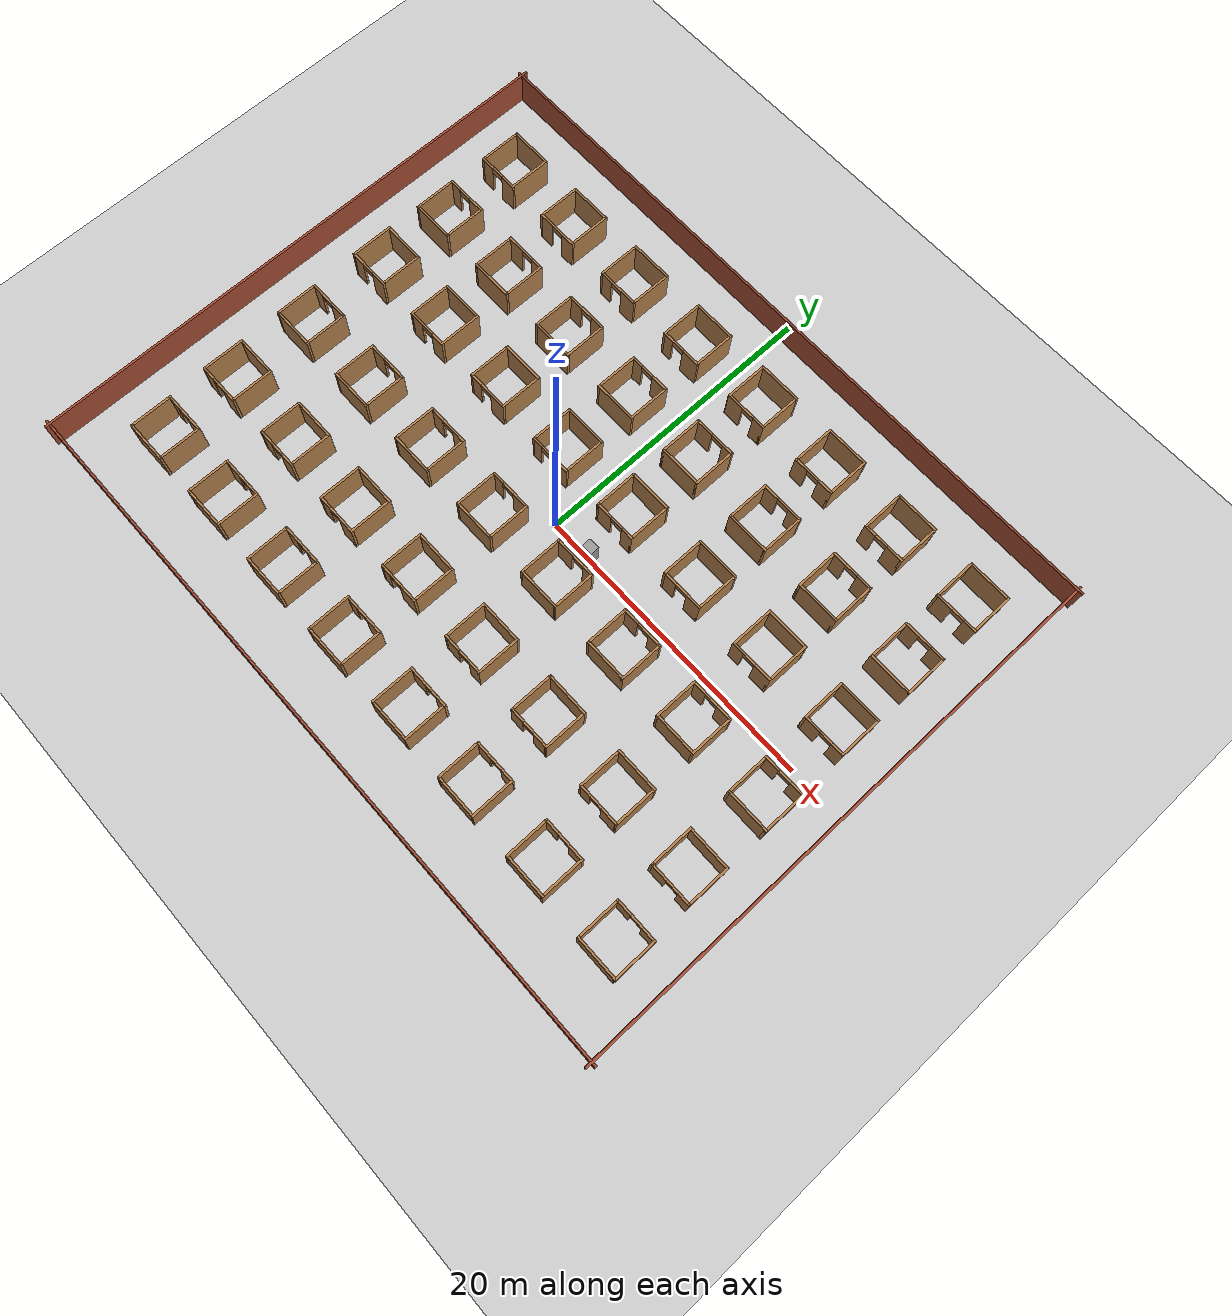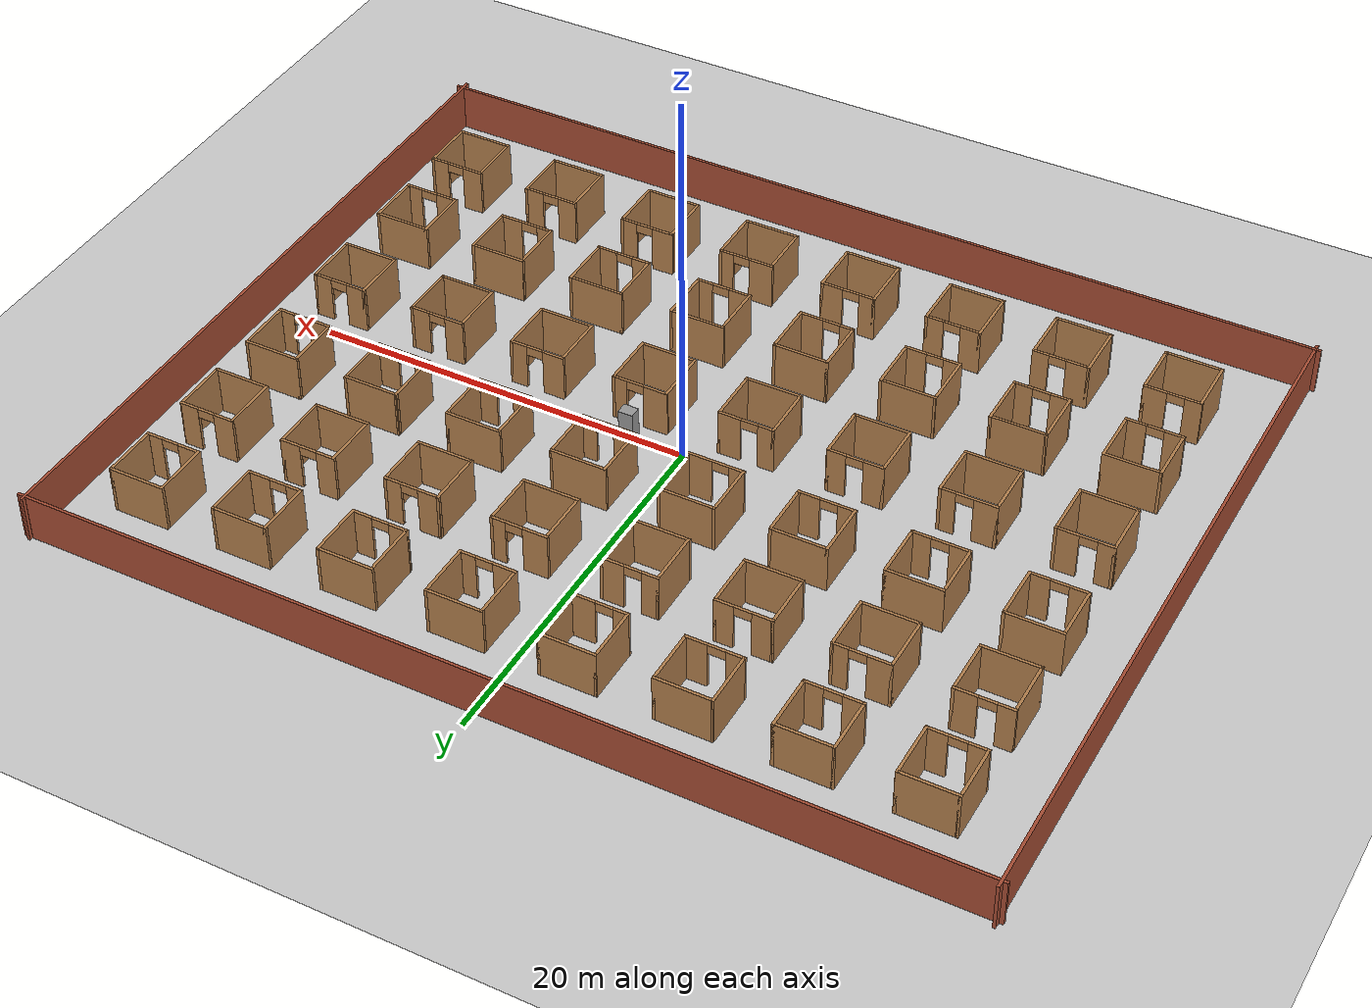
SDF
<sdf version="1.6">
 <world name="default">
  <light name="sun" type="directional">
   <pose>0 0 10 0 -0 0</pose>
   <diffuse>0.8 0.8 0.8 1</diffuse>
   <specular>0.2 0.2 0.2 1</specular>
   <attenuation>
    <range>1000</range>
    <constant>0.9</constant>
    <linear>0.01</linear>
    <quadratic>0.001</quadratic>
   </attenuation>
   <direction>-0.5 0.1 -0.9</direction>
  </light>
  <model name="ground_plane">
   <static>1</static>
   <link name="link">
    <collision name="collision">
     <geometry><plane><normal>0 0 1</normal><size>100 100</size></plane></geometry>
     <surface>
      <contact><collide_bitmask>65535</collide_bitmask></contact>
      <friction><ode><mu>100</mu><mu2>50</mu2></ode></friction>
     </surface>
    </collision>
    <visual name="visual">
     <cast_shadows>0</cast_shadows>
     <geometry><plane><normal>0 0 1</normal><size>100 100</size></plane></geometry>
     <material>
      <script><uri>file://media/materials/scripts/gazebo.material</uri><name>Gazebo/Grey</name></script>
     </material>
    </visual>
   </link>
  </model>
  <gravity>0 0 -9.8</gravity>
  <magnetic_field>6e-06 2.3e-05 -4.2e-05</magnetic_field>
  <atmosphere type="adiabatic"/>
  <physics name="default_physics" default="0" type="ode">
   <max_step_size>0.001</max_step_size>
   <real_time_factor>1</real_time_factor>
   <real_time_update_rate>0</real_time_update_rate>
  </physics>
  <scene><ambient>0.4 0.4 0.4 1</ambient><background>0.7 0.7 0.7 1</background><shadows>1</shadows></scene>
  <spherical_coordinates>
   <surface_model>EARTH_WGS84</surface_model>
   <latitude_deg>0</latitude_deg>
   <longitude_deg>0</longitude_deg>
   <elevation>0</elevation>
   <heading_deg>0</heading_deg>
  </spherical_coordinates>
  <model name="room_row">
   <pose>0.21171 -13.8601 0 0 -0 0</pose>
   <link name="Wall_11">
    <collision name="Wall_11_Collision">
     <geometry><box><size>3 0.15 2.5</size></box></geometry>
     <pose>0 0 1.25 0 -0 0</pose>
    </collision>
    <visual name="Wall_11_Visual">
     <pose>0 0 1.25 0 -0 0</pose>
     <geometry><box><size>3 0.15 2.5</size></box></geometry>
     <material>
      <script><uri>file://media/materials/scripts/gazebo.material</uri><name>Gazebo/Wood</name></script>
      <ambient>1 1 1 1</ambient>
     </material>
     <meta><layer>0</layer></meta>
    </visual>
    <pose>1.425 0 0 0 -0 -1.5708</pose>
   </link>
   <link name="Wall_12">
    <collision name="Wall_12_Collision">
     <geometry><box><size>3 0.15 2.5</size></box></geometry>
     <pose>0 0 1.25 0 -0 0</pose>
    </collision>
    <visual name="Wall_12_Visual">
     <pose>0 0 1.25 0 -0 0</pose>
     <geometry><box><size>3 0.15 2.5</size></box></geometry>
     <material>
      <script><uri>file://media/materials/scripts/gazebo.material</uri><name>Gazebo/Wood</name></script>
      <ambient>1 1 1 1</ambient>
     </material>
     <meta><layer>0</layer></meta>
    </visual>
    <pose>2.85 -1.425 0 0 -0 0</pose>
   </link>
   <link name="Wall_13">
    <collision name="Wall_13_Collision">
     <geometry><box><size>3 0.15 2.5</size></box></geometry>
     <pose>0 0 1.25 0 -0 0</pose>
    </collision>
    <visual name="Wall_13_Visual">
     <pose>0 0 1.25 0 -0 0</pose>
     <geometry><box><size>3 0.15 2.5</size></box></geometry>
     <material>
      <script><uri>file://media/materials/scripts/gazebo.material</uri><name>Gazebo/Wood</name></script>
      <ambient>1 1 1 1</ambient>
     </material>
     <meta><layer>0</layer></meta>
    </visual>
    <pose>4.275 0 0 0 -0 1.5708</pose>
   </link>
   <link name="Wall_14">
    <pose>2.85 1.425 0 0 -0 3.14159</pose>
    <visual name="Wall_14_Visual_0">
     <pose>-1.10207 0 1.25 0 -0 0</pose>
     <geometry><box><size>0.795857 0.15 2.5</size></box></geometry>
     <material>
      <script><uri>file://media/materials/scripts/gazebo.material</uri><name>Gazebo/Wood</name></script>
      <ambient>1 1 1 1</ambient>
     </material>
     <meta><layer>0</layer></meta>
    </visual>
    <collision name="Wall_14_Collision_0">
     <geometry><box><size>0.795857 0.15 2.5</size></box></geometry>
     <pose>-1.10207 0 1.25 0 -0 0</pose>
    </collision>
    <visual name="Wall_14_Visual_1">
     <pose>0.847928 0 1.25 0 -0 0</pose>
     <geometry><box><size>1.30414 0.15 2.5</size></box></geometry>
     <material>
      <script><uri>file://media/materials/scripts/gazebo.material</uri><name>Gazebo/Wood</name></script>
      <ambient>1 1 1 1</ambient>
     </material>
     <meta><layer>0</layer></meta>
    </visual>
    <collision name="Wall_14_Collision_1">
     <geometry><box><size>1.30414 0.15 2.5</size></box></geometry>
     <pose>0.847928 0 1.25 0 -0 0</pose>
    </collision>
    <visual name="Wall_14_Visual_2">
     <pose>-0.254143 0 2.25 0 -0 0</pose>
     <geometry><box><size>0.9 0.15 0.5</size></box></geometry>
     <material>
      <script><uri>file://media/materials/scripts/gazebo.material</uri><name>Gazebo/Wood</name></script>
      <ambient>1 1 1 1</ambient>
     </material>
     <meta><layer>0</layer></meta>
    </visual>
    <collision name="Wall_14_Collision_2">
     <geometry><box><size>0.9 0.15 0.5</size></box></geometry>
     <pose>-0.254143 0 2.25 0 -0 0</pose>
    </collision>
   </link>
   <link name="Wall_17">
    <collision name="Wall_17_Collision">
     <geometry><box><size>3 0.15 2.5</size></box></geometry>
     <pose>0 0 1.25 0 -0 0</pose>
    </collision>
    <visual name="Wall_17_Visual">
     <pose>0 0 1.25 0 -0 0</pose>
     <geometry><box><size>3 0.15 2.5</size></box></geometry>
     <material>
      <script><uri>file://media/materials/scripts/gazebo.material</uri><name>Gazebo/Wood</name></script>
      <ambient>1 1 1 1</ambient>
     </material>
     <meta><layer>0</layer></meta>
    </visual>
    <pose>7.125 0 0 0 -0 -1.5708</pose>
   </link>
   <link name="Wall_18">
    <collision name="Wall_18_Collision">
     <geometry><box><size>3 0.15 2.5</size></box></geometry>
     <pose>0 0 1.25 0 -0 0</pose>
    </collision>
    <visual name="Wall_18_Visual">
     <pose>0 0 1.25 0 -0 0</pose>
     <geometry><box><size>3 0.15 2.5</size></box></geometry>
     <material>
      <script><uri>file://media/materials/scripts/gazebo.material</uri><name>Gazebo/Wood</name></script>
      <ambient>1 1 1 1</ambient>
     </material>
     <meta><layer>0</layer></meta>
    </visual>
    <pose>8.55 -1.425 0 0 -0 0</pose>
   </link>
   <link name="Wall_19">
    <collision name="Wall_19_Collision">
     <geometry><box><size>3 0.15 2.5</size></box></geometry>
     <pose>0 0 1.25 0 -0 0</pose>
    </collision>
    <visual name="Wall_19_Visual">
     <pose>0 0 1.25 0 -0 0</pose>
     <geometry><box><size>3 0.15 2.5</size></box></geometry>
     <material>
      <script><uri>file://media/materials/scripts/gazebo.material</uri><name>Gazebo/Wood</name></script>
      <ambient>1 1 1 1</ambient>
     </material>
     <meta><layer>0</layer></meta>
    </visual>
    <pose>9.975 0 0 0 -0 1.5708</pose>
   </link>
   <link name="Wall_20">
    <pose>8.55 1.425 0 0 -0 3.14159</pose>
    <visual name="Wall_20_Visual_0">
     <pose>-1.03119 0 1.25 0 -0 0</pose>
     <geometry><box><size>0.937612 0.15 2.5</size></box></geometry>
     <material>
      <script><uri>file://media/materials/scripts/gazebo.material</uri><name>Gazebo/Wood</name></script>
      <ambient>1 1 1 1</ambient>
     </material>
     <meta><layer>0</layer></meta>
    </visual>
    <collision name="Wall_20_Collision_0">
     <geometry><box><size>0.937612 0.15 2.5</size></box></geometry>
     <pose>-1.03119 0 1.25 0 -0 0</pose>
    </collision>
    <visual name="Wall_20_Visual_1">
     <pose>0.918806 0 1.25 0 -0 0</pose>
     <geometry><box><size>1.16239 0.15 2.5</size></box></geometry>
     <material>
      <script><uri>file://media/materials/scripts/gazebo.material</uri><name>Gazebo/Wood</name></script>
      <ambient>1 1 1 1</ambient>
     </material>
     <meta><layer>0</layer></meta>
    </visual>
    <collision name="Wall_20_Collision_1">
     <geometry><box><size>1.16239 0.15 2.5</size></box></geometry>
     <pose>0.918806 0 1.25 0 -0 0</pose>
    </collision>
    <visual name="Wall_20_Visual_2">
     <pose>-0.112388 0 2.25 0 -0 0</pose>
     <geometry><box><size>0.9 0.15 0.5</size></box></geometry>
     <material>
      <script><uri>file://media/materials/scripts/gazebo.material</uri><name>Gazebo/Wood</name></script>
      <ambient>1 1 1 1</ambient>
     </material>
     <meta><layer>0</layer></meta>
    </visual>
    <collision name="Wall_20_Collision_2">
     <geometry><box><size>0.9 0.15 0.5</size></box></geometry>
     <pose>-0.112388 0 2.25 0 -0 0</pose>
    </collision>
   </link>
   <link name="Wall_23">
    <collision name="Wall_23_Collision">
     <geometry><box><size>3 0.15 2.5</size></box></geometry>
     <pose>0 0 1.25 0 -0 0</pose>
    </collision>
    <visual name="Wall_23_Visual">
     <pose>0 0 1.25 0 -0 0</pose>
     <geometry><box><size>3 0.15 2.5</size></box></geometry>
     <material>
      <script><uri>file://media/materials/scripts/gazebo.material</uri><name>Gazebo/Wood</name></script>
      <ambient>1 1 1 1</ambient>
     </material>
     <meta><layer>0</layer></meta>
    </visual>
    <pose>-7.125 0 0 0 -0 -1.5708</pose>
   </link>
   <link name="Wall_24">
    <collision name="Wall_24_Collision">
     <geometry><box><size>3 0.15 2.5</size></box></geometry>
     <pose>0 0 1.25 0 -0 0</pose>
    </collision>
    <visual name="Wall_24_Visual">
     <pose>0 0 1.25 0 -0 0</pose>
     <geometry><box><size>3 0.15 2.5</size></box></geometry>
     <material>
      <script><uri>file://media/materials/scripts/gazebo.material</uri><name>Gazebo/Wood</name></script>
      <ambient>1 1 1 1</ambient>
     </material>
     <meta><layer>0</layer></meta>
    </visual>
    <pose>-8.55 -1.425 0 0 -0 3.14159</pose>
   </link>
   <link name="Wall_25">
    <collision name="Wall_25_Collision">
     <geometry><box><size>3 0.15 2.5</size></box></geometry>
     <pose>0 0 1.25 0 -0 0</pose>
    </collision>
    <visual name="Wall_25_Visual">
     <pose>0 0 1.25 0 -0 0</pose>
     <geometry><box><size>3 0.15 2.5</size></box></geometry>
     <material>
      <script><uri>file://media/materials/scripts/gazebo.material</uri><name>Gazebo/Wood</name></script>
      <ambient>1 1 1 1</ambient>
     </material>
     <meta><layer>0</layer></meta>
    </visual>
    <pose>-9.975 0 0 0 -0 1.5708</pose>
   </link>
   <link name="Wall_26">
    <pose>-8.55 1.425 0 0 -0 0</pose>
    <visual name="Wall_26_Visual_0">
     <pose>-0.952424 0 1.25 0 -0 0</pose>
     <geometry><box><size>1.09515 0.15 2.5</size></box></geometry>
     <material>
      <script><uri>file://media/materials/scripts/gazebo.material</uri><name>Gazebo/Wood</name></script>
      <ambient>1 1 1 1</ambient>
     </material>
     <meta><layer>0</layer></meta>
    </visual>
    <collision name="Wall_26_Collision_0">
     <geometry><box><size>1.09515 0.15 2.5</size></box></geometry>
     <pose>-0.952424 0 1.25 0 -0 0</pose>
    </collision>
    <visual name="Wall_26_Visual_1">
     <pose>0.997576 0 1.25 0 -0 0</pose>
     <geometry><box><size>1.00485 0.15 2.5</size></box></geometry>
     <material>
      <script><uri>file://media/materials/scripts/gazebo.material</uri><name>Gazebo/Wood</name></script>
      <ambient>1 1 1 1</ambient>
     </material>
     <meta><layer>0</layer></meta>
    </visual>
    <collision name="Wall_26_Collision_1">
     <geometry><box><size>1.00485 0.15 2.5</size></box></geometry>
     <pose>0.997576 0 1.25 0 -0 0</pose>
    </collision>
    <visual name="Wall_26_Visual_2">
     <pose>0.045152 0 2.25 0 -0 0</pose>
     <geometry><box><size>0.9 0.15 0.5</size></box></geometry>
     <material>
      <script><uri>file://media/materials/scripts/gazebo.material</uri><name>Gazebo/Wood</name></script>
      <ambient>1 1 1 1</ambient>
     </material>
     <meta><layer>0</layer></meta>
    </visual>
    <collision name="Wall_26_Collision_2">
     <geometry><box><size>0.9 0.15 0.5</size></box></geometry>
     <pose>0.045152 0 2.25 0 -0 0</pose>
    </collision>
   </link>
   <link name="Wall_29">
    <collision name="Wall_29_Collision">
     <geometry><box><size>3 0.15 2.5</size></box></geometry>
     <pose>0 0 1.25 0 -0 0</pose>
    </collision>
    <visual name="Wall_29_Visual">
     <pose>0 0 1.25 0 -0 0</pose>
     <geometry><box><size>3 0.15 2.5</size></box></geometry>
     <material>
      <script><uri>file://media/materials/scripts/gazebo.material</uri><name>Gazebo/Wood</name></script>
      <ambient>1 1 1 1</ambient>
     </material>
     <meta><layer>0</layer></meta>
    </visual>
    <pose>-12.825 0 0 0 -0 -1.5708</pose>
   </link>
   <link name="Wall_30">
    <collision name="Wall_30_Collision">
     <geometry><box><size>3 0.15 2.5</size></box></geometry>
     <pose>0 0 1.25 0 -0 0</pose>
    </collision>
    <visual name="Wall_30_Visual">
     <pose>0 0 1.25 0 -0 0</pose>
     <geometry><box><size>3 0.15 2.5</size></box></geometry>
     <material>
      <script><uri>file://media/materials/scripts/gazebo.material</uri><name>Gazebo/Wood</name></script>
      <ambient>1 1 1 1</ambient>
     </material>
     <meta><layer>0</layer></meta>
    </visual>
    <pose>-14.25 -1.425 0 0 -0 3.14159</pose>
   </link>
   <link name="Wall_31">
    <collision name="Wall_31_Collision">
     <geometry><box><size>3 0.15 2.5</size></box></geometry>
     <pose>0 0 1.25 0 -0 0</pose>
    </collision>
    <visual name="Wall_31_Visual">
     <pose>0 0 1.25 0 -0 0</pose>
     <geometry><box><size>3 0.15 2.5</size></box></geometry>
     <material>
      <script><uri>file://media/materials/scripts/gazebo.material</uri><name>Gazebo/Wood</name></script>
      <ambient>1 1 1 1</ambient>
     </material>
     <meta><layer>0</layer></meta>
    </visual>
    <pose>-15.675 0 0 0 -0 1.5708</pose>
   </link>
   <link name="Wall_32">
    <pose>-14.25 1.425 0 0 -0 0</pose>
    <visual name="Wall_32_Visual_0">
     <pose>-0.881547 0 1.25 0 -0 0</pose>
     <geometry><box><size>1.23691 0.15 2.5</size></box></geometry>
     <material>
      <script><uri>file://media/materials/scripts/gazebo.material</uri><name>Gazebo/Wood</name></script>
      <ambient>1 1 1 1</ambient>
     </material>
     <meta><layer>0</layer></meta>
    </visual>
    <collision name="Wall_32_Collision_0">
     <geometry><box><size>1.23691 0.15 2.5</size></box></geometry>
     <pose>-0.881547 0 1.25 0 -0 0</pose>
    </collision>
    <visual name="Wall_32_Visual_1">
     <pose>1.06845 0 1.25 0 -0 0</pose>
     <geometry><box><size>0.863093 0.15 2.5</size></box></geometry>
     <material>
      <script><uri>file://media/materials/scripts/gazebo.material</uri><name>Gazebo/Wood</name></script>
      <ambient>1 1 1 1</ambient>
     </material>
     <meta><layer>0</layer></meta>
    </visual>
    <collision name="Wall_32_Collision_1">
     <geometry><box><size>0.863093 0.15 2.5</size></box></geometry>
     <pose>1.06845 0 1.25 0 -0 0</pose>
    </collision>
    <visual name="Wall_32_Visual_2">
     <pose>0.186907 0 2.25 0 -0 0</pose>
     <geometry><box><size>0.9 0.15 0.5</size></box></geometry>
     <material>
      <script><uri>file://media/materials/scripts/gazebo.material</uri><name>Gazebo/Wood</name></script>
      <ambient>1 1 1 1</ambient>
     </material>
     <meta><layer>0</layer></meta>
    </visual>
    <collision name="Wall_32_Collision_2">
     <geometry><box><size>0.9 0.15 0.5</size></box></geometry>
     <pose>0.186907 0 2.25 0 -0 0</pose>
    </collision>
   </link>
   <link name="Wall_35">
    <collision name="Wall_35_Collision">
     <geometry><box><size>3 0.15 2.5</size></box></geometry>
     <pose>0 0 1.25 0 -0 0</pose>
    </collision>
    <visual name="Wall_35_Visual">
     <pose>0 0 1.25 0 -0 0</pose>
     <geometry><box><size>3 0.15 2.5</size></box></geometry>
     <material>
      <script><uri>file://media/materials/scripts/gazebo.material</uri><name>Gazebo/Wood</name></script>
      <ambient>1 1 1 1</ambient>
     </material>
     <meta><layer>0</layer></meta>
    </visual>
    <pose>12.825 0 0 0 -0 -1.5708</pose>
   </link>
   <link name="Wall_36">
    <collision name="Wall_36_Collision">
     <geometry><box><size>3 0.15 2.5</size></box></geometry>
     <pose>0 0 1.25 0 -0 0</pose>
    </collision>
    <visual name="Wall_36_Visual">
     <pose>0 0 1.25 0 -0 0</pose>
     <geometry><box><size>3 0.15 2.5</size></box></geometry>
     <material>
      <script><uri>file://media/materials/scripts/gazebo.material</uri><name>Gazebo/Wood</name></script>
      <ambient>1 1 1 1</ambient>
     </material>
     <meta><layer>0</layer></meta>
    </visual>
    <pose>14.25 -1.425 0 0 -0 0</pose>
   </link>
   <link name="Wall_37">
    <collision name="Wall_37_Collision">
     <geometry><box><size>3 0.15 2.5</size></box></geometry>
     <pose>0 0 1.25 0 -0 0</pose>
    </collision>
    <visual name="Wall_37_Visual">
     <pose>0 0 1.25 0 -0 0</pose>
     <geometry><box><size>3 0.15 2.5</size></box></geometry>
     <material>
      <script><uri>file://media/materials/scripts/gazebo.material</uri><name>Gazebo/Wood</name></script>
      <ambient>1 1 1 1</ambient>
     </material>
     <meta><layer>0</layer></meta>
    </visual>
    <pose>15.675 0 0 0 -0 1.5708</pose>
   </link>
   <link name="Wall_38">
    <pose>14.25 1.425 0 0 -0 3.14159</pose>
    <visual name="Wall_38_Visual_0">
     <pose>-0.960316 0 1.25 0 -0 0</pose>
     <geometry><box><size>1.07937 0.15 2.5</size></box></geometry>
     <material>
      <script><uri>file://media/materials/scripts/gazebo.material</uri><name>Gazebo/Wood</name></script>
      <ambient>1 1 1 1</ambient>
     </material>
     <meta><layer>0</layer></meta>
    </visual>
    <collision name="Wall_38_Collision_0">
     <geometry><box><size>1.07937 0.15 2.5</size></box></geometry>
     <pose>-0.960316 0 1.25 0 -0 0</pose>
    </collision>
    <visual name="Wall_38_Visual_1">
     <pose>0.989684 0 1.25 0 -0 0</pose>
     <geometry><box><size>1.02063 0.15 2.5</size></box></geometry>
     <material>
      <script><uri>file://media/materials/scripts/gazebo.material</uri><name>Gazebo/Wood</name></script>
      <ambient>1 1 1 1</ambient>
     </material>
     <meta><layer>0</layer></meta>
    </visual>
    <collision name="Wall_38_Collision_1">
     <geometry><box><size>1.02063 0.15 2.5</size></box></geometry>
     <pose>0.989684 0 1.25 0 -0 0</pose>
    </collision>
    <visual name="Wall_38_Visual_2">
     <pose>0.029367 0 2.25 0 -0 0</pose>
     <geometry><box><size>0.9 0.15 0.5</size></box></geometry>
     <material>
      <script><uri>file://media/materials/scripts/gazebo.material</uri><name>Gazebo/Wood</name></script>
      <ambient>1 1 1 1</ambient>
     </material>
     <meta><layer>0</layer></meta>
    </visual>
    <collision name="Wall_38_Collision_2">
     <geometry><box><size>0.9 0.15 0.5</size></box></geometry>
     <pose>0.029367 0 2.25 0 -0 0</pose>
    </collision>
   </link>
   <link name="Wall_41">
    <collision name="Wall_41_Collision">
     <geometry><box><size>3 0.15 2.5</size></box></geometry>
     <pose>0 0 1.25 0 -0 0</pose>
    </collision>
    <visual name="Wall_41_Visual">
     <pose>0 0 1.25 0 -0 0</pose>
     <geometry><box><size>3 0.15 2.5</size></box></geometry>
     <material>
      <script><uri>file://media/materials/scripts/gazebo.material</uri><name>Gazebo/Wood</name></script>
      <ambient>1 1 1 1</ambient>
     </material>
     <meta><layer>0</layer></meta>
    </visual>
    <pose>-18.525 0 0 0 -0 -1.5708</pose>
   </link>
   <link name="Wall_42">
    <collision name="Wall_42_Collision">
     <geometry><box><size>3 0.15 2.5</size></box></geometry>
     <pose>0 0 1.25 0 -0 0</pose>
    </collision>
    <visual name="Wall_42_Visual">
     <pose>0 0 1.25 0 -0 0</pose>
     <geometry><box><size>3 0.15 2.5</size></box></geometry>
     <material>
      <script><uri>file://media/materials/scripts/gazebo.material</uri><name>Gazebo/Wood</name></script>
      <ambient>1 1 1 1</ambient>
     </material>
     <meta><layer>0</layer></meta>
    </visual>
    <pose>-19.95 -1.425 0 0 -0 3.14159</pose>
   </link>
   <link name="Wall_45">
    <pose>-19.95 1.425 0 0 -0 3.14159</pose>
    <visual name="Wall_45_Visual_0">
     <pose>-0.89308 0 1.25 0 -0 0</pose>
     <geometry><box><size>1.21384 0.15 2.5</size></box></geometry>
     <material>
      <script><uri>file://media/materials/scripts/gazebo.material</uri><name>Gazebo/Wood</name></script>
      <ambient>1 1 1 1</ambient>
     </material>
     <meta><layer>0</layer></meta>
    </visual>
    <collision name="Wall_45_Collision_0">
     <geometry><box><size>1.21384 0.15 2.5</size></box></geometry>
     <pose>-0.89308 0 1.25 0 -0 0</pose>
    </collision>
    <visual name="Wall_45_Visual_1">
     <pose>1.05692 0 1.25 0 -0 0</pose>
     <geometry><box><size>0.886161 0.15 2.5</size></box></geometry>
     <material>
      <script><uri>file://media/materials/scripts/gazebo.material</uri><name>Gazebo/Wood</name></script>
      <ambient>1 1 1 1</ambient>
     </material>
     <meta><layer>0</layer></meta>
    </visual>
    <collision name="Wall_45_Collision_1">
     <geometry><box><size>0.886161 0.15 2.5</size></box></geometry>
     <pose>1.05692 0 1.25 0 -0 0</pose>
    </collision>
    <visual name="Wall_45_Visual_2">
     <pose>0.163839 0 2.25 0 -0 0</pose>
     <geometry><box><size>0.9 0.15 0.5</size></box></geometry>
     <material>
      <script><uri>file://media/materials/scripts/gazebo.material</uri><name>Gazebo/Wood</name></script>
      <ambient>1 1 1 1</ambient>
     </material>
     <meta><layer>0</layer></meta>
    </visual>
    <collision name="Wall_45_Collision_2">
     <geometry><box><size>0.9 0.15 0.5</size></box></geometry>
     <pose>0.163839 0 2.25 0 -0 0</pose>
    </collision>
   </link>
   <link name="Wall_46">
    <collision name="Wall_46_Collision">
     <geometry><box><size>3 0.15 2.5</size></box></geometry>
     <pose>0 0 1.25 0 -0 0</pose>
    </collision>
    <visual name="Wall_46_Visual">
     <pose>0 0 1.25 0 -0 0</pose>
     <geometry><box><size>3 0.15 2.5</size></box></geometry>
     <material>
      <script><uri>file://media/materials/scripts/gazebo.material</uri><name>Gazebo/Wood</name></script>
      <ambient>1 1 1 1</ambient>
     </material>
     <meta><layer>0</layer></meta>
    </visual>
    <pose>-21.375 0 0 0 -0 -1.5708</pose>
   </link>
   <link name="Wall_49">
    <collision name="Wall_49_Collision">
     <geometry><box><size>3 0.15 2.5</size></box></geometry>
     <pose>0 0 1.25 0 -0 0</pose>
    </collision>
    <visual name="Wall_49_Visual">
     <pose>0 0 1.25 0 -0 0</pose>
     <geometry><box><size>3 0.15 2.5</size></box></geometry>
     <material>
      <script><uri>file://media/materials/scripts/gazebo.material</uri><name>Gazebo/Wood</name></script>
      <ambient>1 1 1 1</ambient>
     </material>
     <meta><layer>0</layer></meta>
    </visual>
    <pose>18.525 0 0 0 -0 -1.5708</pose>
   </link>
   <link name="Wall_5">
    <pose>-2.85 1.425 0 0 -0 0</pose>
    <visual name="Wall_5_Visual_0">
     <pose>-1.05848 0 1.25 0 -0 0</pose>
     <geometry><box><size>0.883039 0.15 2.5</size></box></geometry>
     <material>
      <script><uri>file://media/materials/scripts/gazebo.material</uri><name>Gazebo/Wood</name></script>
      <ambient>1 1 1 1</ambient>
     </material>
     <meta><layer>0</layer></meta>
    </visual>
    <collision name="Wall_5_Collision_0">
     <geometry><box><size>0.883039 0.15 2.5</size></box></geometry>
     <pose>-1.05848 0 1.25 0 -0 0</pose>
    </collision>
    <visual name="Wall_5_Visual_1">
     <pose>0.891519 0 1.25 0 -0 0</pose>
     <geometry><box><size>1.21696 0.15 2.5</size></box></geometry>
     <material>
      <script><uri>file://media/materials/scripts/gazebo.material</uri><name>Gazebo/Wood</name></script>
      <ambient>1 1 1 1</ambient>
     </material>
     <meta><layer>0</layer></meta>
    </visual>
    <collision name="Wall_5_Collision_1">
     <geometry><box><size>1.21696 0.15 2.5</size></box></geometry>
     <pose>0.891519 0 1.25 0 -0 0</pose>
    </collision>
    <visual name="Wall_5_Visual_2">
     <pose>-0.166961 0 2.25 0 -0 0</pose>
     <geometry><box><size>0.9 0.15 0.5</size></box></geometry>
     <material>
      <script><uri>file://media/materials/scripts/gazebo.material</uri><name>Gazebo/Wood</name></script>
      <ambient>1 1 1 1</ambient>
     </material>
     <meta><layer>0</layer></meta>
    </visual>
    <collision name="Wall_5_Collision_2">
     <geometry><box><size>0.9 0.15 0.5</size></box></geometry>
     <pose>-0.166961 0 2.25 0 -0 0</pose>
    </collision>
   </link>
   <link name="Wall_51">
    <collision name="Wall_51_Collision">
     <geometry><box><size>3 0.15 2.5</size></box></geometry>
     <pose>0 0 1.25 0 -0 0</pose>
    </collision>
    <visual name="Wall_51_Visual">
     <pose>0 0 1.25 0 -0 0</pose>
     <geometry><box><size>3 0.15 2.5</size></box></geometry>
     <material>
      <script><uri>file://media/materials/scripts/gazebo.material</uri><name>Gazebo/Wood</name></script>
      <ambient>1 1 1 1</ambient>
     </material>
     <meta><layer>0</layer></meta>
    </visual>
    <pose>19.95 -1.425 0 0 -0 0</pose>
   </link>
   <link name="Wall_53">
    <collision name="Wall_53_Collision">
     <geometry><box><size>3 0.15 2.5</size></box></geometry>
     <pose>0 0 1.25 0 -0 0</pose>
    </collision>
    <visual name="Wall_53_Visual">
     <pose>0 0 1.25 0 -0 0</pose>
     <geometry><box><size>3 0.15 2.5</size></box></geometry>
     <material>
      <script><uri>file://media/materials/scripts/gazebo.material</uri><name>Gazebo/Wood</name></script>
      <ambient>1 1 1 1</ambient>
     </material>
     <meta><layer>0</layer></meta>
    </visual>
    <pose>21.375 0 0 0 -0 1.5708</pose>
   </link>
   <link name="Wall_54">
    <pose>19.95 1.425 0 0 -0 3.14159</pose>
    <visual name="Wall_54_Visual_0">
     <pose>-0.994975 0 1.25 0 -0 0</pose>
     <geometry><box><size>1.01005 0.15 2.5</size></box></geometry>
     <material>
      <script><uri>file://media/materials/scripts/gazebo.material</uri><name>Gazebo/Wood</name></script>
      <ambient>1 1 1 1</ambient>
     </material>
     <meta><layer>0</layer></meta>
    </visual>
    <collision name="Wall_54_Collision_0">
     <geometry><box><size>1.01005 0.15 2.5</size></box></geometry>
     <pose>-0.994975 0 1.25 0 -0 0</pose>
    </collision>
    <visual name="Wall_54_Visual_1">
     <pose>0.955025 0 1.25 0 -0 0</pose>
     <geometry><box><size>1.08995 0.15 2.5</size></box></geometry>
     <material>
      <script><uri>file://media/materials/scripts/gazebo.material</uri><name>Gazebo/Wood</name></script>
      <ambient>1 1 1 1</ambient>
     </material>
     <meta><layer>0</layer></meta>
    </visual>
    <collision name="Wall_54_Collision_1">
     <geometry><box><size>1.08995 0.15 2.5</size></box></geometry>
     <pose>0.955025 0 1.25 0 -0 0</pose>
    </collision>
    <visual name="Wall_54_Visual_2">
     <pose>-0.039949 0 2.25 0 -0 0</pose>
     <geometry><box><size>0.9 0.15 0.5</size></box></geometry>
     <material>
      <script><uri>file://media/materials/scripts/gazebo.material</uri><name>Gazebo/Wood</name></script>
      <ambient>1 1 1 1</ambient>
     </material>
     <meta><layer>0</layer></meta>
    </visual>
    <collision name="Wall_54_Collision_2">
     <geometry><box><size>0.9 0.15 0.5</size></box></geometry>
     <pose>-0.039949 0 2.25 0 -0 0</pose>
    </collision>
   </link>
   <link name="Wall_6">
    <collision name="Wall_6_Collision">
     <geometry><box><size>3 0.15 2.5</size></box></geometry>
     <pose>0 0 1.25 0 -0 0</pose>
    </collision>
    <visual name="Wall_6_Visual">
     <pose>0 0 1.25 0 -0 0</pose>
     <geometry><box><size>3 0.15 2.5</size></box></geometry>
     <material>
      <script><uri>file://media/materials/scripts/gazebo.material</uri><name>Gazebo/Wood</name></script>
      <ambient>1 1 1 1</ambient>
     </material>
     <meta><layer>0</layer></meta>
    </visual>
    <pose>-1.425 0 0 0 -0 -1.5708</pose>
   </link>
   <link name="Wall_7">
    <collision name="Wall_7_Collision">
     <geometry><box><size>3 0.15 2.5</size></box></geometry>
     <pose>0 0 1.25 0 -0 0</pose>
    </collision>
    <visual name="Wall_7_Visual">
     <pose>0 0 1.25 0 -0 0</pose>
     <geometry><box><size>3 0.15 2.5</size></box></geometry>
     <material>
      <script><uri>file://media/materials/scripts/gazebo.material</uri><name>Gazebo/Wood</name></script>
      <ambient>1 1 1 1</ambient>
     </material>
     <meta><layer>0</layer></meta>
    </visual>
    <pose>-2.85 -1.425 0 0 -0 3.14159</pose>
   </link>
   <link name="Wall_8">
    <collision name="Wall_8_Collision">
     <geometry><box><size>3 0.15 2.5</size></box></geometry>
     <pose>0 0 1.25 0 -0 0</pose>
    </collision>
    <visual name="Wall_8_Visual">
     <pose>0 0 1.25 0 -0 0</pose>
     <geometry><box><size>3 0.15 2.5</size></box></geometry>
     <material>
      <script><uri>file://media/materials/scripts/gazebo.material</uri><name>Gazebo/Wood</name></script>
      <ambient>1 1 1 1</ambient>
     </material>
     <meta><layer>0</layer></meta>
    </visual>
    <pose>-4.275 0 0 0 -0 1.5708</pose>
   </link>
   <static>1</static>
  </model>
  <model name="room_row_clone">
   <pose>0.075148 -8.32728 0 0 -0 3.14</pose>
   <link name="Wall_11">
    <collision name="Wall_11_Collision">
     <geometry><box><size>3 0.15 2.5</size></box></geometry>
     <pose>0 0 1.25 0 -0 0</pose>
    </collision>
    <visual name="Wall_11_Visual">
     <pose>0 0 1.25 0 -0 0</pose>
     <geometry><box><size>3 0.15 2.5</size></box></geometry>
     <material>
      <script><uri>file://media/materials/scripts/gazebo.material</uri><name>Gazebo/Wood</name></script>
      <ambient>1 1 1 1</ambient>
     </material>
     <meta><layer>0</layer></meta>
    </visual>
    <pose>1.425 0 0 0 -0 -1.5708</pose>
   </link>
   <link name="Wall_12">
    <collision name="Wall_12_Collision">
     <geometry><box><size>3 0.15 2.5</size></box></geometry>
     <pose>0 0 1.25 0 -0 0</pose>
    </collision>
    <visual name="Wall_12_Visual">
     <pose>0 0 1.25 0 -0 0</pose>
     <geometry><box><size>3 0.15 2.5</size></box></geometry>
     <material>
      <script><uri>file://media/materials/scripts/gazebo.material</uri><name>Gazebo/Wood</name></script>
      <ambient>1 1 1 1</ambient>
     </material>
     <meta><layer>0</layer></meta>
    </visual>
    <pose>2.85 -1.425 0 0 -0 0</pose>
   </link>
   <link name="Wall_13">
    <collision name="Wall_13_Collision">
     <geometry><box><size>3 0.15 2.5</size></box></geometry>
     <pose>0 0 1.25 0 -0 0</pose>
    </collision>
    <visual name="Wall_13_Visual">
     <pose>0 0 1.25 0 -0 0</pose>
     <geometry><box><size>3 0.15 2.5</size></box></geometry>
     <material>
      <script><uri>file://media/materials/scripts/gazebo.material</uri><name>Gazebo/Wood</name></script>
      <ambient>1 1 1 1</ambient>
     </material>
     <meta><layer>0</layer></meta>
    </visual>
    <pose>4.275 0 0 0 -0 1.5708</pose>
   </link>
   <link name="Wall_14">
    <pose>2.85 1.425 0 0 -0 3.14159</pose>
    <visual name="Wall_14_Visual_0">
     <pose>-1.10207 0 1.25 0 -0 0</pose>
     <geometry><box><size>0.795857 0.15 2.5</size></box></geometry>
     <material>
      <script><uri>file://media/materials/scripts/gazebo.material</uri><name>Gazebo/Wood</name></script>
      <ambient>1 1 1 1</ambient>
     </material>
     <meta><layer>0</layer></meta>
    </visual>
    <collision name="Wall_14_Collision_0">
     <geometry><box><size>0.795857 0.15 2.5</size></box></geometry>
     <pose>-1.10207 0 1.25 0 -0 0</pose>
    </collision>
    <visual name="Wall_14_Visual_1">
     <pose>0.847928 0 1.25 0 -0 0</pose>
     <geometry><box><size>1.30414 0.15 2.5</size></box></geometry>
     <material>
      <script><uri>file://media/materials/scripts/gazebo.material</uri><name>Gazebo/Wood</name></script>
      <ambient>1 1 1 1</ambient>
     </material>
     <meta><layer>0</layer></meta>
    </visual>
    <collision name="Wall_14_Collision_1">
     <geometry><box><size>1.30414 0.15 2.5</size></box></geometry>
     <pose>0.847928 0 1.25 0 -0 0</pose>
    </collision>
    <visual name="Wall_14_Visual_2">
     <pose>-0.254143 0 2.25 0 -0 0</pose>
     <geometry><box><size>0.9 0.15 0.5</size></box></geometry>
     <material>
      <script><uri>file://media/materials/scripts/gazebo.material</uri><name>Gazebo/Wood</name></script>
      <ambient>1 1 1 1</ambient>
     </material>
     <meta><layer>0</layer></meta>
    </visual>
    <collision name="Wall_14_Collision_2">
     <geometry><box><size>0.9 0.15 0.5</size></box></geometry>
     <pose>-0.254143 0 2.25 0 -0 0</pose>
    </collision>
   </link>
   <link name="Wall_17">
    <collision name="Wall_17_Collision">
     <geometry><box><size>3 0.15 2.5</size></box></geometry>
     <pose>0 0 1.25 0 -0 0</pose>
    </collision>
    <visual name="Wall_17_Visual">
     <pose>0 0 1.25 0 -0 0</pose>
     <geometry><box><size>3 0.15 2.5</size></box></geometry>
     <material>
      <script><uri>file://media/materials/scripts/gazebo.material</uri><name>Gazebo/Wood</name></script>
      <ambient>1 1 1 1</ambient>
     </material>
     <meta><layer>0</layer></meta>
    </visual>
    <pose>7.125 0 0 0 -0 -1.5708</pose>
   </link>
   <link name="Wall_18">
    <collision name="Wall_18_Collision">
     <geometry><box><size>3 0.15 2.5</size></box></geometry>
     <pose>0 0 1.25 0 -0 0</pose>
    </collision>
    <visual name="Wall_18_Visual">
     <pose>0 0 1.25 0 -0 0</pose>
     <geometry><box><size>3 0.15 2.5</size></box></geometry>
     <material>
      <script><uri>file://media/materials/scripts/gazebo.material</uri><name>Gazebo/Wood</name></script>
      <ambient>1 1 1 1</ambient>
     </material>
     <meta><layer>0</layer></meta>
    </visual>
    <pose>8.55 -1.425 0 0 -0 0</pose>
   </link>
   <link name="Wall_19">
    <collision name="Wall_19_Collision">
     <geometry><box><size>3 0.15 2.5</size></box></geometry>
     <pose>0 0 1.25 0 -0 0</pose>
    </collision>
    <visual name="Wall_19_Visual">
     <pose>0 0 1.25 0 -0 0</pose>
     <geometry><box><size>3 0.15 2.5</size></box></geometry>
     <material>
      <script><uri>file://media/materials/scripts/gazebo.material</uri><name>Gazebo/Wood</name></script>
      <ambient>1 1 1 1</ambient>
     </material>
     <meta><layer>0</layer></meta>
    </visual>
    <pose>9.975 0 0 0 -0 1.5708</pose>
   </link>
   <link name="Wall_20">
    <pose>8.55 1.425 0 0 -0 3.14159</pose>
    <visual name="Wall_20_Visual_0">
     <pose>-1.03119 0 1.25 0 -0 0</pose>
     <geometry><box><size>0.937612 0.15 2.5</size></box></geometry>
     <material>
      <script><uri>file://media/materials/scripts/gazebo.material</uri><name>Gazebo/Wood</name></script>
      <ambient>1 1 1 1</ambient>
     </material>
     <meta><layer>0</layer></meta>
    </visual>
    <collision name="Wall_20_Collision_0">
     <geometry><box><size>0.937612 0.15 2.5</size></box></geometry>
     <pose>-1.03119 0 1.25 0 -0 0</pose>
    </collision>
    <visual name="Wall_20_Visual_1">
     <pose>0.918806 0 1.25 0 -0 0</pose>
     <geometry><box><size>1.16239 0.15 2.5</size></box></geometry>
     <material>
      <script><uri>file://media/materials/scripts/gazebo.material</uri><name>Gazebo/Wood</name></script>
      <ambient>1 1 1 1</ambient>
     </material>
     <meta><layer>0</layer></meta>
    </visual>
    <collision name="Wall_20_Collision_1">
     <geometry><box><size>1.16239 0.15 2.5</size></box></geometry>
     <pose>0.918806 0 1.25 0 -0 0</pose>
    </collision>
    <visual name="Wall_20_Visual_2">
     <pose>-0.112388 0 2.25 0 -0 0</pose>
     <geometry><box><size>0.9 0.15 0.5</size></box></geometry>
     <material>
      <script><uri>file://media/materials/scripts/gazebo.material</uri><name>Gazebo/Wood</name></script>
      <ambient>1 1 1 1</ambient>
     </material>
     <meta><layer>0</layer></meta>
    </visual>
    <collision name="Wall_20_Collision_2">
     <geometry><box><size>0.9 0.15 0.5</size></box></geometry>
     <pose>-0.112388 0 2.25 0 -0 0</pose>
    </collision>
   </link>
   <link name="Wall_23">
    <collision name="Wall_23_Collision">
     <geometry><box><size>3 0.15 2.5</size></box></geometry>
     <pose>0 0 1.25 0 -0 0</pose>
    </collision>
    <visual name="Wall_23_Visual">
     <pose>0 0 1.25 0 -0 0</pose>
     <geometry><box><size>3 0.15 2.5</size></box></geometry>
     <material>
      <script><uri>file://media/materials/scripts/gazebo.material</uri><name>Gazebo/Wood</name></script>
      <ambient>1 1 1 1</ambient>
     </material>
     <meta><layer>0</layer></meta>
    </visual>
    <pose>-7.125 0 0 0 -0 -1.5708</pose>
   </link>
   <link name="Wall_24">
    <collision name="Wall_24_Collision">
     <geometry><box><size>3 0.15 2.5</size></box></geometry>
     <pose>0 0 1.25 0 -0 0</pose>
    </collision>
    <visual name="Wall_24_Visual">
     <pose>0 0 1.25 0 -0 0</pose>
     <geometry><box><size>3 0.15 2.5</size></box></geometry>
     <material>
      <script><uri>file://media/materials/scripts/gazebo.material</uri><name>Gazebo/Wood</name></script>
      <ambient>1 1 1 1</ambient>
     </material>
     <meta><layer>0</layer></meta>
    </visual>
    <pose>-8.55 -1.425 0 0 -0 3.14159</pose>
   </link>
   <link name="Wall_25">
    <collision name="Wall_25_Collision">
     <geometry><box><size>3 0.15 2.5</size></box></geometry>
     <pose>0 0 1.25 0 -0 0</pose>
    </collision>
    <visual name="Wall_25_Visual">
     <pose>0 0 1.25 0 -0 0</pose>
     <geometry><box><size>3 0.15 2.5</size></box></geometry>
     <material>
      <script><uri>file://media/materials/scripts/gazebo.material</uri><name>Gazebo/Wood</name></script>
      <ambient>1 1 1 1</ambient>
     </material>
     <meta><layer>0</layer></meta>
    </visual>
    <pose>-9.975 0 0 0 -0 1.5708</pose>
   </link>
   <link name="Wall_26">
    <pose>-8.55 1.425 0 0 -0 0</pose>
    <visual name="Wall_26_Visual_0">
     <pose>-0.952424 0 1.25 0 -0 0</pose>
     <geometry><box><size>1.09515 0.15 2.5</size></box></geometry>
     <material>
      <script><uri>file://media/materials/scripts/gazebo.material</uri><name>Gazebo/Wood</name></script>
      <ambient>1 1 1 1</ambient>
     </material>
     <meta><layer>0</layer></meta>
    </visual>
    <collision name="Wall_26_Collision_0">
     <geometry><box><size>1.09515 0.15 2.5</size></box></geometry>
     <pose>-0.952424 0 1.25 0 -0 0</pose>
    </collision>
    <visual name="Wall_26_Visual_1">
     <pose>0.997576 0 1.25 0 -0 0</pose>
     <geometry><box><size>1.00485 0.15 2.5</size></box></geometry>
     <material>
      <script><uri>file://media/materials/scripts/gazebo.material</uri><name>Gazebo/Wood</name></script>
      <ambient>1 1 1 1</ambient>
     </material>
     <meta><layer>0</layer></meta>
    </visual>
    <collision name="Wall_26_Collision_1">
     <geometry><box><size>1.00485 0.15 2.5</size></box></geometry>
     <pose>0.997576 0 1.25 0 -0 0</pose>
    </collision>
    <visual name="Wall_26_Visual_2">
     <pose>0.045152 0 2.25 0 -0 0</pose>
     <geometry><box><size>0.9 0.15 0.5</size></box></geometry>
     <material>
      <script><uri>file://media/materials/scripts/gazebo.material</uri><name>Gazebo/Wood</name></script>
      <ambient>1 1 1 1</ambient>
     </material>
     <meta><layer>0</layer></meta>
    </visual>
    <collision name="Wall_26_Collision_2">
     <geometry><box><size>0.9 0.15 0.5</size></box></geometry>
     <pose>0.045152 0 2.25 0 -0 0</pose>
    </collision>
   </link>
   <link name="Wall_29">
    <collision name="Wall_29_Collision">
     <geometry><box><size>3 0.15 2.5</size></box></geometry>
     <pose>0 0 1.25 0 -0 0</pose>
    </collision>
    <visual name="Wall_29_Visual">
     <pose>0 0 1.25 0 -0 0</pose>
     <geometry><box><size>3 0.15 2.5</size></box></geometry>
     <material>
      <script><uri>file://media/materials/scripts/gazebo.material</uri><name>Gazebo/Wood</name></script>
      <ambient>1 1 1 1</ambient>
     </material>
     <meta><layer>0</layer></meta>
    </visual>
    <pose>-12.825 0 0 0 -0 -1.5708</pose>
   </link>
   <link name="Wall_30">
    <collision name="Wall_30_Collision">
     <geometry><box><size>3 0.15 2.5</size></box></geometry>
     <pose>0 0 1.25 0 -0 0</pose>
    </collision>
    <visual name="Wall_30_Visual">
     <pose>0 0 1.25 0 -0 0</pose>
     <geometry><box><size>3 0.15 2.5</size></box></geometry>
     <material>
      <script><uri>file://media/materials/scripts/gazebo.material</uri><name>Gazebo/Wood</name></script>
      <ambient>1 1 1 1</ambient>
     </material>
     <meta><layer>0</layer></meta>
    </visual>
    <pose>-14.25 -1.425 0 0 -0 3.14159</pose>
   </link>
   <link name="Wall_31">
    <collision name="Wall_31_Collision">
     <geometry><box><size>3 0.15 2.5</size></box></geometry>
     <pose>0 0 1.25 0 -0 0</pose>
    </collision>
    <visual name="Wall_31_Visual">
     <pose>0 0 1.25 0 -0 0</pose>
     <geometry><box><size>3 0.15 2.5</size></box></geometry>
     <material>
      <script><uri>file://media/materials/scripts/gazebo.material</uri><name>Gazebo/Wood</name></script>
      <ambient>1 1 1 1</ambient>
     </material>
     <meta><layer>0</layer></meta>
    </visual>
    <pose>-15.675 0 0 0 -0 1.5708</pose>
   </link>
   <link name="Wall_32">
    <pose>-14.25 1.425 0 0 -0 0</pose>
    <visual name="Wall_32_Visual_0">
     <pose>-0.881547 0 1.25 0 -0 0</pose>
     <geometry><box><size>1.23691 0.15 2.5</size></box></geometry>
     <material>
      <script><uri>file://media/materials/scripts/gazebo.material</uri><name>Gazebo/Wood</name></script>
      <ambient>1 1 1 1</ambient>
     </material>
     <meta><layer>0</layer></meta>
    </visual>
    <collision name="Wall_32_Collision_0">
     <geometry><box><size>1.23691 0.15 2.5</size></box></geometry>
     <pose>-0.881547 0 1.25 0 -0 0</pose>
    </collision>
    <visual name="Wall_32_Visual_1">
     <pose>1.06845 0 1.25 0 -0 0</pose>
     <geometry><box><size>0.863093 0.15 2.5</size></box></geometry>
     <material>
      <script><uri>file://media/materials/scripts/gazebo.material</uri><name>Gazebo/Wood</name></script>
      <ambient>1 1 1 1</ambient>
     </material>
     <meta><layer>0</layer></meta>
    </visual>
    <collision name="Wall_32_Collision_1">
     <geometry><box><size>0.863093 0.15 2.5</size></box></geometry>
     <pose>1.06845 0 1.25 0 -0 0</pose>
    </collision>
    <visual name="Wall_32_Visual_2">
     <pose>0.186907 0 2.25 0 -0 0</pose>
     <geometry><box><size>0.9 0.15 0.5</size></box></geometry>
     <material>
      <script><uri>file://media/materials/scripts/gazebo.material</uri><name>Gazebo/Wood</name></script>
      <ambient>1 1 1 1</ambient>
     </material>
     <meta><layer>0</layer></meta>
    </visual>
    <collision name="Wall_32_Collision_2">
     <geometry><box><size>0.9 0.15 0.5</size></box></geometry>
     <pose>0.186907 0 2.25 0 -0 0</pose>
    </collision>
   </link>
   <link name="Wall_35">
    <collision name="Wall_35_Collision">
     <geometry><box><size>3 0.15 2.5</size></box></geometry>
     <pose>0 0 1.25 0 -0 0</pose>
    </collision>
    <visual name="Wall_35_Visual">
     <pose>0 0 1.25 0 -0 0</pose>
     <geometry><box><size>3 0.15 2.5</size></box></geometry>
     <material>
      <script><uri>file://media/materials/scripts/gazebo.material</uri><name>Gazebo/Wood</name></script>
      <ambient>1 1 1 1</ambient>
     </material>
     <meta><layer>0</layer></meta>
    </visual>
    <pose>12.825 0 0 0 -0 -1.5708</pose>
   </link>
   <link name="Wall_36">
    <collision name="Wall_36_Collision">
     <geometry><box><size>3 0.15 2.5</size></box></geometry>
     <pose>0 0 1.25 0 -0 0</pose>
    </collision>
    <visual name="Wall_36_Visual">
     <pose>0 0 1.25 0 -0 0</pose>
     <geometry><box><size>3 0.15 2.5</size></box></geometry>
     <material>
      <script><uri>file://media/materials/scripts/gazebo.material</uri><name>Gazebo/Wood</name></script>
      <ambient>1 1 1 1</ambient>
     </material>
     <meta><layer>0</layer></meta>
    </visual>
    <pose>14.25 -1.425 0 0 -0 0</pose>
   </link>
   <link name="Wall_37">
    <collision name="Wall_37_Collision">
     <geometry><box><size>3 0.15 2.5</size></box></geometry>
     <pose>0 0 1.25 0 -0 0</pose>
    </collision>
    <visual name="Wall_37_Visual">
     <pose>0 0 1.25 0 -0 0</pose>
     <geometry><box><size>3 0.15 2.5</size></box></geometry>
     <material>
      <script><uri>file://media/materials/scripts/gazebo.material</uri><name>Gazebo/Wood</name></script>
      <ambient>1 1 1 1</ambient>
     </material>
     <meta><layer>0</layer></meta>
    </visual>
    <pose>15.675 0 0 0 -0 1.5708</pose>
   </link>
   <link name="Wall_38">
    <pose>14.25 1.425 0 0 -0 3.14159</pose>
    <visual name="Wall_38_Visual_0">
     <pose>-0.960316 0 1.25 0 -0 0</pose>
     <geometry><box><size>1.07937 0.15 2.5</size></box></geometry>
     <material>
      <script><uri>file://media/materials/scripts/gazebo.material</uri><name>Gazebo/Wood</name></script>
      <ambient>1 1 1 1</ambient>
     </material>
     <meta><layer>0</layer></meta>
    </visual>
    <collision name="Wall_38_Collision_0">
     <geometry><box><size>1.07937 0.15 2.5</size></box></geometry>
     <pose>-0.960316 0 1.25 0 -0 0</pose>
    </collision>
    <visual name="Wall_38_Visual_1">
     <pose>0.989684 0 1.25 0 -0 0</pose>
     <geometry><box><size>1.02063 0.15 2.5</size></box></geometry>
     <material>
      <script><uri>file://media/materials/scripts/gazebo.material</uri><name>Gazebo/Wood</name></script>
      <ambient>1 1 1 1</ambient>
     </material>
     <meta><layer>0</layer></meta>
    </visual>
    <collision name="Wall_38_Collision_1">
     <geometry><box><size>1.02063 0.15 2.5</size></box></geometry>
     <pose>0.989684 0 1.25 0 -0 0</pose>
    </collision>
    <visual name="Wall_38_Visual_2">
     <pose>0.029367 0 2.25 0 -0 0</pose>
     <geometry><box><size>0.9 0.15 0.5</size></box></geometry>
     <material>
      <script><uri>file://media/materials/scripts/gazebo.material</uri><name>Gazebo/Wood</name></script>
      <ambient>1 1 1 1</ambient>
     </material>
     <meta><layer>0</layer></meta>
    </visual>
    <collision name="Wall_38_Collision_2">
     <geometry><box><size>0.9 0.15 0.5</size></box></geometry>
     <pose>0.029367 0 2.25 0 -0 0</pose>
    </collision>
   </link>
   <link name="Wall_41">
    <collision name="Wall_41_Collision">
     <geometry><box><size>3 0.15 2.5</size></box></geometry>
     <pose>0 0 1.25 0 -0 0</pose>
    </collision>
    <visual name="Wall_41_Visual">
     <pose>0 0 1.25 0 -0 0</pose>
     <geometry><box><size>3 0.15 2.5</size></box></geometry>
     <material>
      <script><uri>file://media/materials/scripts/gazebo.material</uri><name>Gazebo/Wood</name></script>
      <ambient>1 1 1 1</ambient>
     </material>
     <meta><layer>0</layer></meta>
    </visual>
    <pose>-18.525 0 0 0 -0 -1.5708</pose>
   </link>
   <link name="Wall_42">
    <collision name="Wall_42_Collision">
     <geometry><box><size>3 0.15 2.5</size></box></geometry>
     <pose>0 0 1.25 0 -0 0</pose>
    </collision>
    <visual name="Wall_42_Visual">
     <pose>0 0 1.25 0 -0 0</pose>
     <geometry><box><size>3 0.15 2.5</size></box></geometry>
     <material>
      <script><uri>file://media/materials/scripts/gazebo.material</uri><name>Gazebo/Wood</name></script>
      <ambient>1 1 1 1</ambient>
     </material>
     <meta><layer>0</layer></meta>
    </visual>
    <pose>-19.95 -1.425 0 0 -0 3.14159</pose>
   </link>
   <link name="Wall_45">
    <pose>-19.95 1.425 0 0 -0 3.14159</pose>
    <visual name="Wall_45_Visual_0">
     <pose>-0.89308 0 1.25 0 -0 0</pose>
     <geometry><box><size>1.21384 0.15 2.5</size></box></geometry>
     <material>
      <script><uri>file://media/materials/scripts/gazebo.material</uri><name>Gazebo/Wood</name></script>
      <ambient>1 1 1 1</ambient>
     </material>
     <meta><layer>0</layer></meta>
    </visual>
    <collision name="Wall_45_Collision_0">
     <geometry><box><size>1.21384 0.15 2.5</size></box></geometry>
     <pose>-0.89308 0 1.25 0 -0 0</pose>
    </collision>
    <visual name="Wall_45_Visual_1">
     <pose>1.05692 0 1.25 0 -0 0</pose>
     <geometry><box><size>0.886161 0.15 2.5</size></box></geometry>
     <material>
      <script><uri>file://media/materials/scripts/gazebo.material</uri><name>Gazebo/Wood</name></script>
      <ambient>1 1 1 1</ambient>
     </material>
     <meta><layer>0</layer></meta>
    </visual>
    <collision name="Wall_45_Collision_1">
     <geometry><box><size>0.886161 0.15 2.5</size></box></geometry>
     <pose>1.05692 0 1.25 0 -0 0</pose>
    </collision>
    <visual name="Wall_45_Visual_2">
     <pose>0.163839 0 2.25 0 -0 0</pose>
     <geometry><box><size>0.9 0.15 0.5</size></box></geometry>
     <material>
      <script><uri>file://media/materials/scripts/gazebo.material</uri><name>Gazebo/Wood</name></script>
      <ambient>1 1 1 1</ambient>
     </material>
     <meta><layer>0</layer></meta>
    </visual>
    <collision name="Wall_45_Collision_2">
     <geometry><box><size>0.9 0.15 0.5</size></box></geometry>
     <pose>0.163839 0 2.25 0 -0 0</pose>
    </collision>
   </link>
   <link name="Wall_46">
    <collision name="Wall_46_Collision">
     <geometry><box><size>3 0.15 2.5</size></box></geometry>
     <pose>0 0 1.25 0 -0 0</pose>
    </collision>
    <visual name="Wall_46_Visual">
     <pose>0 0 1.25 0 -0 0</pose>
     <geometry><box><size>3 0.15 2.5</size></box></geometry>
     <material>
      <script><uri>file://media/materials/scripts/gazebo.material</uri><name>Gazebo/Wood</name></script>
      <ambient>1 1 1 1</ambient>
     </material>
     <meta><layer>0</layer></meta>
    </visual>
    <pose>-21.375 0 0 0 -0 -1.5708</pose>
   </link>
   <link name="Wall_49">
    <collision name="Wall_49_Collision">
     <geometry><box><size>3 0.15 2.5</size></box></geometry>
     <pose>0 0 1.25 0 -0 0</pose>
    </collision>
    <visual name="Wall_49_Visual">
     <pose>0 0 1.25 0 -0 0</pose>
     <geometry><box><size>3 0.15 2.5</size></box></geometry>
     <material>
      <script><uri>file://media/materials/scripts/gazebo.material</uri><name>Gazebo/Wood</name></script>
      <ambient>1 1 1 1</ambient>
     </material>
     <meta><layer>0</layer></meta>
    </visual>
    <pose>18.525 0 0 0 -0 -1.5708</pose>
   </link>
   <link name="Wall_5">
    <pose>-2.85 1.425 0 0 -0 0</pose>
    <visual name="Wall_5_Visual_0">
     <pose>-1.05848 0 1.25 0 -0 0</pose>
     <geometry><box><size>0.883039 0.15 2.5</size></box></geometry>
     <material>
      <script><uri>file://media/materials/scripts/gazebo.material</uri><name>Gazebo/Wood</name></script>
      <ambient>1 1 1 1</ambient>
     </material>
     <meta><layer>0</layer></meta>
    </visual>
    <collision name="Wall_5_Collision_0">
     <geometry><box><size>0.883039 0.15 2.5</size></box></geometry>
     <pose>-1.05848 0 1.25 0 -0 0</pose>
    </collision>
    <visual name="Wall_5_Visual_1">
     <pose>0.891519 0 1.25 0 -0 0</pose>
     <geometry><box><size>1.21696 0.15 2.5</size></box></geometry>
     <material>
      <script><uri>file://media/materials/scripts/gazebo.material</uri><name>Gazebo/Wood</name></script>
      <ambient>1 1 1 1</ambient>
     </material>
     <meta><layer>0</layer></meta>
    </visual>
    <collision name="Wall_5_Collision_1">
     <geometry><box><size>1.21696 0.15 2.5</size></box></geometry>
     <pose>0.891519 0 1.25 0 -0 0</pose>
    </collision>
    <visual name="Wall_5_Visual_2">
     <pose>-0.166961 0 2.25 0 -0 0</pose>
     <geometry><box><size>0.9 0.15 0.5</size></box></geometry>
     <material>
      <script><uri>file://media/materials/scripts/gazebo.material</uri><name>Gazebo/Wood</name></script>
      <ambient>1 1 1 1</ambient>
     </material>
     <meta><layer>0</layer></meta>
    </visual>
    <collision name="Wall_5_Collision_2">
     <geometry><box><size>0.9 0.15 0.5</size></box></geometry>
     <pose>-0.166961 0 2.25 0 -0 0</pose>
    </collision>
   </link>
   <link name="Wall_51">
    <collision name="Wall_51_Collision">
     <geometry><box><size>3 0.15 2.5</size></box></geometry>
     <pose>0 0 1.25 0 -0 0</pose>
    </collision>
    <visual name="Wall_51_Visual">
     <pose>0 0 1.25 0 -0 0</pose>
     <geometry><box><size>3 0.15 2.5</size></box></geometry>
     <material>
      <script><uri>file://media/materials/scripts/gazebo.material</uri><name>Gazebo/Wood</name></script>
      <ambient>1 1 1 1</ambient>
     </material>
     <meta><layer>0</layer></meta>
    </visual>
    <pose>19.95 -1.425 0 0 -0 0</pose>
   </link>
   <link name="Wall_53">
    <collision name="Wall_53_Collision">
     <geometry><box><size>3 0.15 2.5</size></box></geometry>
     <pose>0 0 1.25 0 -0 0</pose>
    </collision>
    <visual name="Wall_53_Visual">
     <pose>0 0 1.25 0 -0 0</pose>
     <geometry><box><size>3 0.15 2.5</size></box></geometry>
     <material>
      <script><uri>file://media/materials/scripts/gazebo.material</uri><name>Gazebo/Wood</name></script>
      <ambient>1 1 1 1</ambient>
     </material>
     <meta><layer>0</layer></meta>
    </visual>
    <pose>21.375 0 0 0 -0 1.5708</pose>
   </link>
   <link name="Wall_54">
    <pose>19.95 1.425 0 0 -0 3.14159</pose>
    <visual name="Wall_54_Visual_0">
     <pose>-0.994975 0 1.25 0 -0 0</pose>
     <geometry><box><size>1.01005 0.15 2.5</size></box></geometry>
     <material>
      <script><uri>file://media/materials/scripts/gazebo.material</uri><name>Gazebo/Wood</name></script>
      <ambient>1 1 1 1</ambient>
     </material>
     <meta><layer>0</layer></meta>
    </visual>
    <collision name="Wall_54_Collision_0">
     <geometry><box><size>1.01005 0.15 2.5</size></box></geometry>
     <pose>-0.994975 0 1.25 0 -0 0</pose>
    </collision>
    <visual name="Wall_54_Visual_1">
     <pose>0.955025 0 1.25 0 -0 0</pose>
     <geometry><box><size>1.08995 0.15 2.5</size></box></geometry>
     <material>
      <script><uri>file://media/materials/scripts/gazebo.material</uri><name>Gazebo/Wood</name></script>
      <ambient>1 1 1 1</ambient>
     </material>
     <meta><layer>0</layer></meta>
    </visual>
    <collision name="Wall_54_Collision_1">
     <geometry><box><size>1.08995 0.15 2.5</size></box></geometry>
     <pose>0.955025 0 1.25 0 -0 0</pose>
    </collision>
    <visual name="Wall_54_Visual_2">
     <pose>-0.039949 0 2.25 0 -0 0</pose>
     <geometry><box><size>0.9 0.15 0.5</size></box></geometry>
     <material>
      <script><uri>file://media/materials/scripts/gazebo.material</uri><name>Gazebo/Wood</name></script>
      <ambient>1 1 1 1</ambient>
     </material>
     <meta><layer>0</layer></meta>
    </visual>
    <collision name="Wall_54_Collision_2">
     <geometry><box><size>0.9 0.15 0.5</size></box></geometry>
     <pose>-0.039949 0 2.25 0 -0 0</pose>
    </collision>
   </link>
   <link name="Wall_6">
    <collision name="Wall_6_Collision">
     <geometry><box><size>3 0.15 2.5</size></box></geometry>
     <pose>0 0 1.25 0 -0 0</pose>
    </collision>
    <visual name="Wall_6_Visual">
     <pose>0 0 1.25 0 -0 0</pose>
     <geometry><box><size>3 0.15 2.5</size></box></geometry>
     <material>
      <script><uri>file://media/materials/scripts/gazebo.material</uri><name>Gazebo/Wood</name></script>
      <ambient>1 1 1 1</ambient>
     </material>
     <meta><layer>0</layer></meta>
    </visual>
    <pose>-1.425 0 0 0 -0 -1.5708</pose>
   </link>
   <link name="Wall_7">
    <collision name="Wall_7_Collision">
     <geometry><box><size>3 0.15 2.5</size></box></geometry>
     <pose>0 0 1.25 0 -0 0</pose>
    </collision>
    <visual name="Wall_7_Visual">
     <pose>0 0 1.25 0 -0 0</pose>
     <geometry><box><size>3 0.15 2.5</size></box></geometry>
     <material>
      <script><uri>file://media/materials/scripts/gazebo.material</uri><name>Gazebo/Wood</name></script>
      <ambient>1 1 1 1</ambient>
     </material>
     <meta><layer>0</layer></meta>
    </visual>
    <pose>-2.85 -1.425 0 0 -0 3.14159</pose>
   </link>
   <link name="Wall_8">
    <collision name="Wall_8_Collision">
     <geometry><box><size>3 0.15 2.5</size></box></geometry>
     <pose>0 0 1.25 0 -0 0</pose>
    </collision>
    <visual name="Wall_8_Visual">
     <pose>0 0 1.25 0 -0 0</pose>
     <geometry><box><size>3 0.15 2.5</size></box></geometry>
     <material>
      <script><uri>file://media/materials/scripts/gazebo.material</uri><name>Gazebo/Wood</name></script>
      <ambient>1 1 1 1</ambient>
     </material>
     <meta><layer>0</layer></meta>
    </visual>
    <pose>-4.275 0 0 0 -0 1.5708</pose>
   </link>
   <static>1</static>
  </model>
  <model name="room_row_clone_clone">
   <pose>0.05747 -2.54204 0 0 -0 0</pose>
   <link name="Wall_11">
    <collision name="Wall_11_Collision">
     <geometry><box><size>3 0.15 2.5</size></box></geometry>
     <pose>0 0 1.25 0 -0 0</pose>
    </collision>
    <visual name="Wall_11_Visual">
     <pose>0 0 1.25 0 -0 0</pose>
     <geometry><box><size>3 0.15 2.5</size></box></geometry>
     <material>
      <script><uri>file://media/materials/scripts/gazebo.material</uri><name>Gazebo/Wood</name></script>
      <ambient>1 1 1 1</ambient>
     </material>
     <meta><layer>0</layer></meta>
    </visual>
    <pose>1.425 0 0 0 -0 -1.5708</pose>
   </link>
   <link name="Wall_12">
    <collision name="Wall_12_Collision">
     <geometry><box><size>3 0.15 2.5</size></box></geometry>
     <pose>0 0 1.25 0 -0 0</pose>
    </collision>
    <visual name="Wall_12_Visual">
     <pose>0 0 1.25 0 -0 0</pose>
     <geometry><box><size>3 0.15 2.5</size></box></geometry>
     <material>
      <script><uri>file://media/materials/scripts/gazebo.material</uri><name>Gazebo/Wood</name></script>
      <ambient>1 1 1 1</ambient>
     </material>
     <meta><layer>0</layer></meta>
    </visual>
    <pose>2.85 -1.425 0 0 -0 0</pose>
   </link>
   <link name="Wall_13">
    <collision name="Wall_13_Collision">
     <geometry><box><size>3 0.15 2.5</size></box></geometry>
     <pose>0 0 1.25 0 -0 0</pose>
    </collision>
    <visual name="Wall_13_Visual">
     <pose>0 0 1.25 0 -0 0</pose>
     <geometry><box><size>3 0.15 2.5</size></box></geometry>
     <material>
      <script><uri>file://media/materials/scripts/gazebo.material</uri><name>Gazebo/Wood</name></script>
      <ambient>1 1 1 1</ambient>
     </material>
     <meta><layer>0</layer></meta>
    </visual>
    <pose>4.275 0 0 0 -0 1.5708</pose>
   </link>
   <link name="Wall_14">
    <pose>2.85 1.425 0 0 -0 3.14159</pose>
    <visual name="Wall_14_Visual_0">
     <pose>-1.10207 0 1.25 0 -0 0</pose>
     <geometry><box><size>0.795857 0.15 2.5</size></box></geometry>
     <material>
      <script><uri>file://media/materials/scripts/gazebo.material</uri><name>Gazebo/Wood</name></script>
      <ambient>1 1 1 1</ambient>
     </material>
     <meta><layer>0</layer></meta>
    </visual>
    <collision name="Wall_14_Collision_0">
     <geometry><box><size>0.795857 0.15 2.5</size></box></geometry>
     <pose>-1.10207 0 1.25 0 -0 0</pose>
    </collision>
    <visual name="Wall_14_Visual_1">
     <pose>0.847928 0 1.25 0 -0 0</pose>
     <geometry><box><size>1.30414 0.15 2.5</size></box></geometry>
     <material>
      <script><uri>file://media/materials/scripts/gazebo.material</uri><name>Gazebo/Wood</name></script>
      <ambient>1 1 1 1</ambient>
     </material>
     <meta><layer>0</layer></meta>
    </visual>
    <collision name="Wall_14_Collision_1">
     <geometry><box><size>1.30414 0.15 2.5</size></box></geometry>
     <pose>0.847928 0 1.25 0 -0 0</pose>
    </collision>
    <visual name="Wall_14_Visual_2">
     <pose>-0.254143 0 2.25 0 -0 0</pose>
     <geometry><box><size>0.9 0.15 0.5</size></box></geometry>
     <material>
      <script><uri>file://media/materials/scripts/gazebo.material</uri><name>Gazebo/Wood</name></script>
      <ambient>1 1 1 1</ambient>
     </material>
     <meta><layer>0</layer></meta>
    </visual>
    <collision name="Wall_14_Collision_2">
     <geometry><box><size>0.9 0.15 0.5</size></box></geometry>
     <pose>-0.254143 0 2.25 0 -0 0</pose>
    </collision>
   </link>
   <link name="Wall_17">
    <collision name="Wall_17_Collision">
     <geometry><box><size>3 0.15 2.5</size></box></geometry>
     <pose>0 0 1.25 0 -0 0</pose>
    </collision>
    <visual name="Wall_17_Visual">
     <pose>0 0 1.25 0 -0 0</pose>
     <geometry><box><size>3 0.15 2.5</size></box></geometry>
     <material>
      <script><uri>file://media/materials/scripts/gazebo.material</uri><name>Gazebo/Wood</name></script>
      <ambient>1 1 1 1</ambient>
     </material>
     <meta><layer>0</layer></meta>
    </visual>
    <pose>7.125 0 0 0 -0 -1.5708</pose>
   </link>
   <link name="Wall_18">
    <collision name="Wall_18_Collision">
     <geometry><box><size>3 0.15 2.5</size></box></geometry>
     <pose>0 0 1.25 0 -0 0</pose>
    </collision>
    <visual name="Wall_18_Visual">
     <pose>0 0 1.25 0 -0 0</pose>
     <geometry><box><size>3 0.15 2.5</size></box></geometry>
     <material>
      <script><uri>file://media/materials/scripts/gazebo.material</uri><name>Gazebo/Wood</name></script>
      <ambient>1 1 1 1</ambient>
     </material>
     <meta><layer>0</layer></meta>
    </visual>
    <pose>8.55 -1.425 0 0 -0 0</pose>
   </link>
   <link name="Wall_19">
    <collision name="Wall_19_Collision">
     <geometry><box><size>3 0.15 2.5</size></box></geometry>
     <pose>0 0 1.25 0 -0 0</pose>
    </collision>
    <visual name="Wall_19_Visual">
     <pose>0 0 1.25 0 -0 0</pose>
     <geometry><box><size>3 0.15 2.5</size></box></geometry>
     <material>
      <script><uri>file://media/materials/scripts/gazebo.material</uri><name>Gazebo/Wood</name></script>
      <ambient>1 1 1 1</ambient>
     </material>
     <meta><layer>0</layer></meta>
    </visual>
    <pose>9.975 0 0 0 -0 1.5708</pose>
   </link>
   <link name="Wall_20">
    <pose>8.55 1.425 0 0 -0 3.14159</pose>
    <visual name="Wall_20_Visual_0">
     <pose>-1.03119 0 1.25 0 -0 0</pose>
     <geometry><box><size>0.937612 0.15 2.5</size></box></geometry>
     <material>
      <script><uri>file://media/materials/scripts/gazebo.material</uri><name>Gazebo/Wood</name></script>
      <ambient>1 1 1 1</ambient>
     </material>
     <meta><layer>0</layer></meta>
    </visual>
    <collision name="Wall_20_Collision_0">
     <geometry><box><size>0.937612 0.15 2.5</size></box></geometry>
     <pose>-1.03119 0 1.25 0 -0 0</pose>
    </collision>
    <visual name="Wall_20_Visual_1">
     <pose>0.918806 0 1.25 0 -0 0</pose>
     <geometry><box><size>1.16239 0.15 2.5</size></box></geometry>
     <material>
      <script><uri>file://media/materials/scripts/gazebo.material</uri><name>Gazebo/Wood</name></script>
      <ambient>1 1 1 1</ambient>
     </material>
     <meta><layer>0</layer></meta>
    </visual>
    <collision name="Wall_20_Collision_1">
     <geometry><box><size>1.16239 0.15 2.5</size></box></geometry>
     <pose>0.918806 0 1.25 0 -0 0</pose>
    </collision>
    <visual name="Wall_20_Visual_2">
     <pose>-0.112388 0 2.25 0 -0 0</pose>
     <geometry><box><size>0.9 0.15 0.5</size></box></geometry>
     <material>
      <script><uri>file://media/materials/scripts/gazebo.material</uri><name>Gazebo/Wood</name></script>
      <ambient>1 1 1 1</ambient>
     </material>
     <meta><layer>0</layer></meta>
    </visual>
    <collision name="Wall_20_Collision_2">
     <geometry><box><size>0.9 0.15 0.5</size></box></geometry>
     <pose>-0.112388 0 2.25 0 -0 0</pose>
    </collision>
   </link>
   <link name="Wall_23">
    <collision name="Wall_23_Collision">
     <geometry><box><size>3 0.15 2.5</size></box></geometry>
     <pose>0 0 1.25 0 -0 0</pose>
    </collision>
    <visual name="Wall_23_Visual">
     <pose>0 0 1.25 0 -0 0</pose>
     <geometry><box><size>3 0.15 2.5</size></box></geometry>
     <material>
      <script><uri>file://media/materials/scripts/gazebo.material</uri><name>Gazebo/Wood</name></script>
      <ambient>1 1 1 1</ambient>
     </material>
     <meta><layer>0</layer></meta>
    </visual>
    <pose>-7.125 0 0 0 -0 -1.5708</pose>
   </link>
   <link name="Wall_24">
    <collision name="Wall_24_Collision">
     <geometry><box><size>3 0.15 2.5</size></box></geometry>
     <pose>0 0 1.25 0 -0 0</pose>
    </collision>
    <visual name="Wall_24_Visual">
     <pose>0 0 1.25 0 -0 0</pose>
     <geometry><box><size>3 0.15 2.5</size></box></geometry>
     <material>
      <script><uri>file://media/materials/scripts/gazebo.material</uri><name>Gazebo/Wood</name></script>
      <ambient>1 1 1 1</ambient>
     </material>
     <meta><layer>0</layer></meta>
    </visual>
    <pose>-8.55 -1.425 0 0 -0 3.14159</pose>
   </link>
   <link name="Wall_25">
    <collision name="Wall_25_Collision">
     <geometry><box><size>3 0.15 2.5</size></box></geometry>
     <pose>0 0 1.25 0 -0 0</pose>
    </collision>
    <visual name="Wall_25_Visual">
     <pose>0 0 1.25 0 -0 0</pose>
     <geometry><box><size>3 0.15 2.5</size></box></geometry>
     <material>
      <script><uri>file://media/materials/scripts/gazebo.material</uri><name>Gazebo/Wood</name></script>
      <ambient>1 1 1 1</ambient>
     </material>
     <meta><layer>0</layer></meta>
    </visual>
    <pose>-9.975 0 0 0 -0 1.5708</pose>
   </link>
   <link name="Wall_26">
    <pose>-8.55 1.425 0 0 -0 0</pose>
    <visual name="Wall_26_Visual_0">
     <pose>-0.952424 0 1.25 0 -0 0</pose>
     <geometry><box><size>1.09515 0.15 2.5</size></box></geometry>
     <material>
      <script><uri>file://media/materials/scripts/gazebo.material</uri><name>Gazebo/Wood</name></script>
      <ambient>1 1 1 1</ambient>
     </material>
     <meta><layer>0</layer></meta>
    </visual>
    <collision name="Wall_26_Collision_0">
     <geometry><box><size>1.09515 0.15 2.5</size></box></geometry>
     <pose>-0.952424 0 1.25 0 -0 0</pose>
    </collision>
    <visual name="Wall_26_Visual_1">
     <pose>0.997576 0 1.25 0 -0 0</pose>
     <geometry><box><size>1.00485 0.15 2.5</size></box></geometry>
     <material>
      <script><uri>file://media/materials/scripts/gazebo.material</uri><name>Gazebo/Wood</name></script>
      <ambient>1 1 1 1</ambient>
     </material>
     <meta><layer>0</layer></meta>
    </visual>
    <collision name="Wall_26_Collision_1">
     <geometry><box><size>1.00485 0.15 2.5</size></box></geometry>
     <pose>0.997576 0 1.25 0 -0 0</pose>
    </collision>
    <visual name="Wall_26_Visual_2">
     <pose>0.045152 0 2.25 0 -0 0</pose>
     <geometry><box><size>0.9 0.15 0.5</size></box></geometry>
     <material>
      <script><uri>file://media/materials/scripts/gazebo.material</uri><name>Gazebo/Wood</name></script>
      <ambient>1 1 1 1</ambient>
     </material>
     <meta><layer>0</layer></meta>
    </visual>
    <collision name="Wall_26_Collision_2">
     <geometry><box><size>0.9 0.15 0.5</size></box></geometry>
     <pose>0.045152 0 2.25 0 -0 0</pose>
    </collision>
   </link>
   <link name="Wall_29">
    <collision name="Wall_29_Collision">
     <geometry><box><size>3 0.15 2.5</size></box></geometry>
     <pose>0 0 1.25 0 -0 0</pose>
    </collision>
    <visual name="Wall_29_Visual">
     <pose>0 0 1.25 0 -0 0</pose>
     <geometry><box><size>3 0.15 2.5</size></box></geometry>
     <material>
      <script><uri>file://media/materials/scripts/gazebo.material</uri><name>Gazebo/Wood</name></script>
      <ambient>1 1 1 1</ambient>
     </material>
     <meta><layer>0</layer></meta>
    </visual>
    <pose>-12.825 0 0 0 -0 -1.5708</pose>
   </link>
   <link name="Wall_30">
    <collision name="Wall_30_Collision">
     <geometry><box><size>3 0.15 2.5</size></box></geometry>
     <pose>0 0 1.25 0 -0 0</pose>
    </collision>
    <visual name="Wall_30_Visual">
     <pose>0 0 1.25 0 -0 0</pose>
     <geometry><box><size>3 0.15 2.5</size></box></geometry>
     <material>
      <script><uri>file://media/materials/scripts/gazebo.material</uri><name>Gazebo/Wood</name></script>
      <ambient>1 1 1 1</ambient>
     </material>
     <meta><layer>0</layer></meta>
    </visual>
    <pose>-14.25 -1.425 0 0 -0 3.14159</pose>
   </link>
   <link name="Wall_31">
    <collision name="Wall_31_Collision">
     <geometry><box><size>3 0.15 2.5</size></box></geometry>
     <pose>0 0 1.25 0 -0 0</pose>
    </collision>
    <visual name="Wall_31_Visual">
     <pose>0 0 1.25 0 -0 0</pose>
     <geometry><box><size>3 0.15 2.5</size></box></geometry>
     <material>
      <script><uri>file://media/materials/scripts/gazebo.material</uri><name>Gazebo/Wood</name></script>
      <ambient>1 1 1 1</ambient>
     </material>
     <meta><layer>0</layer></meta>
    </visual>
    <pose>-15.675 0 0 0 -0 1.5708</pose>
   </link>
   <link name="Wall_32">
    <pose>-14.25 1.425 0 0 -0 0</pose>
    <visual name="Wall_32_Visual_0">
     <pose>-0.881547 0 1.25 0 -0 0</pose>
     <geometry><box><size>1.23691 0.15 2.5</size></box></geometry>
     <material>
      <script><uri>file://media/materials/scripts/gazebo.material</uri><name>Gazebo/Wood</name></script>
      <ambient>1 1 1 1</ambient>
     </material>
     <meta><layer>0</layer></meta>
    </visual>
    <collision name="Wall_32_Collision_0">
     <geometry><box><size>1.23691 0.15 2.5</size></box></geometry>
     <pose>-0.881547 0 1.25 0 -0 0</pose>
    </collision>
    <visual name="Wall_32_Visual_1">
     <pose>1.06845 0 1.25 0 -0 0</pose>
     <geometry><box><size>0.863093 0.15 2.5</size></box></geometry>
     <material>
      <script><uri>file://media/materials/scripts/gazebo.material</uri><name>Gazebo/Wood</name></script>
      <ambient>1 1 1 1</ambient>
     </material>
     <meta><layer>0</layer></meta>
    </visual>
    <collision name="Wall_32_Collision_1">
     <geometry><box><size>0.863093 0.15 2.5</size></box></geometry>
     <pose>1.06845 0 1.25 0 -0 0</pose>
    </collision>
    <visual name="Wall_32_Visual_2">
     <pose>0.186907 0 2.25 0 -0 0</pose>
     <geometry><box><size>0.9 0.15 0.5</size></box></geometry>
     <material>
      <script><uri>file://media/materials/scripts/gazebo.material</uri><name>Gazebo/Wood</name></script>
      <ambient>1 1 1 1</ambient>
     </material>
     <meta><layer>0</layer></meta>
    </visual>
    <collision name="Wall_32_Collision_2">
     <geometry><box><size>0.9 0.15 0.5</size></box></geometry>
     <pose>0.186907 0 2.25 0 -0 0</pose>
    </collision>
   </link>
   <link name="Wall_35">
    <collision name="Wall_35_Collision">
     <geometry><box><size>3 0.15 2.5</size></box></geometry>
     <pose>0 0 1.25 0 -0 0</pose>
    </collision>
    <visual name="Wall_35_Visual">
     <pose>0 0 1.25 0 -0 0</pose>
     <geometry><box><size>3 0.15 2.5</size></box></geometry>
     <material>
      <script><uri>file://media/materials/scripts/gazebo.material</uri><name>Gazebo/Wood</name></script>
      <ambient>1 1 1 1</ambient>
     </material>
     <meta><layer>0</layer></meta>
    </visual>
    <pose>12.825 0 0 0 -0 -1.5708</pose>
   </link>
   <link name="Wall_36">
    <collision name="Wall_36_Collision">
     <geometry><box><size>3 0.15 2.5</size></box></geometry>
     <pose>0 0 1.25 0 -0 0</pose>
    </collision>
    <visual name="Wall_36_Visual">
     <pose>0 0 1.25 0 -0 0</pose>
     <geometry><box><size>3 0.15 2.5</size></box></geometry>
     <material>
      <script><uri>file://media/materials/scripts/gazebo.material</uri><name>Gazebo/Wood</name></script>
      <ambient>1 1 1 1</ambient>
     </material>
     <meta><layer>0</layer></meta>
    </visual>
    <pose>14.25 -1.425 0 0 -0 0</pose>
   </link>
   <link name="Wall_37">
    <collision name="Wall_37_Collision">
     <geometry><box><size>3 0.15 2.5</size></box></geometry>
     <pose>0 0 1.25 0 -0 0</pose>
    </collision>
    <visual name="Wall_37_Visual">
     <pose>0 0 1.25 0 -0 0</pose>
     <geometry><box><size>3 0.15 2.5</size></box></geometry>
     <material>
      <script><uri>file://media/materials/scripts/gazebo.material</uri><name>Gazebo/Wood</name></script>
      <ambient>1 1 1 1</ambient>
     </material>
     <meta><layer>0</layer></meta>
    </visual>
    <pose>15.675 0 0 0 -0 1.5708</pose>
   </link>
   <link name="Wall_38">
    <pose>14.25 1.425 0 0 -0 3.14159</pose>
    <visual name="Wall_38_Visual_0">
     <pose>-0.960316 0 1.25 0 -0 0</pose>
     <geometry><box><size>1.07937 0.15 2.5</size></box></geometry>
     <material>
      <script><uri>file://media/materials/scripts/gazebo.material</uri><name>Gazebo/Wood</name></script>
      <ambient>1 1 1 1</ambient>
     </material>
     <meta><layer>0</layer></meta>
    </visual>
    <collision name="Wall_38_Collision_0">
     <geometry><box><size>1.07937 0.15 2.5</size></box></geometry>
     <pose>-0.960316 0 1.25 0 -0 0</pose>
    </collision>
    <visual name="Wall_38_Visual_1">
     <pose>0.989684 0 1.25 0 -0 0</pose>
     <geometry><box><size>1.02063 0.15 2.5</size></box></geometry>
     <material>
      <script><uri>file://media/materials/scripts/gazebo.material</uri><name>Gazebo/Wood</name></script>
      <ambient>1 1 1 1</ambient>
     </material>
     <meta><layer>0</layer></meta>
    </visual>
    <collision name="Wall_38_Collision_1">
     <geometry><box><size>1.02063 0.15 2.5</size></box></geometry>
     <pose>0.989684 0 1.25 0 -0 0</pose>
    </collision>
    <visual name="Wall_38_Visual_2">
     <pose>0.029367 0 2.25 0 -0 0</pose>
     <geometry><box><size>0.9 0.15 0.5</size></box></geometry>
     <material>
      <script><uri>file://media/materials/scripts/gazebo.material</uri><name>Gazebo/Wood</name></script>
      <ambient>1 1 1 1</ambient>
     </material>
     <meta><layer>0</layer></meta>
    </visual>
    <collision name="Wall_38_Collision_2">
     <geometry><box><size>0.9 0.15 0.5</size></box></geometry>
     <pose>0.029367 0 2.25 0 -0 0</pose>
    </collision>
   </link>
   <link name="Wall_41">
    <collision name="Wall_41_Collision">
     <geometry><box><size>3 0.15 2.5</size></box></geometry>
     <pose>0 0 1.25 0 -0 0</pose>
    </collision>
    <visual name="Wall_41_Visual">
     <pose>0 0 1.25 0 -0 0</pose>
     <geometry><box><size>3 0.15 2.5</size></box></geometry>
     <material>
      <script><uri>file://media/materials/scripts/gazebo.material</uri><name>Gazebo/Wood</name></script>
      <ambient>1 1 1 1</ambient>
     </material>
     <meta><layer>0</layer></meta>
    </visual>
    <pose>-18.525 0 0 0 -0 -1.5708</pose>
   </link>
   <link name="Wall_42">
    <collision name="Wall_42_Collision">
     <geometry><box><size>3 0.15 2.5</size></box></geometry>
     <pose>0 0 1.25 0 -0 0</pose>
    </collision>
    <visual name="Wall_42_Visual">
     <pose>0 0 1.25 0 -0 0</pose>
     <geometry><box><size>3 0.15 2.5</size></box></geometry>
     <material>
      <script><uri>file://media/materials/scripts/gazebo.material</uri><name>Gazebo/Wood</name></script>
      <ambient>1 1 1 1</ambient>
     </material>
     <meta><layer>0</layer></meta>
    </visual>
    <pose>-19.95 -1.425 0 0 -0 3.14159</pose>
   </link>
   <link name="Wall_45">
    <pose>-19.95 1.425 0 0 -0 3.14159</pose>
    <visual name="Wall_45_Visual_0">
     <pose>-0.89308 0 1.25 0 -0 0</pose>
     <geometry><box><size>1.21384 0.15 2.5</size></box></geometry>
     <material>
      <script><uri>file://media/materials/scripts/gazebo.material</uri><name>Gazebo/Wood</name></script>
      <ambient>1 1 1 1</ambient>
     </material>
     <meta><layer>0</layer></meta>
    </visual>
    <collision name="Wall_45_Collision_0">
     <geometry><box><size>1.21384 0.15 2.5</size></box></geometry>
     <pose>-0.89308 0 1.25 0 -0 0</pose>
    </collision>
    <visual name="Wall_45_Visual_1">
     <pose>1.05692 0 1.25 0 -0 0</pose>
     <geometry><box><size>0.886161 0.15 2.5</size></box></geometry>
     <material>
      <script><uri>file://media/materials/scripts/gazebo.material</uri><name>Gazebo/Wood</name></script>
      <ambient>1 1 1 1</ambient>
     </material>
     <meta><layer>0</layer></meta>
    </visual>
    <collision name="Wall_45_Collision_1">
     <geometry><box><size>0.886161 0.15 2.5</size></box></geometry>
     <pose>1.05692 0 1.25 0 -0 0</pose>
    </collision>
    <visual name="Wall_45_Visual_2">
     <pose>0.163839 0 2.25 0 -0 0</pose>
     <geometry><box><size>0.9 0.15 0.5</size></box></geometry>
     <material>
      <script><uri>file://media/materials/scripts/gazebo.material</uri><name>Gazebo/Wood</name></script>
      <ambient>1 1 1 1</ambient>
     </material>
     <meta><layer>0</layer></meta>
    </visual>
    <collision name="Wall_45_Collision_2">
     <geometry><box><size>0.9 0.15 0.5</size></box></geometry>
     <pose>0.163839 0 2.25 0 -0 0</pose>
    </collision>
   </link>
   <link name="Wall_46">
    <collision name="Wall_46_Collision">
     <geometry><box><size>3 0.15 2.5</size></box></geometry>
     <pose>0 0 1.25 0 -0 0</pose>
    </collision>
    <visual name="Wall_46_Visual">
     <pose>0 0 1.25 0 -0 0</pose>
     <geometry><box><size>3 0.15 2.5</size></box></geometry>
     <material>
      <script><uri>file://media/materials/scripts/gazebo.material</uri><name>Gazebo/Wood</name></script>
      <ambient>1 1 1 1</ambient>
     </material>
     <meta><layer>0</layer></meta>
    </visual>
    <pose>-21.375 0 0 0 -0 -1.5708</pose>
   </link>
   <link name="Wall_49">
    <collision name="Wall_49_Collision">
     <geometry><box><size>3 0.15 2.5</size></box></geometry>
     <pose>0 0 1.25 0 -0 0</pose>
    </collision>
    <visual name="Wall_49_Visual">
     <pose>0 0 1.25 0 -0 0</pose>
     <geometry><box><size>3 0.15 2.5</size></box></geometry>
     <material>
      <script><uri>file://media/materials/scripts/gazebo.material</uri><name>Gazebo/Wood</name></script>
      <ambient>1 1 1 1</ambient>
     </material>
     <meta><layer>0</layer></meta>
    </visual>
    <pose>18.525 0 0 0 -0 -1.5708</pose>
   </link>
   <link name="Wall_5">
    <pose>-2.85 1.425 0 0 -0 0</pose>
    <visual name="Wall_5_Visual_0">
     <pose>-1.05848 0 1.25 0 -0 0</pose>
     <geometry><box><size>0.883039 0.15 2.5</size></box></geometry>
     <material>
      <script><uri>file://media/materials/scripts/gazebo.material</uri><name>Gazebo/Wood</name></script>
      <ambient>1 1 1 1</ambient>
     </material>
     <meta><layer>0</layer></meta>
    </visual>
    <collision name="Wall_5_Collision_0">
     <geometry><box><size>0.883039 0.15 2.5</size></box></geometry>
     <pose>-1.05848 0 1.25 0 -0 0</pose>
    </collision>
    <visual name="Wall_5_Visual_1">
     <pose>0.891519 0 1.25 0 -0 0</pose>
     <geometry><box><size>1.21696 0.15 2.5</size></box></geometry>
     <material>
      <script><uri>file://media/materials/scripts/gazebo.material</uri><name>Gazebo/Wood</name></script>
      <ambient>1 1 1 1</ambient>
     </material>
     <meta><layer>0</layer></meta>
    </visual>
    <collision name="Wall_5_Collision_1">
     <geometry><box><size>1.21696 0.15 2.5</size></box></geometry>
     <pose>0.891519 0 1.25 0 -0 0</pose>
    </collision>
    <visual name="Wall_5_Visual_2">
     <pose>-0.166961 0 2.25 0 -0 0</pose>
     <geometry><box><size>0.9 0.15 0.5</size></box></geometry>
     <material>
      <script><uri>file://media/materials/scripts/gazebo.material</uri><name>Gazebo/Wood</name></script>
      <ambient>1 1 1 1</ambient>
     </material>
     <meta><layer>0</layer></meta>
    </visual>
    <collision name="Wall_5_Collision_2">
     <geometry><box><size>0.9 0.15 0.5</size></box></geometry>
     <pose>-0.166961 0 2.25 0 -0 0</pose>
    </collision>
   </link>
   <link name="Wall_51">
    <collision name="Wall_51_Collision">
     <geometry><box><size>3 0.15 2.5</size></box></geometry>
     <pose>0 0 1.25 0 -0 0</pose>
    </collision>
    <visual name="Wall_51_Visual">
     <pose>0 0 1.25 0 -0 0</pose>
     <geometry><box><size>3 0.15 2.5</size></box></geometry>
     <material>
      <script><uri>file://media/materials/scripts/gazebo.material</uri><name>Gazebo/Wood</name></script>
      <ambient>1 1 1 1</ambient>
     </material>
     <meta><layer>0</layer></meta>
    </visual>
    <pose>19.95 -1.425 0 0 -0 0</pose>
   </link>
   <link name="Wall_53">
    <collision name="Wall_53_Collision">
     <geometry><box><size>3 0.15 2.5</size></box></geometry>
     <pose>0 0 1.25 0 -0 0</pose>
    </collision>
    <visual name="Wall_53_Visual">
     <pose>0 0 1.25 0 -0 0</pose>
     <geometry><box><size>3 0.15 2.5</size></box></geometry>
     <material>
      <script><uri>file://media/materials/scripts/gazebo.material</uri><name>Gazebo/Wood</name></script>
      <ambient>1 1 1 1</ambient>
     </material>
     <meta><layer>0</layer></meta>
    </visual>
    <pose>21.375 0 0 0 -0 1.5708</pose>
   </link>
   <link name="Wall_54">
    <pose>19.95 1.425 0 0 -0 3.14159</pose>
    <visual name="Wall_54_Visual_0">
     <pose>-0.994975 0 1.25 0 -0 0</pose>
     <geometry><box><size>1.01005 0.15 2.5</size></box></geometry>
     <material>
      <script><uri>file://media/materials/scripts/gazebo.material</uri><name>Gazebo/Wood</name></script>
      <ambient>1 1 1 1</ambient>
     </material>
     <meta><layer>0</layer></meta>
    </visual>
    <collision name="Wall_54_Collision_0">
     <geometry><box><size>1.01005 0.15 2.5</size></box></geometry>
     <pose>-0.994975 0 1.25 0 -0 0</pose>
    </collision>
    <visual name="Wall_54_Visual_1">
     <pose>0.955025 0 1.25 0 -0 0</pose>
     <geometry><box><size>1.08995 0.15 2.5</size></box></geometry>
     <material>
      <script><uri>file://media/materials/scripts/gazebo.material</uri><name>Gazebo/Wood</name></script>
      <ambient>1 1 1 1</ambient>
     </material>
     <meta><layer>0</layer></meta>
    </visual>
    <collision name="Wall_54_Collision_1">
     <geometry><box><size>1.08995 0.15 2.5</size></box></geometry>
     <pose>0.955025 0 1.25 0 -0 0</pose>
    </collision>
    <visual name="Wall_54_Visual_2">
     <pose>-0.039949 0 2.25 0 -0 0</pose>
     <geometry><box><size>0.9 0.15 0.5</size></box></geometry>
     <material>
      <script><uri>file://media/materials/scripts/gazebo.material</uri><name>Gazebo/Wood</name></script>
      <ambient>1 1 1 1</ambient>
     </material>
     <meta><layer>0</layer></meta>
    </visual>
    <collision name="Wall_54_Collision_2">
     <geometry><box><size>0.9 0.15 0.5</size></box></geometry>
     <pose>-0.039949 0 2.25 0 -0 0</pose>
    </collision>
   </link>
   <link name="Wall_6">
    <collision name="Wall_6_Collision">
     <geometry><box><size>3 0.15 2.5</size></box></geometry>
     <pose>0 0 1.25 0 -0 0</pose>
    </collision>
    <visual name="Wall_6_Visual">
     <pose>0 0 1.25 0 -0 0</pose>
     <geometry><box><size>3 0.15 2.5</size></box></geometry>
     <material>
      <script><uri>file://media/materials/scripts/gazebo.material</uri><name>Gazebo/Wood</name></script>
      <ambient>1 1 1 1</ambient>
     </material>
     <meta><layer>0</layer></meta>
    </visual>
    <pose>-1.425 0 0 0 -0 -1.5708</pose>
   </link>
   <link name="Wall_7">
    <collision name="Wall_7_Collision">
     <geometry><box><size>3 0.15 2.5</size></box></geometry>
     <pose>0 0 1.25 0 -0 0</pose>
    </collision>
    <visual name="Wall_7_Visual">
     <pose>0 0 1.25 0 -0 0</pose>
     <geometry><box><size>3 0.15 2.5</size></box></geometry>
     <material>
      <script><uri>file://media/materials/scripts/gazebo.material</uri><name>Gazebo/Wood</name></script>
      <ambient>1 1 1 1</ambient>
     </material>
     <meta><layer>0</layer></meta>
    </visual>
    <pose>-2.85 -1.425 0 0 -0 3.14159</pose>
   </link>
   <link name="Wall_8">
    <collision name="Wall_8_Collision">
     <geometry><box><size>3 0.15 2.5</size></box></geometry>
     <pose>0 0 1.25 0 -0 0</pose>
    </collision>
    <visual name="Wall_8_Visual">
     <pose>0 0 1.25 0 -0 0</pose>
     <geometry><box><size>3 0.15 2.5</size></box></geometry>
     <material>
      <script><uri>file://media/materials/scripts/gazebo.material</uri><name>Gazebo/Wood</name></script>
      <ambient>1 1 1 1</ambient>
     </material>
     <meta><layer>0</layer></meta>
    </visual>
    <pose>-4.275 0 0 0 -0 1.5708</pose>
   </link>
   <static>1</static>
  </model>
  <model name="room_row_clone_clone_0">
   <pose>-0.049292 3.57608 0 0 -0 3.14</pose>
   <link name="Wall_11">
    <collision name="Wall_11_Collision">
     <geometry><box><size>3 0.15 2.5</size></box></geometry>
     <pose>0 0 1.25 0 -0 0</pose>
    </collision>
    <visual name="Wall_11_Visual">
     <pose>0 0 1.25 0 -0 0</pose>
     <geometry><box><size>3 0.15 2.5</size></box></geometry>
     <material>
      <script><uri>file://media/materials/scripts/gazebo.material</uri><name>Gazebo/Wood</name></script>
      <ambient>1 1 1 1</ambient>
     </material>
     <meta><layer>0</layer></meta>
    </visual>
    <pose>1.425 0 0 0 -0 -1.5708</pose>
   </link>
   <link name="Wall_12">
    <collision name="Wall_12_Collision">
     <geometry><box><size>3 0.15 2.5</size></box></geometry>
     <pose>0 0 1.25 0 -0 0</pose>
    </collision>
    <visual name="Wall_12_Visual">
     <pose>0 0 1.25 0 -0 0</pose>
     <geometry><box><size>3 0.15 2.5</size></box></geometry>
     <material>
      <script><uri>file://media/materials/scripts/gazebo.material</uri><name>Gazebo/Wood</name></script>
      <ambient>1 1 1 1</ambient>
     </material>
     <meta><layer>0</layer></meta>
    </visual>
    <pose>2.85 -1.425 0 0 -0 0</pose>
   </link>
   <link name="Wall_13">
    <collision name="Wall_13_Collision">
     <geometry><box><size>3 0.15 2.5</size></box></geometry>
     <pose>0 0 1.25 0 -0 0</pose>
    </collision>
    <visual name="Wall_13_Visual">
     <pose>0 0 1.25 0 -0 0</pose>
     <geometry><box><size>3 0.15 2.5</size></box></geometry>
     <material>
      <script><uri>file://media/materials/scripts/gazebo.material</uri><name>Gazebo/Wood</name></script>
      <ambient>1 1 1 1</ambient>
     </material>
     <meta><layer>0</layer></meta>
    </visual>
    <pose>4.275 0 0 0 -0 1.5708</pose>
   </link>
   <link name="Wall_14">
    <pose>2.85 1.425 0 0 -0 3.14159</pose>
    <visual name="Wall_14_Visual_0">
     <pose>-1.10207 0 1.25 0 -0 0</pose>
     <geometry><box><size>0.795857 0.15 2.5</size></box></geometry>
     <material>
      <script><uri>file://media/materials/scripts/gazebo.material</uri><name>Gazebo/Wood</name></script>
      <ambient>1 1 1 1</ambient>
     </material>
     <meta><layer>0</layer></meta>
    </visual>
    <collision name="Wall_14_Collision_0">
     <geometry><box><size>0.795857 0.15 2.5</size></box></geometry>
     <pose>-1.10207 0 1.25 0 -0 0</pose>
    </collision>
    <visual name="Wall_14_Visual_1">
     <pose>0.847928 0 1.25 0 -0 0</pose>
     <geometry><box><size>1.30414 0.15 2.5</size></box></geometry>
     <material>
      <script><uri>file://media/materials/scripts/gazebo.material</uri><name>Gazebo/Wood</name></script>
      <ambient>1 1 1 1</ambient>
     </material>
     <meta><layer>0</layer></meta>
    </visual>
    <collision name="Wall_14_Collision_1">
     <geometry><box><size>1.30414 0.15 2.5</size></box></geometry>
     <pose>0.847928 0 1.25 0 -0 0</pose>
    </collision>
    <visual name="Wall_14_Visual_2">
     <pose>-0.254143 0 2.25 0 -0 0</pose>
     <geometry><box><size>0.9 0.15 0.5</size></box></geometry>
     <material>
      <script><uri>file://media/materials/scripts/gazebo.material</uri><name>Gazebo/Wood</name></script>
      <ambient>1 1 1 1</ambient>
     </material>
     <meta><layer>0</layer></meta>
    </visual>
    <collision name="Wall_14_Collision_2">
     <geometry><box><size>0.9 0.15 0.5</size></box></geometry>
     <pose>-0.254143 0 2.25 0 -0 0</pose>
    </collision>
   </link>
   <link name="Wall_17">
    <collision name="Wall_17_Collision">
     <geometry><box><size>3 0.15 2.5</size></box></geometry>
     <pose>0 0 1.25 0 -0 0</pose>
    </collision>
    <visual name="Wall_17_Visual">
     <pose>0 0 1.25 0 -0 0</pose>
     <geometry><box><size>3 0.15 2.5</size></box></geometry>
     <material>
      <script><uri>file://media/materials/scripts/gazebo.material</uri><name>Gazebo/Wood</name></script>
      <ambient>1 1 1 1</ambient>
     </material>
     <meta><layer>0</layer></meta>
    </visual>
    <pose>7.125 0 0 0 -0 -1.5708</pose>
   </link>
   <link name="Wall_18">
    <collision name="Wall_18_Collision">
     <geometry><box><size>3 0.15 2.5</size></box></geometry>
     <pose>0 0 1.25 0 -0 0</pose>
    </collision>
    <visual name="Wall_18_Visual">
     <pose>0 0 1.25 0 -0 0</pose>
     <geometry><box><size>3 0.15 2.5</size></box></geometry>
     <material>
      <script><uri>file://media/materials/scripts/gazebo.material</uri><name>Gazebo/Wood</name></script>
      <ambient>1 1 1 1</ambient>
     </material>
     <meta><layer>0</layer></meta>
    </visual>
    <pose>8.55 -1.425 0 0 -0 0</pose>
   </link>
   <link name="Wall_19">
    <collision name="Wall_19_Collision">
     <geometry><box><size>3 0.15 2.5</size></box></geometry>
     <pose>0 0 1.25 0 -0 0</pose>
    </collision>
    <visual name="Wall_19_Visual">
     <pose>0 0 1.25 0 -0 0</pose>
     <geometry><box><size>3 0.15 2.5</size></box></geometry>
     <material>
      <script><uri>file://media/materials/scripts/gazebo.material</uri><name>Gazebo/Wood</name></script>
      <ambient>1 1 1 1</ambient>
     </material>
     <meta><layer>0</layer></meta>
    </visual>
    <pose>9.975 0 0 0 -0 1.5708</pose>
   </link>
   <link name="Wall_20">
    <pose>8.55 1.425 0 0 -0 3.14159</pose>
    <visual name="Wall_20_Visual_0">
     <pose>-1.03119 0 1.25 0 -0 0</pose>
     <geometry><box><size>0.937612 0.15 2.5</size></box></geometry>
     <material>
      <script><uri>file://media/materials/scripts/gazebo.material</uri><name>Gazebo/Wood</name></script>
      <ambient>1 1 1 1</ambient>
     </material>
     <meta><layer>0</layer></meta>
    </visual>
    <collision name="Wall_20_Collision_0">
     <geometry><box><size>0.937612 0.15 2.5</size></box></geometry>
     <pose>-1.03119 0 1.25 0 -0 0</pose>
    </collision>
    <visual name="Wall_20_Visual_1">
     <pose>0.918806 0 1.25 0 -0 0</pose>
     <geometry><box><size>1.16239 0.15 2.5</size></box></geometry>
     <material>
      <script><uri>file://media/materials/scripts/gazebo.material</uri><name>Gazebo/Wood</name></script>
      <ambient>1 1 1 1</ambient>
     </material>
     <meta><layer>0</layer></meta>
    </visual>
    <collision name="Wall_20_Collision_1">
     <geometry><box><size>1.16239 0.15 2.5</size></box></geometry>
     <pose>0.918806 0 1.25 0 -0 0</pose>
    </collision>
    <visual name="Wall_20_Visual_2">
     <pose>-0.112388 0 2.25 0 -0 0</pose>
     <geometry><box><size>0.9 0.15 0.5</size></box></geometry>
     <material>
      <script><uri>file://media/materials/scripts/gazebo.material</uri><name>Gazebo/Wood</name></script>
      <ambient>1 1 1 1</ambient>
     </material>
     <meta><layer>0</layer></meta>
    </visual>
    <collision name="Wall_20_Collision_2">
     <geometry><box><size>0.9 0.15 0.5</size></box></geometry>
     <pose>-0.112388 0 2.25 0 -0 0</pose>
    </collision>
   </link>
   <link name="Wall_23">
    <collision name="Wall_23_Collision">
     <geometry><box><size>3 0.15 2.5</size></box></geometry>
     <pose>0 0 1.25 0 -0 0</pose>
    </collision>
    <visual name="Wall_23_Visual">
     <pose>0 0 1.25 0 -0 0</pose>
     <geometry><box><size>3 0.15 2.5</size></box></geometry>
     <material>
      <script><uri>file://media/materials/scripts/gazebo.material</uri><name>Gazebo/Wood</name></script>
      <ambient>1 1 1 1</ambient>
     </material>
     <meta><layer>0</layer></meta>
    </visual>
    <pose>-7.125 0 0 0 -0 -1.5708</pose>
   </link>
   <link name="Wall_24">
    <collision name="Wall_24_Collision">
     <geometry><box><size>3 0.15 2.5</size></box></geometry>
     <pose>0 0 1.25 0 -0 0</pose>
    </collision>
    <visual name="Wall_24_Visual">
     <pose>0 0 1.25 0 -0 0</pose>
     <geometry><box><size>3 0.15 2.5</size></box></geometry>
     <material>
      <script><uri>file://media/materials/scripts/gazebo.material</uri><name>Gazebo/Wood</name></script>
      <ambient>1 1 1 1</ambient>
     </material>
     <meta><layer>0</layer></meta>
    </visual>
    <pose>-8.55 -1.425 0 0 -0 3.14159</pose>
   </link>
   <link name="Wall_25">
    <collision name="Wall_25_Collision">
     <geometry><box><size>3 0.15 2.5</size></box></geometry>
     <pose>0 0 1.25 0 -0 0</pose>
    </collision>
    <visual name="Wall_25_Visual">
     <pose>0 0 1.25 0 -0 0</pose>
     <geometry><box><size>3 0.15 2.5</size></box></geometry>
     <material>
      <script><uri>file://media/materials/scripts/gazebo.material</uri><name>Gazebo/Wood</name></script>
      <ambient>1 1 1 1</ambient>
     </material>
     <meta><layer>0</layer></meta>
    </visual>
    <pose>-9.975 0 0 0 -0 1.5708</pose>
   </link>
   <link name="Wall_26">
    <pose>-8.55 1.425 0 0 -0 0</pose>
    <visual name="Wall_26_Visual_0">
     <pose>-0.952424 0 1.25 0 -0 0</pose>
     <geometry><box><size>1.09515 0.15 2.5</size></box></geometry>
     <material>
      <script><uri>file://media/materials/scripts/gazebo.material</uri><name>Gazebo/Wood</name></script>
      <ambient>1 1 1 1</ambient>
     </material>
     <meta><layer>0</layer></meta>
    </visual>
    <collision name="Wall_26_Collision_0">
     <geometry><box><size>1.09515 0.15 2.5</size></box></geometry>
     <pose>-0.952424 0 1.25 0 -0 0</pose>
    </collision>
    <visual name="Wall_26_Visual_1">
     <pose>0.997576 0 1.25 0 -0 0</pose>
     <geometry><box><size>1.00485 0.15 2.5</size></box></geometry>
     <material>
      <script><uri>file://media/materials/scripts/gazebo.material</uri><name>Gazebo/Wood</name></script>
      <ambient>1 1 1 1</ambient>
     </material>
     <meta><layer>0</layer></meta>
    </visual>
    <collision name="Wall_26_Collision_1">
     <geometry><box><size>1.00485 0.15 2.5</size></box></geometry>
     <pose>0.997576 0 1.25 0 -0 0</pose>
    </collision>
    <visual name="Wall_26_Visual_2">
     <pose>0.045152 0 2.25 0 -0 0</pose>
     <geometry><box><size>0.9 0.15 0.5</size></box></geometry>
     <material>
      <script><uri>file://media/materials/scripts/gazebo.material</uri><name>Gazebo/Wood</name></script>
      <ambient>1 1 1 1</ambient>
     </material>
     <meta><layer>0</layer></meta>
    </visual>
    <collision name="Wall_26_Collision_2">
     <geometry><box><size>0.9 0.15 0.5</size></box></geometry>
     <pose>0.045152 0 2.25 0 -0 0</pose>
    </collision>
   </link>
   <link name="Wall_29">
    <collision name="Wall_29_Collision">
     <geometry><box><size>3 0.15 2.5</size></box></geometry>
     <pose>0 0 1.25 0 -0 0</pose>
    </collision>
    <visual name="Wall_29_Visual">
     <pose>0 0 1.25 0 -0 0</pose>
     <geometry><box><size>3 0.15 2.5</size></box></geometry>
     <material>
      <script><uri>file://media/materials/scripts/gazebo.material</uri><name>Gazebo/Wood</name></script>
      <ambient>1 1 1 1</ambient>
     </material>
     <meta><layer>0</layer></meta>
    </visual>
    <pose>-12.825 0 0 0 -0 -1.5708</pose>
   </link>
   <link name="Wall_30">
    <collision name="Wall_30_Collision">
     <geometry><box><size>3 0.15 2.5</size></box></geometry>
     <pose>0 0 1.25 0 -0 0</pose>
    </collision>
    <visual name="Wall_30_Visual">
     <pose>0 0 1.25 0 -0 0</pose>
     <geometry><box><size>3 0.15 2.5</size></box></geometry>
     <material>
      <script><uri>file://media/materials/scripts/gazebo.material</uri><name>Gazebo/Wood</name></script>
      <ambient>1 1 1 1</ambient>
     </material>
     <meta><layer>0</layer></meta>
    </visual>
    <pose>-14.25 -1.425 0 0 -0 3.14159</pose>
   </link>
   <link name="Wall_31">
    <collision name="Wall_31_Collision">
     <geometry><box><size>3 0.15 2.5</size></box></geometry>
     <pose>0 0 1.25 0 -0 0</pose>
    </collision>
    <visual name="Wall_31_Visual">
     <pose>0 0 1.25 0 -0 0</pose>
     <geometry><box><size>3 0.15 2.5</size></box></geometry>
     <material>
      <script><uri>file://media/materials/scripts/gazebo.material</uri><name>Gazebo/Wood</name></script>
      <ambient>1 1 1 1</ambient>
     </material>
     <meta><layer>0</layer></meta>
    </visual>
    <pose>-15.675 0 0 0 -0 1.5708</pose>
   </link>
   <link name="Wall_32">
    <pose>-14.25 1.425 0 0 -0 0</pose>
    <visual name="Wall_32_Visual_0">
     <pose>-0.881547 0 1.25 0 -0 0</pose>
     <geometry><box><size>1.23691 0.15 2.5</size></box></geometry>
     <material>
      <script><uri>file://media/materials/scripts/gazebo.material</uri><name>Gazebo/Wood</name></script>
      <ambient>1 1 1 1</ambient>
     </material>
     <meta><layer>0</layer></meta>
    </visual>
    <collision name="Wall_32_Collision_0">
     <geometry><box><size>1.23691 0.15 2.5</size></box></geometry>
     <pose>-0.881547 0 1.25 0 -0 0</pose>
    </collision>
    <visual name="Wall_32_Visual_1">
     <pose>1.06845 0 1.25 0 -0 0</pose>
     <geometry><box><size>0.863093 0.15 2.5</size></box></geometry>
     <material>
      <script><uri>file://media/materials/scripts/gazebo.material</uri><name>Gazebo/Wood</name></script>
      <ambient>1 1 1 1</ambient>
     </material>
     <meta><layer>0</layer></meta>
    </visual>
    <collision name="Wall_32_Collision_1">
     <geometry><box><size>0.863093 0.15 2.5</size></box></geometry>
     <pose>1.06845 0 1.25 0 -0 0</pose>
    </collision>
    <visual name="Wall_32_Visual_2">
     <pose>0.186907 0 2.25 0 -0 0</pose>
     <geometry><box><size>0.9 0.15 0.5</size></box></geometry>
     <material>
      <script><uri>file://media/materials/scripts/gazebo.material</uri><name>Gazebo/Wood</name></script>
      <ambient>1 1 1 1</ambient>
     </material>
     <meta><layer>0</layer></meta>
    </visual>
    <collision name="Wall_32_Collision_2">
     <geometry><box><size>0.9 0.15 0.5</size></box></geometry>
     <pose>0.186907 0 2.25 0 -0 0</pose>
    </collision>
   </link>
   <link name="Wall_35">
    <collision name="Wall_35_Collision">
     <geometry><box><size>3 0.15 2.5</size></box></geometry>
     <pose>0 0 1.25 0 -0 0</pose>
    </collision>
    <visual name="Wall_35_Visual">
     <pose>0 0 1.25 0 -0 0</pose>
     <geometry><box><size>3 0.15 2.5</size></box></geometry>
     <material>
      <script><uri>file://media/materials/scripts/gazebo.material</uri><name>Gazebo/Wood</name></script>
      <ambient>1 1 1 1</ambient>
     </material>
     <meta><layer>0</layer></meta>
    </visual>
    <pose>12.825 0 0 0 -0 -1.5708</pose>
   </link>
   <link name="Wall_36">
    <collision name="Wall_36_Collision">
     <geometry><box><size>3 0.15 2.5</size></box></geometry>
     <pose>0 0 1.25 0 -0 0</pose>
    </collision>
    <visual name="Wall_36_Visual">
     <pose>0 0 1.25 0 -0 0</pose>
     <geometry><box><size>3 0.15 2.5</size></box></geometry>
     <material>
      <script><uri>file://media/materials/scripts/gazebo.material</uri><name>Gazebo/Wood</name></script>
      <ambient>1 1 1 1</ambient>
     </material>
     <meta><layer>0</layer></meta>
    </visual>
    <pose>14.25 -1.425 0 0 -0 0</pose>
   </link>
   <link name="Wall_37">
    <collision name="Wall_37_Collision">
     <geometry><box><size>3 0.15 2.5</size></box></geometry>
     <pose>0 0 1.25 0 -0 0</pose>
    </collision>
    <visual name="Wall_37_Visual">
     <pose>0 0 1.25 0 -0 0</pose>
     <geometry><box><size>3 0.15 2.5</size></box></geometry>
     <material>
      <script><uri>file://media/materials/scripts/gazebo.material</uri><name>Gazebo/Wood</name></script>
      <ambient>1 1 1 1</ambient>
     </material>
     <meta><layer>0</layer></meta>
    </visual>
    <pose>15.675 0 0 0 -0 1.5708</pose>
   </link>
   <link name="Wall_38">
    <pose>14.25 1.425 0 0 -0 3.14159</pose>
    <visual name="Wall_38_Visual_0">
     <pose>-0.960316 0 1.25 0 -0 0</pose>
     <geometry><box><size>1.07937 0.15 2.5</size></box></geometry>
     <material>
      <script><uri>file://media/materials/scripts/gazebo.material</uri><name>Gazebo/Wood</name></script>
      <ambient>1 1 1 1</ambient>
     </material>
     <meta><layer>0</layer></meta>
    </visual>
    <collision name="Wall_38_Collision_0">
     <geometry><box><size>1.07937 0.15 2.5</size></box></geometry>
     <pose>-0.960316 0 1.25 0 -0 0</pose>
    </collision>
    <visual name="Wall_38_Visual_1">
     <pose>0.989684 0 1.25 0 -0 0</pose>
     <geometry><box><size>1.02063 0.15 2.5</size></box></geometry>
     <material>
      <script><uri>file://media/materials/scripts/gazebo.material</uri><name>Gazebo/Wood</name></script>
      <ambient>1 1 1 1</ambient>
     </material>
     <meta><layer>0</layer></meta>
    </visual>
    <collision name="Wall_38_Collision_1">
     <geometry><box><size>1.02063 0.15 2.5</size></box></geometry>
     <pose>0.989684 0 1.25 0 -0 0</pose>
    </collision>
    <visual name="Wall_38_Visual_2">
     <pose>0.029367 0 2.25 0 -0 0</pose>
     <geometry><box><size>0.9 0.15 0.5</size></box></geometry>
     <material>
      <script><uri>file://media/materials/scripts/gazebo.material</uri><name>Gazebo/Wood</name></script>
      <ambient>1 1 1 1</ambient>
     </material>
     <meta><layer>0</layer></meta>
    </visual>
    <collision name="Wall_38_Collision_2">
     <geometry><box><size>0.9 0.15 0.5</size></box></geometry>
     <pose>0.029367 0 2.25 0 -0 0</pose>
    </collision>
   </link>
   <link name="Wall_41">
    <collision name="Wall_41_Collision">
     <geometry><box><size>3 0.15 2.5</size></box></geometry>
     <pose>0 0 1.25 0 -0 0</pose>
    </collision>
    <visual name="Wall_41_Visual">
     <pose>0 0 1.25 0 -0 0</pose>
     <geometry><box><size>3 0.15 2.5</size></box></geometry>
     <material>
      <script><uri>file://media/materials/scripts/gazebo.material</uri><name>Gazebo/Wood</name></script>
      <ambient>1 1 1 1</ambient>
     </material>
     <meta><layer>0</layer></meta>
    </visual>
    <pose>-18.525 0 0 0 -0 -1.5708</pose>
   </link>
   <link name="Wall_42">
    <collision name="Wall_42_Collision">
     <geometry><box><size>3 0.15 2.5</size></box></geometry>
     <pose>0 0 1.25 0 -0 0</pose>
    </collision>
    <visual name="Wall_42_Visual">
     <pose>0 0 1.25 0 -0 0</pose>
     <geometry><box><size>3 0.15 2.5</size></box></geometry>
     <material>
      <script><uri>file://media/materials/scripts/gazebo.material</uri><name>Gazebo/Wood</name></script>
      <ambient>1 1 1 1</ambient>
     </material>
     <meta><layer>0</layer></meta>
    </visual>
    <pose>-19.95 -1.425 0 0 -0 3.14159</pose>
   </link>
   <link name="Wall_45">
    <pose>-19.95 1.425 0 0 -0 3.14159</pose>
    <visual name="Wall_45_Visual_0">
     <pose>-0.89308 0 1.25 0 -0 0</pose>
     <geometry><box><size>1.21384 0.15 2.5</size></box></geometry>
     <material>
      <script><uri>file://media/materials/scripts/gazebo.material</uri><name>Gazebo/Wood</name></script>
      <ambient>1 1 1 1</ambient>
     </material>
     <meta><layer>0</layer></meta>
    </visual>
    <collision name="Wall_45_Collision_0">
     <geometry><box><size>1.21384 0.15 2.5</size></box></geometry>
     <pose>-0.89308 0 1.25 0 -0 0</pose>
    </collision>
    <visual name="Wall_45_Visual_1">
     <pose>1.05692 0 1.25 0 -0 0</pose>
     <geometry><box><size>0.886161 0.15 2.5</size></box></geometry>
     <material>
      <script><uri>file://media/materials/scripts/gazebo.material</uri><name>Gazebo/Wood</name></script>
      <ambient>1 1 1 1</ambient>
     </material>
     <meta><layer>0</layer></meta>
    </visual>
    <collision name="Wall_45_Collision_1">
     <geometry><box><size>0.886161 0.15 2.5</size></box></geometry>
     <pose>1.05692 0 1.25 0 -0 0</pose>
    </collision>
    <visual name="Wall_45_Visual_2">
     <pose>0.163839 0 2.25 0 -0 0</pose>
     <geometry><box><size>0.9 0.15 0.5</size></box></geometry>
     <material>
      <script><uri>file://media/materials/scripts/gazebo.material</uri><name>Gazebo/Wood</name></script>
      <ambient>1 1 1 1</ambient>
     </material>
     <meta><layer>0</layer></meta>
    </visual>
    <collision name="Wall_45_Collision_2">
     <geometry><box><size>0.9 0.15 0.5</size></box></geometry>
     <pose>0.163839 0 2.25 0 -0 0</pose>
    </collision>
   </link>
   <link name="Wall_46">
    <collision name="Wall_46_Collision">
     <geometry><box><size>3 0.15 2.5</size></box></geometry>
     <pose>0 0 1.25 0 -0 0</pose>
    </collision>
    <visual name="Wall_46_Visual">
     <pose>0 0 1.25 0 -0 0</pose>
     <geometry><box><size>3 0.15 2.5</size></box></geometry>
     <material>
      <script><uri>file://media/materials/scripts/gazebo.material</uri><name>Gazebo/Wood</name></script>
      <ambient>1 1 1 1</ambient>
     </material>
     <meta><layer>0</layer></meta>
    </visual>
    <pose>-21.375 0 0 0 -0 -1.5708</pose>
   </link>
   <link name="Wall_49">
    <collision name="Wall_49_Collision">
     <geometry><box><size>3 0.15 2.5</size></box></geometry>
     <pose>0 0 1.25 0 -0 0</pose>
    </collision>
    <visual name="Wall_49_Visual">
     <pose>0 0 1.25 0 -0 0</pose>
     <geometry><box><size>3 0.15 2.5</size></box></geometry>
     <material>
      <script><uri>file://media/materials/scripts/gazebo.material</uri><name>Gazebo/Wood</name></script>
      <ambient>1 1 1 1</ambient>
     </material>
     <meta><layer>0</layer></meta>
    </visual>
    <pose>18.525 0 0 0 -0 -1.5708</pose>
   </link>
   <link name="Wall_5">
    <pose>-2.85 1.425 0 0 -0 0</pose>
    <visual name="Wall_5_Visual_0">
     <pose>-1.05848 0 1.25 0 -0 0</pose>
     <geometry><box><size>0.883039 0.15 2.5</size></box></geometry>
     <material>
      <script><uri>file://media/materials/scripts/gazebo.material</uri><name>Gazebo/Wood</name></script>
      <ambient>1 1 1 1</ambient>
     </material>
     <meta><layer>0</layer></meta>
    </visual>
    <collision name="Wall_5_Collision_0">
     <geometry><box><size>0.883039 0.15 2.5</size></box></geometry>
     <pose>-1.05848 0 1.25 0 -0 0</pose>
    </collision>
    <visual name="Wall_5_Visual_1">
     <pose>0.891519 0 1.25 0 -0 0</pose>
     <geometry><box><size>1.21696 0.15 2.5</size></box></geometry>
     <material>
      <script><uri>file://media/materials/scripts/gazebo.material</uri><name>Gazebo/Wood</name></script>
      <ambient>1 1 1 1</ambient>
     </material>
     <meta><layer>0</layer></meta>
    </visual>
    <collision name="Wall_5_Collision_1">
     <geometry><box><size>1.21696 0.15 2.5</size></box></geometry>
     <pose>0.891519 0 1.25 0 -0 0</pose>
    </collision>
    <visual name="Wall_5_Visual_2">
     <pose>-0.166961 0 2.25 0 -0 0</pose>
     <geometry><box><size>0.9 0.15 0.5</size></box></geometry>
     <material>
      <script><uri>file://media/materials/scripts/gazebo.material</uri><name>Gazebo/Wood</name></script>
      <ambient>1 1 1 1</ambient>
     </material>
     <meta><layer>0</layer></meta>
    </visual>
    <collision name="Wall_5_Collision_2">
     <geometry><box><size>0.9 0.15 0.5</size></box></geometry>
     <pose>-0.166961 0 2.25 0 -0 0</pose>
    </collision>
   </link>
   <link name="Wall_51">
    <collision name="Wall_51_Collision">
     <geometry><box><size>3 0.15 2.5</size></box></geometry>
     <pose>0 0 1.25 0 -0 0</pose>
    </collision>
    <visual name="Wall_51_Visual">
     <pose>0 0 1.25 0 -0 0</pose>
     <geometry><box><size>3 0.15 2.5</size></box></geometry>
     <material>
      <script><uri>file://media/materials/scripts/gazebo.material</uri><name>Gazebo/Wood</name></script>
      <ambient>1 1 1 1</ambient>
     </material>
     <meta><layer>0</layer></meta>
    </visual>
    <pose>19.95 -1.425 0 0 -0 0</pose>
   </link>
   <link name="Wall_53">
    <collision name="Wall_53_Collision">
     <geometry><box><size>3 0.15 2.5</size></box></geometry>
     <pose>0 0 1.25 0 -0 0</pose>
    </collision>
    <visual name="Wall_53_Visual">
     <pose>0 0 1.25 0 -0 0</pose>
     <geometry><box><size>3 0.15 2.5</size></box></geometry>
     <material>
      <script><uri>file://media/materials/scripts/gazebo.material</uri><name>Gazebo/Wood</name></script>
      <ambient>1 1 1 1</ambient>
     </material>
     <meta><layer>0</layer></meta>
    </visual>
    <pose>21.375 0 0 0 -0 1.5708</pose>
   </link>
   <link name="Wall_54">
    <pose>19.95 1.425 0 0 -0 3.14159</pose>
    <visual name="Wall_54_Visual_0">
     <pose>-0.994975 0 1.25 0 -0 0</pose>
     <geometry><box><size>1.01005 0.15 2.5</size></box></geometry>
     <material>
      <script><uri>file://media/materials/scripts/gazebo.material</uri><name>Gazebo/Wood</name></script>
      <ambient>1 1 1 1</ambient>
     </material>
     <meta><layer>0</layer></meta>
    </visual>
    <collision name="Wall_54_Collision_0">
     <geometry><box><size>1.01005 0.15 2.5</size></box></geometry>
     <pose>-0.994975 0 1.25 0 -0 0</pose>
    </collision>
    <visual name="Wall_54_Visual_1">
     <pose>0.955025 0 1.25 0 -0 0</pose>
     <geometry><box><size>1.08995 0.15 2.5</size></box></geometry>
     <material>
      <script><uri>file://media/materials/scripts/gazebo.material</uri><name>Gazebo/Wood</name></script>
      <ambient>1 1 1 1</ambient>
     </material>
     <meta><layer>0</layer></meta>
    </visual>
    <collision name="Wall_54_Collision_1">
     <geometry><box><size>1.08995 0.15 2.5</size></box></geometry>
     <pose>0.955025 0 1.25 0 -0 0</pose>
    </collision>
    <visual name="Wall_54_Visual_2">
     <pose>-0.039949 0 2.25 0 -0 0</pose>
     <geometry><box><size>0.9 0.15 0.5</size></box></geometry>
     <material>
      <script><uri>file://media/materials/scripts/gazebo.material</uri><name>Gazebo/Wood</name></script>
      <ambient>1 1 1 1</ambient>
     </material>
     <meta><layer>0</layer></meta>
    </visual>
    <collision name="Wall_54_Collision_2">
     <geometry><box><size>0.9 0.15 0.5</size></box></geometry>
     <pose>-0.039949 0 2.25 0 -0 0</pose>
    </collision>
   </link>
   <link name="Wall_6">
    <collision name="Wall_6_Collision">
     <geometry><box><size>3 0.15 2.5</size></box></geometry>
     <pose>0 0 1.25 0 -0 0</pose>
    </collision>
    <visual name="Wall_6_Visual">
     <pose>0 0 1.25 0 -0 0</pose>
     <geometry><box><size>3 0.15 2.5</size></box></geometry>
     <material>
      <script><uri>file://media/materials/scripts/gazebo.material</uri><name>Gazebo/Wood</name></script>
      <ambient>1 1 1 1</ambient>
     </material>
     <meta><layer>0</layer></meta>
    </visual>
    <pose>-1.425 0 0 0 -0 -1.5708</pose>
   </link>
   <link name="Wall_7">
    <collision name="Wall_7_Collision">
     <geometry><box><size>3 0.15 2.5</size></box></geometry>
     <pose>0 0 1.25 0 -0 0</pose>
    </collision>
    <visual name="Wall_7_Visual">
     <pose>0 0 1.25 0 -0 0</pose>
     <geometry><box><size>3 0.15 2.5</size></box></geometry>
     <material>
      <script><uri>file://media/materials/scripts/gazebo.material</uri><name>Gazebo/Wood</name></script>
      <ambient>1 1 1 1</ambient>
     </material>
     <meta><layer>0</layer></meta>
    </visual>
    <pose>-2.85 -1.425 0 0 -0 3.14159</pose>
   </link>
   <link name="Wall_8">
    <collision name="Wall_8_Collision">
     <geometry><box><size>3 0.15 2.5</size></box></geometry>
     <pose>0 0 1.25 0 -0 0</pose>
    </collision>
    <visual name="Wall_8_Visual">
     <pose>0 0 1.25 0 -0 0</pose>
     <geometry><box><size>3 0.15 2.5</size></box></geometry>
     <material>
      <script><uri>file://media/materials/scripts/gazebo.material</uri><name>Gazebo/Wood</name></script>
      <ambient>1 1 1 1</ambient>
     </material>
     <meta><layer>0</layer></meta>
    </visual>
    <pose>-4.275 0 0 0 -0 1.5708</pose>
   </link>
   <static>1</static>
  </model>
  <model name="room_row_clone_clone_1">
   <pose>-0.00322 8.84362 0 0 -0 0</pose>
   <link name="Wall_11">
    <collision name="Wall_11_Collision">
     <geometry><box><size>3 0.15 2.5</size></box></geometry>
     <pose>0 0 1.25 0 -0 0</pose>
    </collision>
    <visual name="Wall_11_Visual">
     <pose>0 0 1.25 0 -0 0</pose>
     <geometry><box><size>3 0.15 2.5</size></box></geometry>
     <material>
      <script><uri>file://media/materials/scripts/gazebo.material</uri><name>Gazebo/Wood</name></script>
      <ambient>1 1 1 1</ambient>
     </material>
     <meta><layer>0</layer></meta>
    </visual>
    <pose>1.425 0 0 0 -0 -1.5708</pose>
   </link>
   <link name="Wall_12">
    <collision name="Wall_12_Collision">
     <geometry><box><size>3 0.15 2.5</size></box></geometry>
     <pose>0 0 1.25 0 -0 0</pose>
    </collision>
    <visual name="Wall_12_Visual">
     <pose>0 0 1.25 0 -0 0</pose>
     <geometry><box><size>3 0.15 2.5</size></box></geometry>
     <material>
      <script><uri>file://media/materials/scripts/gazebo.material</uri><name>Gazebo/Wood</name></script>
      <ambient>1 1 1 1</ambient>
     </material>
     <meta><layer>0</layer></meta>
    </visual>
    <pose>2.85 -1.425 0 0 -0 0</pose>
   </link>
   <link name="Wall_13">
    <collision name="Wall_13_Collision">
     <geometry><box><size>3 0.15 2.5</size></box></geometry>
     <pose>0 0 1.25 0 -0 0</pose>
    </collision>
    <visual name="Wall_13_Visual">
     <pose>0 0 1.25 0 -0 0</pose>
     <geometry><box><size>3 0.15 2.5</size></box></geometry>
     <material>
      <script><uri>file://media/materials/scripts/gazebo.material</uri><name>Gazebo/Wood</name></script>
      <ambient>1 1 1 1</ambient>
     </material>
     <meta><layer>0</layer></meta>
    </visual>
    <pose>4.275 0 0 0 -0 1.5708</pose>
   </link>
   <link name="Wall_14">
    <pose>2.85 1.425 0 0 -0 3.14159</pose>
    <visual name="Wall_14_Visual_0">
     <pose>-1.10207 0 1.25 0 -0 0</pose>
     <geometry><box><size>0.795857 0.15 2.5</size></box></geometry>
     <material>
      <script><uri>file://media/materials/scripts/gazebo.material</uri><name>Gazebo/Wood</name></script>
      <ambient>1 1 1 1</ambient>
     </material>
     <meta><layer>0</layer></meta>
    </visual>
    <collision name="Wall_14_Collision_0">
     <geometry><box><size>0.795857 0.15 2.5</size></box></geometry>
     <pose>-1.10207 0 1.25 0 -0 0</pose>
    </collision>
    <visual name="Wall_14_Visual_1">
     <pose>0.847928 0 1.25 0 -0 0</pose>
     <geometry><box><size>1.30414 0.15 2.5</size></box></geometry>
     <material>
      <script><uri>file://media/materials/scripts/gazebo.material</uri><name>Gazebo/Wood</name></script>
      <ambient>1 1 1 1</ambient>
     </material>
     <meta><layer>0</layer></meta>
    </visual>
    <collision name="Wall_14_Collision_1">
     <geometry><box><size>1.30414 0.15 2.5</size></box></geometry>
     <pose>0.847928 0 1.25 0 -0 0</pose>
    </collision>
    <visual name="Wall_14_Visual_2">
     <pose>-0.254143 0 2.25 0 -0 0</pose>
     <geometry><box><size>0.9 0.15 0.5</size></box></geometry>
     <material>
      <script><uri>file://media/materials/scripts/gazebo.material</uri><name>Gazebo/Wood</name></script>
      <ambient>1 1 1 1</ambient>
     </material>
     <meta><layer>0</layer></meta>
    </visual>
    <collision name="Wall_14_Collision_2">
     <geometry><box><size>0.9 0.15 0.5</size></box></geometry>
     <pose>-0.254143 0 2.25 0 -0 0</pose>
    </collision>
   </link>
   <link name="Wall_17">
    <collision name="Wall_17_Collision">
     <geometry><box><size>3 0.15 2.5</size></box></geometry>
     <pose>0 0 1.25 0 -0 0</pose>
    </collision>
    <visual name="Wall_17_Visual">
     <pose>0 0 1.25 0 -0 0</pose>
     <geometry><box><size>3 0.15 2.5</size></box></geometry>
     <material>
      <script><uri>file://media/materials/scripts/gazebo.material</uri><name>Gazebo/Wood</name></script>
      <ambient>1 1 1 1</ambient>
     </material>
     <meta><layer>0</layer></meta>
    </visual>
    <pose>7.125 0 0 0 -0 -1.5708</pose>
   </link>
   <link name="Wall_18">
    <collision name="Wall_18_Collision">
     <geometry><box><size>3 0.15 2.5</size></box></geometry>
     <pose>0 0 1.25 0 -0 0</pose>
    </collision>
    <visual name="Wall_18_Visual">
     <pose>0 0 1.25 0 -0 0</pose>
     <geometry><box><size>3 0.15 2.5</size></box></geometry>
     <material>
      <script><uri>file://media/materials/scripts/gazebo.material</uri><name>Gazebo/Wood</name></script>
      <ambient>1 1 1 1</ambient>
     </material>
     <meta><layer>0</layer></meta>
    </visual>
    <pose>8.55 -1.425 0 0 -0 0</pose>
   </link>
   <link name="Wall_19">
    <collision name="Wall_19_Collision">
     <geometry><box><size>3 0.15 2.5</size></box></geometry>
     <pose>0 0 1.25 0 -0 0</pose>
    </collision>
    <visual name="Wall_19_Visual">
     <pose>0 0 1.25 0 -0 0</pose>
     <geometry><box><size>3 0.15 2.5</size></box></geometry>
     <material>
      <script><uri>file://media/materials/scripts/gazebo.material</uri><name>Gazebo/Wood</name></script>
      <ambient>1 1 1 1</ambient>
     </material>
     <meta><layer>0</layer></meta>
    </visual>
    <pose>9.975 0 0 0 -0 1.5708</pose>
   </link>
   <link name="Wall_20">
    <pose>8.55 1.425 0 0 -0 3.14159</pose>
    <visual name="Wall_20_Visual_0">
     <pose>-1.03119 0 1.25 0 -0 0</pose>
     <geometry><box><size>0.937612 0.15 2.5</size></box></geometry>
     <material>
      <script><uri>file://media/materials/scripts/gazebo.material</uri><name>Gazebo/Wood</name></script>
      <ambient>1 1 1 1</ambient>
     </material>
     <meta><layer>0</layer></meta>
    </visual>
    <collision name="Wall_20_Collision_0">
     <geometry><box><size>0.937612 0.15 2.5</size></box></geometry>
     <pose>-1.03119 0 1.25 0 -0 0</pose>
    </collision>
    <visual name="Wall_20_Visual_1">
     <pose>0.918806 0 1.25 0 -0 0</pose>
     <geometry><box><size>1.16239 0.15 2.5</size></box></geometry>
     <material>
      <script><uri>file://media/materials/scripts/gazebo.material</uri><name>Gazebo/Wood</name></script>
      <ambient>1 1 1 1</ambient>
     </material>
     <meta><layer>0</layer></meta>
    </visual>
    <collision name="Wall_20_Collision_1">
     <geometry><box><size>1.16239 0.15 2.5</size></box></geometry>
     <pose>0.918806 0 1.25 0 -0 0</pose>
    </collision>
    <visual name="Wall_20_Visual_2">
     <pose>-0.112388 0 2.25 0 -0 0</pose>
     <geometry><box><size>0.9 0.15 0.5</size></box></geometry>
     <material>
      <script><uri>file://media/materials/scripts/gazebo.material</uri><name>Gazebo/Wood</name></script>
      <ambient>1 1 1 1</ambient>
     </material>
     <meta><layer>0</layer></meta>
    </visual>
    <collision name="Wall_20_Collision_2">
     <geometry><box><size>0.9 0.15 0.5</size></box></geometry>
     <pose>-0.112388 0 2.25 0 -0 0</pose>
    </collision>
   </link>
   <link name="Wall_23">
    <collision name="Wall_23_Collision">
     <geometry><box><size>3 0.15 2.5</size></box></geometry>
     <pose>0 0 1.25 0 -0 0</pose>
    </collision>
    <visual name="Wall_23_Visual">
     <pose>0 0 1.25 0 -0 0</pose>
     <geometry><box><size>3 0.15 2.5</size></box></geometry>
     <material>
      <script><uri>file://media/materials/scripts/gazebo.material</uri><name>Gazebo/Wood</name></script>
      <ambient>1 1 1 1</ambient>
     </material>
     <meta><layer>0</layer></meta>
    </visual>
    <pose>-7.125 0 0 0 -0 -1.5708</pose>
   </link>
   <link name="Wall_24">
    <collision name="Wall_24_Collision">
     <geometry><box><size>3 0.15 2.5</size></box></geometry>
     <pose>0 0 1.25 0 -0 0</pose>
    </collision>
    <visual name="Wall_24_Visual">
     <pose>0 0 1.25 0 -0 0</pose>
     <geometry><box><size>3 0.15 2.5</size></box></geometry>
     <material>
      <script><uri>file://media/materials/scripts/gazebo.material</uri><name>Gazebo/Wood</name></script>
      <ambient>1 1 1 1</ambient>
     </material>
     <meta><layer>0</layer></meta>
    </visual>
    <pose>-8.55 -1.425 0 0 -0 3.14159</pose>
   </link>
   <link name="Wall_25">
    <collision name="Wall_25_Collision">
     <geometry><box><size>3 0.15 2.5</size></box></geometry>
     <pose>0 0 1.25 0 -0 0</pose>
    </collision>
    <visual name="Wall_25_Visual">
     <pose>0 0 1.25 0 -0 0</pose>
     <geometry><box><size>3 0.15 2.5</size></box></geometry>
     <material>
      <script><uri>file://media/materials/scripts/gazebo.material</uri><name>Gazebo/Wood</name></script>
      <ambient>1 1 1 1</ambient>
     </material>
     <meta><layer>0</layer></meta>
    </visual>
    <pose>-9.975 0 0 0 -0 1.5708</pose>
   </link>
   <link name="Wall_26">
    <pose>-8.55 1.425 0 0 -0 0</pose>
    <visual name="Wall_26_Visual_0">
     <pose>-0.952424 0 1.25 0 -0 0</pose>
     <geometry><box><size>1.09515 0.15 2.5</size></box></geometry>
     <material>
      <script><uri>file://media/materials/scripts/gazebo.material</uri><name>Gazebo/Wood</name></script>
      <ambient>1 1 1 1</ambient>
     </material>
     <meta><layer>0</layer></meta>
    </visual>
    <collision name="Wall_26_Collision_0">
     <geometry><box><size>1.09515 0.15 2.5</size></box></geometry>
     <pose>-0.952424 0 1.25 0 -0 0</pose>
    </collision>
    <visual name="Wall_26_Visual_1">
     <pose>0.997576 0 1.25 0 -0 0</pose>
     <geometry><box><size>1.00485 0.15 2.5</size></box></geometry>
     <material>
      <script><uri>file://media/materials/scripts/gazebo.material</uri><name>Gazebo/Wood</name></script>
      <ambient>1 1 1 1</ambient>
     </material>
     <meta><layer>0</layer></meta>
    </visual>
    <collision name="Wall_26_Collision_1">
     <geometry><box><size>1.00485 0.15 2.5</size></box></geometry>
     <pose>0.997576 0 1.25 0 -0 0</pose>
    </collision>
    <visual name="Wall_26_Visual_2">
     <pose>0.045152 0 2.25 0 -0 0</pose>
     <geometry><box><size>0.9 0.15 0.5</size></box></geometry>
     <material>
      <script><uri>file://media/materials/scripts/gazebo.material</uri><name>Gazebo/Wood</name></script>
      <ambient>1 1 1 1</ambient>
     </material>
     <meta><layer>0</layer></meta>
    </visual>
    <collision name="Wall_26_Collision_2">
     <geometry><box><size>0.9 0.15 0.5</size></box></geometry>
     <pose>0.045152 0 2.25 0 -0 0</pose>
    </collision>
   </link>
   <link name="Wall_29">
    <collision name="Wall_29_Collision">
     <geometry><box><size>3 0.15 2.5</size></box></geometry>
     <pose>0 0 1.25 0 -0 0</pose>
    </collision>
    <visual name="Wall_29_Visual">
     <pose>0 0 1.25 0 -0 0</pose>
     <geometry><box><size>3 0.15 2.5</size></box></geometry>
     <material>
      <script><uri>file://media/materials/scripts/gazebo.material</uri><name>Gazebo/Wood</name></script>
      <ambient>1 1 1 1</ambient>
     </material>
     <meta><layer>0</layer></meta>
    </visual>
    <pose>-12.825 0 0 0 -0 -1.5708</pose>
   </link>
   <link name="Wall_30">
    <collision name="Wall_30_Collision">
     <geometry><box><size>3 0.15 2.5</size></box></geometry>
     <pose>0 0 1.25 0 -0 0</pose>
    </collision>
    <visual name="Wall_30_Visual">
     <pose>0 0 1.25 0 -0 0</pose>
     <geometry><box><size>3 0.15 2.5</size></box></geometry>
     <material>
      <script><uri>file://media/materials/scripts/gazebo.material</uri><name>Gazebo/Wood</name></script>
      <ambient>1 1 1 1</ambient>
     </material>
     <meta><layer>0</layer></meta>
    </visual>
    <pose>-14.25 -1.425 0 0 -0 3.14159</pose>
   </link>
   <link name="Wall_31">
    <collision name="Wall_31_Collision">
     <geometry><box><size>3 0.15 2.5</size></box></geometry>
     <pose>0 0 1.25 0 -0 0</pose>
    </collision>
    <visual name="Wall_31_Visual">
     <pose>0 0 1.25 0 -0 0</pose>
     <geometry><box><size>3 0.15 2.5</size></box></geometry>
     <material>
      <script><uri>file://media/materials/scripts/gazebo.material</uri><name>Gazebo/Wood</name></script>
      <ambient>1 1 1 1</ambient>
     </material>
     <meta><layer>0</layer></meta>
    </visual>
    <pose>-15.675 0 0 0 -0 1.5708</pose>
   </link>
   <link name="Wall_32">
    <pose>-14.25 1.425 0 0 -0 0</pose>
    <visual name="Wall_32_Visual_0">
     <pose>-0.881547 0 1.25 0 -0 0</pose>
     <geometry><box><size>1.23691 0.15 2.5</size></box></geometry>
     <material>
      <script><uri>file://media/materials/scripts/gazebo.material</uri><name>Gazebo/Wood</name></script>
      <ambient>1 1 1 1</ambient>
     </material>
     <meta><layer>0</layer></meta>
    </visual>
    <collision name="Wall_32_Collision_0">
     <geometry><box><size>1.23691 0.15 2.5</size></box></geometry>
     <pose>-0.881547 0 1.25 0 -0 0</pose>
    </collision>
    <visual name="Wall_32_Visual_1">
     <pose>1.06845 0 1.25 0 -0 0</pose>
     <geometry><box><size>0.863093 0.15 2.5</size></box></geometry>
     <material>
      <script><uri>file://media/materials/scripts/gazebo.material</uri><name>Gazebo/Wood</name></script>
      <ambient>1 1 1 1</ambient>
     </material>
     <meta><layer>0</layer></meta>
    </visual>
    <collision name="Wall_32_Collision_1">
     <geometry><box><size>0.863093 0.15 2.5</size></box></geometry>
     <pose>1.06845 0 1.25 0 -0 0</pose>
    </collision>
    <visual name="Wall_32_Visual_2">
     <pose>0.186907 0 2.25 0 -0 0</pose>
     <geometry><box><size>0.9 0.15 0.5</size></box></geometry>
     <material>
      <script><uri>file://media/materials/scripts/gazebo.material</uri><name>Gazebo/Wood</name></script>
      <ambient>1 1 1 1</ambient>
     </material>
     <meta><layer>0</layer></meta>
    </visual>
    <collision name="Wall_32_Collision_2">
     <geometry><box><size>0.9 0.15 0.5</size></box></geometry>
     <pose>0.186907 0 2.25 0 -0 0</pose>
    </collision>
   </link>
   <link name="Wall_35">
    <collision name="Wall_35_Collision">
     <geometry><box><size>3 0.15 2.5</size></box></geometry>
     <pose>0 0 1.25 0 -0 0</pose>
    </collision>
    <visual name="Wall_35_Visual">
     <pose>0 0 1.25 0 -0 0</pose>
     <geometry><box><size>3 0.15 2.5</size></box></geometry>
     <material>
      <script><uri>file://media/materials/scripts/gazebo.material</uri><name>Gazebo/Wood</name></script>
      <ambient>1 1 1 1</ambient>
     </material>
     <meta><layer>0</layer></meta>
    </visual>
    <pose>12.825 0 0 0 -0 -1.5708</pose>
   </link>
   <link name="Wall_36">
    <collision name="Wall_36_Collision">
     <geometry><box><size>3 0.15 2.5</size></box></geometry>
     <pose>0 0 1.25 0 -0 0</pose>
    </collision>
    <visual name="Wall_36_Visual">
     <pose>0 0 1.25 0 -0 0</pose>
     <geometry><box><size>3 0.15 2.5</size></box></geometry>
     <material>
      <script><uri>file://media/materials/scripts/gazebo.material</uri><name>Gazebo/Wood</name></script>
      <ambient>1 1 1 1</ambient>
     </material>
     <meta><layer>0</layer></meta>
    </visual>
    <pose>14.25 -1.425 0 0 -0 0</pose>
   </link>
   <link name="Wall_37">
    <collision name="Wall_37_Collision">
     <geometry><box><size>3 0.15 2.5</size></box></geometry>
     <pose>0 0 1.25 0 -0 0</pose>
    </collision>
    <visual name="Wall_37_Visual">
     <pose>0 0 1.25 0 -0 0</pose>
     <geometry><box><size>3 0.15 2.5</size></box></geometry>
     <material>
      <script><uri>file://media/materials/scripts/gazebo.material</uri><name>Gazebo/Wood</name></script>
      <ambient>1 1 1 1</ambient>
     </material>
     <meta><layer>0</layer></meta>
    </visual>
    <pose>15.675 0 0 0 -0 1.5708</pose>
   </link>
   <link name="Wall_38">
    <pose>14.25 1.425 0 0 -0 3.14159</pose>
    <visual name="Wall_38_Visual_0">
     <pose>-0.960316 0 1.25 0 -0 0</pose>
     <geometry><box><size>1.07937 0.15 2.5</size></box></geometry>
     <material>
      <script><uri>file://media/materials/scripts/gazebo.material</uri><name>Gazebo/Wood</name></script>
      <ambient>1 1 1 1</ambient>
     </material>
     <meta><layer>0</layer></meta>
    </visual>
    <collision name="Wall_38_Collision_0">
     <geometry><box><size>1.07937 0.15 2.5</size></box></geometry>
     <pose>-0.960316 0 1.25 0 -0 0</pose>
    </collision>
    <visual name="Wall_38_Visual_1">
     <pose>0.989684 0 1.25 0 -0 0</pose>
     <geometry><box><size>1.02063 0.15 2.5</size></box></geometry>
     <material>
      <script><uri>file://media/materials/scripts/gazebo.material</uri><name>Gazebo/Wood</name></script>
      <ambient>1 1 1 1</ambient>
     </material>
     <meta><layer>0</layer></meta>
    </visual>
    <collision name="Wall_38_Collision_1">
     <geometry><box><size>1.02063 0.15 2.5</size></box></geometry>
     <pose>0.989684 0 1.25 0 -0 0</pose>
    </collision>
    <visual name="Wall_38_Visual_2">
     <pose>0.029367 0 2.25 0 -0 0</pose>
     <geometry><box><size>0.9 0.15 0.5</size></box></geometry>
     <material>
      <script><uri>file://media/materials/scripts/gazebo.material</uri><name>Gazebo/Wood</name></script>
      <ambient>1 1 1 1</ambient>
     </material>
     <meta><layer>0</layer></meta>
    </visual>
    <collision name="Wall_38_Collision_2">
     <geometry><box><size>0.9 0.15 0.5</size></box></geometry>
     <pose>0.029367 0 2.25 0 -0 0</pose>
    </collision>
   </link>
   <link name="Wall_41">
    <collision name="Wall_41_Collision">
     <geometry><box><size>3 0.15 2.5</size></box></geometry>
     <pose>0 0 1.25 0 -0 0</pose>
    </collision>
    <visual name="Wall_41_Visual">
     <pose>0 0 1.25 0 -0 0</pose>
     <geometry><box><size>3 0.15 2.5</size></box></geometry>
     <material>
      <script><uri>file://media/materials/scripts/gazebo.material</uri><name>Gazebo/Wood</name></script>
      <ambient>1 1 1 1</ambient>
     </material>
     <meta><layer>0</layer></meta>
    </visual>
    <pose>-18.525 0 0 0 -0 -1.5708</pose>
   </link>
   <link name="Wall_42">
    <collision name="Wall_42_Collision">
     <geometry><box><size>3 0.15 2.5</size></box></geometry>
     <pose>0 0 1.25 0 -0 0</pose>
    </collision>
    <visual name="Wall_42_Visual">
     <pose>0 0 1.25 0 -0 0</pose>
     <geometry><box><size>3 0.15 2.5</size></box></geometry>
     <material>
      <script><uri>file://media/materials/scripts/gazebo.material</uri><name>Gazebo/Wood</name></script>
      <ambient>1 1 1 1</ambient>
     </material>
     <meta><layer>0</layer></meta>
    </visual>
    <pose>-19.95 -1.425 0 0 -0 3.14159</pose>
   </link>
   <link name="Wall_45">
    <pose>-19.95 1.425 0 0 -0 3.14159</pose>
    <visual name="Wall_45_Visual_0">
     <pose>-0.89308 0 1.25 0 -0 0</pose>
     <geometry><box><size>1.21384 0.15 2.5</size></box></geometry>
     <material>
      <script><uri>file://media/materials/scripts/gazebo.material</uri><name>Gazebo/Wood</name></script>
      <ambient>1 1 1 1</ambient>
     </material>
     <meta><layer>0</layer></meta>
    </visual>
    <collision name="Wall_45_Collision_0">
     <geometry><box><size>1.21384 0.15 2.5</size></box></geometry>
     <pose>-0.89308 0 1.25 0 -0 0</pose>
    </collision>
    <visual name="Wall_45_Visual_1">
     <pose>1.05692 0 1.25 0 -0 0</pose>
     <geometry><box><size>0.886161 0.15 2.5</size></box></geometry>
     <material>
      <script><uri>file://media/materials/scripts/gazebo.material</uri><name>Gazebo/Wood</name></script>
      <ambient>1 1 1 1</ambient>
     </material>
     <meta><layer>0</layer></meta>
    </visual>
    <collision name="Wall_45_Collision_1">
     <geometry><box><size>0.886161 0.15 2.5</size></box></geometry>
     <pose>1.05692 0 1.25 0 -0 0</pose>
    </collision>
    <visual name="Wall_45_Visual_2">
     <pose>0.163839 0 2.25 0 -0 0</pose>
     <geometry><box><size>0.9 0.15 0.5</size></box></geometry>
     <material>
      <script><uri>file://media/materials/scripts/gazebo.material</uri><name>Gazebo/Wood</name></script>
      <ambient>1 1 1 1</ambient>
     </material>
     <meta><layer>0</layer></meta>
    </visual>
    <collision name="Wall_45_Collision_2">
     <geometry><box><size>0.9 0.15 0.5</size></box></geometry>
     <pose>0.163839 0 2.25 0 -0 0</pose>
    </collision>
   </link>
   <link name="Wall_46">
    <collision name="Wall_46_Collision">
     <geometry><box><size>3 0.15 2.5</size></box></geometry>
     <pose>0 0 1.25 0 -0 0</pose>
    </collision>
    <visual name="Wall_46_Visual">
     <pose>0 0 1.25 0 -0 0</pose>
     <geometry><box><size>3 0.15 2.5</size></box></geometry>
     <material>
      <script><uri>file://media/materials/scripts/gazebo.material</uri><name>Gazebo/Wood</name></script>
      <ambient>1 1 1 1</ambient>
     </material>
     <meta><layer>0</layer></meta>
    </visual>
    <pose>-21.375 0 0 0 -0 -1.5708</pose>
   </link>
   <link name="Wall_49">
    <collision name="Wall_49_Collision">
     <geometry><box><size>3 0.15 2.5</size></box></geometry>
     <pose>0 0 1.25 0 -0 0</pose>
    </collision>
    <visual name="Wall_49_Visual">
     <pose>0 0 1.25 0 -0 0</pose>
     <geometry><box><size>3 0.15 2.5</size></box></geometry>
     <material>
      <script><uri>file://media/materials/scripts/gazebo.material</uri><name>Gazebo/Wood</name></script>
      <ambient>1 1 1 1</ambient>
     </material>
     <meta><layer>0</layer></meta>
    </visual>
    <pose>18.525 0 0 0 -0 -1.5708</pose>
   </link>
   <link name="Wall_5">
    <pose>-2.85 1.425 0 0 -0 0</pose>
    <visual name="Wall_5_Visual_0">
     <pose>-1.05848 0 1.25 0 -0 0</pose>
     <geometry><box><size>0.883039 0.15 2.5</size></box></geometry>
     <material>
      <script><uri>file://media/materials/scripts/gazebo.material</uri><name>Gazebo/Wood</name></script>
      <ambient>1 1 1 1</ambient>
     </material>
     <meta><layer>0</layer></meta>
    </visual>
    <collision name="Wall_5_Collision_0">
     <geometry><box><size>0.883039 0.15 2.5</size></box></geometry>
     <pose>-1.05848 0 1.25 0 -0 0</pose>
    </collision>
    <visual name="Wall_5_Visual_1">
     <pose>0.891519 0 1.25 0 -0 0</pose>
     <geometry><box><size>1.21696 0.15 2.5</size></box></geometry>
     <material>
      <script><uri>file://media/materials/scripts/gazebo.material</uri><name>Gazebo/Wood</name></script>
      <ambient>1 1 1 1</ambient>
     </material>
     <meta><layer>0</layer></meta>
    </visual>
    <collision name="Wall_5_Collision_1">
     <geometry><box><size>1.21696 0.15 2.5</size></box></geometry>
     <pose>0.891519 0 1.25 0 -0 0</pose>
    </collision>
    <visual name="Wall_5_Visual_2">
     <pose>-0.166961 0 2.25 0 -0 0</pose>
     <geometry><box><size>0.9 0.15 0.5</size></box></geometry>
     <material>
      <script><uri>file://media/materials/scripts/gazebo.material</uri><name>Gazebo/Wood</name></script>
      <ambient>1 1 1 1</ambient>
     </material>
     <meta><layer>0</layer></meta>
    </visual>
    <collision name="Wall_5_Collision_2">
     <geometry><box><size>0.9 0.15 0.5</size></box></geometry>
     <pose>-0.166961 0 2.25 0 -0 0</pose>
    </collision>
   </link>
   <link name="Wall_51">
    <collision name="Wall_51_Collision">
     <geometry><box><size>3 0.15 2.5</size></box></geometry>
     <pose>0 0 1.25 0 -0 0</pose>
    </collision>
    <visual name="Wall_51_Visual">
     <pose>0 0 1.25 0 -0 0</pose>
     <geometry><box><size>3 0.15 2.5</size></box></geometry>
     <material>
      <script><uri>file://media/materials/scripts/gazebo.material</uri><name>Gazebo/Wood</name></script>
      <ambient>1 1 1 1</ambient>
     </material>
     <meta><layer>0</layer></meta>
    </visual>
    <pose>19.95 -1.425 0 0 -0 0</pose>
   </link>
   <link name="Wall_53">
    <collision name="Wall_53_Collision">
     <geometry><box><size>3 0.15 2.5</size></box></geometry>
     <pose>0 0 1.25 0 -0 0</pose>
    </collision>
    <visual name="Wall_53_Visual">
     <pose>0 0 1.25 0 -0 0</pose>
     <geometry><box><size>3 0.15 2.5</size></box></geometry>
     <material>
      <script><uri>file://media/materials/scripts/gazebo.material</uri><name>Gazebo/Wood</name></script>
      <ambient>1 1 1 1</ambient>
     </material>
     <meta><layer>0</layer></meta>
    </visual>
    <pose>21.375 0 0 0 -0 1.5708</pose>
   </link>
   <link name="Wall_54">
    <pose>19.95 1.425 0 0 -0 3.14159</pose>
    <visual name="Wall_54_Visual_0">
     <pose>-0.994975 0 1.25 0 -0 0</pose>
     <geometry><box><size>1.01005 0.15 2.5</size></box></geometry>
     <material>
      <script><uri>file://media/materials/scripts/gazebo.material</uri><name>Gazebo/Wood</name></script>
      <ambient>1 1 1 1</ambient>
     </material>
     <meta><layer>0</layer></meta>
    </visual>
    <collision name="Wall_54_Collision_0">
     <geometry><box><size>1.01005 0.15 2.5</size></box></geometry>
     <pose>-0.994975 0 1.25 0 -0 0</pose>
    </collision>
    <visual name="Wall_54_Visual_1">
     <pose>0.955025 0 1.25 0 -0 0</pose>
     <geometry><box><size>1.08995 0.15 2.5</size></box></geometry>
     <material>
      <script><uri>file://media/materials/scripts/gazebo.material</uri><name>Gazebo/Wood</name></script>
      <ambient>1 1 1 1</ambient>
     </material>
     <meta><layer>0</layer></meta>
    </visual>
    <collision name="Wall_54_Collision_1">
     <geometry><box><size>1.08995 0.15 2.5</size></box></geometry>
     <pose>0.955025 0 1.25 0 -0 0</pose>
    </collision>
    <visual name="Wall_54_Visual_2">
     <pose>-0.039949 0 2.25 0 -0 0</pose>
     <geometry><box><size>0.9 0.15 0.5</size></box></geometry>
     <material>
      <script><uri>file://media/materials/scripts/gazebo.material</uri><name>Gazebo/Wood</name></script>
      <ambient>1 1 1 1</ambient>
     </material>
     <meta><layer>0</layer></meta>
    </visual>
    <collision name="Wall_54_Collision_2">
     <geometry><box><size>0.9 0.15 0.5</size></box></geometry>
     <pose>-0.039949 0 2.25 0 -0 0</pose>
    </collision>
   </link>
   <link name="Wall_6">
    <collision name="Wall_6_Collision">
     <geometry><box><size>3 0.15 2.5</size></box></geometry>
     <pose>0 0 1.25 0 -0 0</pose>
    </collision>
    <visual name="Wall_6_Visual">
     <pose>0 0 1.25 0 -0 0</pose>
     <geometry><box><size>3 0.15 2.5</size></box></geometry>
     <material>
      <script><uri>file://media/materials/scripts/gazebo.material</uri><name>Gazebo/Wood</name></script>
      <ambient>1 1 1 1</ambient>
     </material>
     <meta><layer>0</layer></meta>
    </visual>
    <pose>-1.425 0 0 0 -0 -1.5708</pose>
   </link>
   <link name="Wall_7">
    <collision name="Wall_7_Collision">
     <geometry><box><size>3 0.15 2.5</size></box></geometry>
     <pose>0 0 1.25 0 -0 0</pose>
    </collision>
    <visual name="Wall_7_Visual">
     <pose>0 0 1.25 0 -0 0</pose>
     <geometry><box><size>3 0.15 2.5</size></box></geometry>
     <material>
      <script><uri>file://media/materials/scripts/gazebo.material</uri><name>Gazebo/Wood</name></script>
      <ambient>1 1 1 1</ambient>
     </material>
     <meta><layer>0</layer></meta>
    </visual>
    <pose>-2.85 -1.425 0 0 -0 3.14159</pose>
   </link>
   <link name="Wall_8">
    <collision name="Wall_8_Collision">
     <geometry><box><size>3 0.15 2.5</size></box></geometry>
     <pose>0 0 1.25 0 -0 0</pose>
    </collision>
    <visual name="Wall_8_Visual">
     <pose>0 0 1.25 0 -0 0</pose>
     <geometry><box><size>3 0.15 2.5</size></box></geometry>
     <material>
      <script><uri>file://media/materials/scripts/gazebo.material</uri><name>Gazebo/Wood</name></script>
      <ambient>1 1 1 1</ambient>
     </material>
     <meta><layer>0</layer></meta>
    </visual>
    <pose>-4.275 0 0 0 -0 1.5708</pose>
   </link>
   <static>1</static>
  </model>
  <model name="room_row_clone_clone_2">
   <pose>0.054178 14.3092 0 0 -0 3.14</pose>
   <link name="Wall_11">
    <collision name="Wall_11_Collision">
     <geometry><box><size>3 0.15 2.5</size></box></geometry>
     <pose>0 0 1.25 0 -0 0</pose>
    </collision>
    <visual name="Wall_11_Visual">
     <pose>0 0 1.25 0 -0 0</pose>
     <geometry><box><size>3 0.15 2.5</size></box></geometry>
     <material>
      <script><uri>file://media/materials/scripts/gazebo.material</uri><name>Gazebo/Wood</name></script>
      <ambient>1 1 1 1</ambient>
     </material>
     <meta><layer>0</layer></meta>
    </visual>
    <pose>1.425 0 0 0 -0 -1.5708</pose>
   </link>
   <link name="Wall_12">
    <collision name="Wall_12_Collision">
     <geometry><box><size>3 0.15 2.5</size></box></geometry>
     <pose>0 0 1.25 0 -0 0</pose>
    </collision>
    <visual name="Wall_12_Visual">
     <pose>0 0 1.25 0 -0 0</pose>
     <geometry><box><size>3 0.15 2.5</size></box></geometry>
     <material>
      <script><uri>file://media/materials/scripts/gazebo.material</uri><name>Gazebo/Wood</name></script>
      <ambient>1 1 1 1</ambient>
     </material>
     <meta><layer>0</layer></meta>
    </visual>
    <pose>2.85 -1.425 0 0 -0 0</pose>
   </link>
   <link name="Wall_13">
    <collision name="Wall_13_Collision">
     <geometry><box><size>3 0.15 2.5</size></box></geometry>
     <pose>0 0 1.25 0 -0 0</pose>
    </collision>
    <visual name="Wall_13_Visual">
     <pose>0 0 1.25 0 -0 0</pose>
     <geometry><box><size>3 0.15 2.5</size></box></geometry>
     <material>
      <script><uri>file://media/materials/scripts/gazebo.material</uri><name>Gazebo/Wood</name></script>
      <ambient>1 1 1 1</ambient>
     </material>
     <meta><layer>0</layer></meta>
    </visual>
    <pose>4.275 0 0 0 -0 1.5708</pose>
   </link>
   <link name="Wall_14">
    <pose>2.85 1.425 0 0 -0 3.14159</pose>
    <visual name="Wall_14_Visual_0">
     <pose>-1.10207 0 1.25 0 -0 0</pose>
     <geometry><box><size>0.795857 0.15 2.5</size></box></geometry>
     <material>
      <script><uri>file://media/materials/scripts/gazebo.material</uri><name>Gazebo/Wood</name></script>
      <ambient>1 1 1 1</ambient>
     </material>
     <meta><layer>0</layer></meta>
    </visual>
    <collision name="Wall_14_Collision_0">
     <geometry><box><size>0.795857 0.15 2.5</size></box></geometry>
     <pose>-1.10207 0 1.25 0 -0 0</pose>
    </collision>
    <visual name="Wall_14_Visual_1">
     <pose>0.847928 0 1.25 0 -0 0</pose>
     <geometry><box><size>1.30414 0.15 2.5</size></box></geometry>
     <material>
      <script><uri>file://media/materials/scripts/gazebo.material</uri><name>Gazebo/Wood</name></script>
      <ambient>1 1 1 1</ambient>
     </material>
     <meta><layer>0</layer></meta>
    </visual>
    <collision name="Wall_14_Collision_1">
     <geometry><box><size>1.30414 0.15 2.5</size></box></geometry>
     <pose>0.847928 0 1.25 0 -0 0</pose>
    </collision>
    <visual name="Wall_14_Visual_2">
     <pose>-0.254143 0 2.25 0 -0 0</pose>
     <geometry><box><size>0.9 0.15 0.5</size></box></geometry>
     <material>
      <script><uri>file://media/materials/scripts/gazebo.material</uri><name>Gazebo/Wood</name></script>
      <ambient>1 1 1 1</ambient>
     </material>
     <meta><layer>0</layer></meta>
    </visual>
    <collision name="Wall_14_Collision_2">
     <geometry><box><size>0.9 0.15 0.5</size></box></geometry>
     <pose>-0.254143 0 2.25 0 -0 0</pose>
    </collision>
   </link>
   <link name="Wall_17">
    <collision name="Wall_17_Collision">
     <geometry><box><size>3 0.15 2.5</size></box></geometry>
     <pose>0 0 1.25 0 -0 0</pose>
    </collision>
    <visual name="Wall_17_Visual">
     <pose>0 0 1.25 0 -0 0</pose>
     <geometry><box><size>3 0.15 2.5</size></box></geometry>
     <material>
      <script><uri>file://media/materials/scripts/gazebo.material</uri><name>Gazebo/Wood</name></script>
      <ambient>1 1 1 1</ambient>
     </material>
     <meta><layer>0</layer></meta>
    </visual>
    <pose>7.125 0 0 0 -0 -1.5708</pose>
   </link>
   <link name="Wall_18">
    <collision name="Wall_18_Collision">
     <geometry><box><size>3 0.15 2.5</size></box></geometry>
     <pose>0 0 1.25 0 -0 0</pose>
    </collision>
    <visual name="Wall_18_Visual">
     <pose>0 0 1.25 0 -0 0</pose>
     <geometry><box><size>3 0.15 2.5</size></box></geometry>
     <material>
      <script><uri>file://media/materials/scripts/gazebo.material</uri><name>Gazebo/Wood</name></script>
      <ambient>1 1 1 1</ambient>
     </material>
     <meta><layer>0</layer></meta>
    </visual>
    <pose>8.55 -1.425 0 0 -0 0</pose>
   </link>
   <link name="Wall_19">
    <collision name="Wall_19_Collision">
     <geometry><box><size>3 0.15 2.5</size></box></geometry>
     <pose>0 0 1.25 0 -0 0</pose>
    </collision>
    <visual name="Wall_19_Visual">
     <pose>0 0 1.25 0 -0 0</pose>
     <geometry><box><size>3 0.15 2.5</size></box></geometry>
     <material>
      <script><uri>file://media/materials/scripts/gazebo.material</uri><name>Gazebo/Wood</name></script>
      <ambient>1 1 1 1</ambient>
     </material>
     <meta><layer>0</layer></meta>
    </visual>
    <pose>9.975 0 0 0 -0 1.5708</pose>
   </link>
   <link name="Wall_20">
    <pose>8.55 1.425 0 0 -0 3.14159</pose>
    <visual name="Wall_20_Visual_0">
     <pose>-1.03119 0 1.25 0 -0 0</pose>
     <geometry><box><size>0.937612 0.15 2.5</size></box></geometry>
     <material>
      <script><uri>file://media/materials/scripts/gazebo.material</uri><name>Gazebo/Wood</name></script>
      <ambient>1 1 1 1</ambient>
     </material>
     <meta><layer>0</layer></meta>
    </visual>
    <collision name="Wall_20_Collision_0">
     <geometry><box><size>0.937612 0.15 2.5</size></box></geometry>
     <pose>-1.03119 0 1.25 0 -0 0</pose>
    </collision>
    <visual name="Wall_20_Visual_1">
     <pose>0.918806 0 1.25 0 -0 0</pose>
     <geometry><box><size>1.16239 0.15 2.5</size></box></geometry>
     <material>
      <script><uri>file://media/materials/scripts/gazebo.material</uri><name>Gazebo/Wood</name></script>
      <ambient>1 1 1 1</ambient>
     </material>
     <meta><layer>0</layer></meta>
    </visual>
    <collision name="Wall_20_Collision_1">
     <geometry><box><size>1.16239 0.15 2.5</size></box></geometry>
     <pose>0.918806 0 1.25 0 -0 0</pose>
    </collision>
    <visual name="Wall_20_Visual_2">
     <pose>-0.112388 0 2.25 0 -0 0</pose>
     <geometry><box><size>0.9 0.15 0.5</size></box></geometry>
     <material>
      <script><uri>file://media/materials/scripts/gazebo.material</uri><name>Gazebo/Wood</name></script>
      <ambient>1 1 1 1</ambient>
     </material>
     <meta><layer>0</layer></meta>
    </visual>
    <collision name="Wall_20_Collision_2">
     <geometry><box><size>0.9 0.15 0.5</size></box></geometry>
     <pose>-0.112388 0 2.25 0 -0 0</pose>
    </collision>
   </link>
   <link name="Wall_23">
    <collision name="Wall_23_Collision">
     <geometry><box><size>3 0.15 2.5</size></box></geometry>
     <pose>0 0 1.25 0 -0 0</pose>
    </collision>
    <visual name="Wall_23_Visual">
     <pose>0 0 1.25 0 -0 0</pose>
     <geometry><box><size>3 0.15 2.5</size></box></geometry>
     <material>
      <script><uri>file://media/materials/scripts/gazebo.material</uri><name>Gazebo/Wood</name></script>
      <ambient>1 1 1 1</ambient>
     </material>
     <meta><layer>0</layer></meta>
    </visual>
    <pose>-7.125 0 0 0 -0 -1.5708</pose>
   </link>
   <link name="Wall_24">
    <collision name="Wall_24_Collision">
     <geometry><box><size>3 0.15 2.5</size></box></geometry>
     <pose>0 0 1.25 0 -0 0</pose>
    </collision>
    <visual name="Wall_24_Visual">
     <pose>0 0 1.25 0 -0 0</pose>
     <geometry><box><size>3 0.15 2.5</size></box></geometry>
     <material>
      <script><uri>file://media/materials/scripts/gazebo.material</uri><name>Gazebo/Wood</name></script>
      <ambient>1 1 1 1</ambient>
     </material>
     <meta><layer>0</layer></meta>
    </visual>
    <pose>-8.55 -1.425 0 0 -0 3.14159</pose>
   </link>
   <link name="Wall_25">
    <collision name="Wall_25_Collision">
     <geometry><box><size>3 0.15 2.5</size></box></geometry>
     <pose>0 0 1.25 0 -0 0</pose>
    </collision>
    <visual name="Wall_25_Visual">
     <pose>0 0 1.25 0 -0 0</pose>
     <geometry><box><size>3 0.15 2.5</size></box></geometry>
     <material>
      <script><uri>file://media/materials/scripts/gazebo.material</uri><name>Gazebo/Wood</name></script>
      <ambient>1 1 1 1</ambient>
     </material>
     <meta><layer>0</layer></meta>
    </visual>
    <pose>-9.975 0 0 0 -0 1.5708</pose>
   </link>
   <link name="Wall_26">
    <pose>-8.55 1.425 0 0 -0 0</pose>
    <visual name="Wall_26_Visual_0">
     <pose>-0.952424 0 1.25 0 -0 0</pose>
     <geometry><box><size>1.09515 0.15 2.5</size></box></geometry>
     <material>
      <script><uri>file://media/materials/scripts/gazebo.material</uri><name>Gazebo/Wood</name></script>
      <ambient>1 1 1 1</ambient>
     </material>
     <meta><layer>0</layer></meta>
    </visual>
    <collision name="Wall_26_Collision_0">
     <geometry><box><size>1.09515 0.15 2.5</size></box></geometry>
     <pose>-0.952424 0 1.25 0 -0 0</pose>
    </collision>
    <visual name="Wall_26_Visual_1">
     <pose>0.997576 0 1.25 0 -0 0</pose>
     <geometry><box><size>1.00485 0.15 2.5</size></box></geometry>
     <material>
      <script><uri>file://media/materials/scripts/gazebo.material</uri><name>Gazebo/Wood</name></script>
      <ambient>1 1 1 1</ambient>
     </material>
     <meta><layer>0</layer></meta>
    </visual>
    <collision name="Wall_26_Collision_1">
     <geometry><box><size>1.00485 0.15 2.5</size></box></geometry>
     <pose>0.997576 0 1.25 0 -0 0</pose>
    </collision>
    <visual name="Wall_26_Visual_2">
     <pose>0.045152 0 2.25 0 -0 0</pose>
     <geometry><box><size>0.9 0.15 0.5</size></box></geometry>
     <material>
      <script><uri>file://media/materials/scripts/gazebo.material</uri><name>Gazebo/Wood</name></script>
      <ambient>1 1 1 1</ambient>
     </material>
     <meta><layer>0</layer></meta>
    </visual>
    <collision name="Wall_26_Collision_2">
     <geometry><box><size>0.9 0.15 0.5</size></box></geometry>
     <pose>0.045152 0 2.25 0 -0 0</pose>
    </collision>
   </link>
   <link name="Wall_29">
    <collision name="Wall_29_Collision">
     <geometry><box><size>3 0.15 2.5</size></box></geometry>
     <pose>0 0 1.25 0 -0 0</pose>
    </collision>
    <visual name="Wall_29_Visual">
     <pose>0 0 1.25 0 -0 0</pose>
     <geometry><box><size>3 0.15 2.5</size></box></geometry>
     <material>
      <script><uri>file://media/materials/scripts/gazebo.material</uri><name>Gazebo/Wood</name></script>
      <ambient>1 1 1 1</ambient>
     </material>
     <meta><layer>0</layer></meta>
    </visual>
    <pose>-12.825 0 0 0 -0 -1.5708</pose>
   </link>
   <link name="Wall_30">
    <collision name="Wall_30_Collision">
     <geometry><box><size>3 0.15 2.5</size></box></geometry>
     <pose>0 0 1.25 0 -0 0</pose>
    </collision>
    <visual name="Wall_30_Visual">
     <pose>0 0 1.25 0 -0 0</pose>
     <geometry><box><size>3 0.15 2.5</size></box></geometry>
     <material>
      <script><uri>file://media/materials/scripts/gazebo.material</uri><name>Gazebo/Wood</name></script>
      <ambient>1 1 1 1</ambient>
     </material>
     <meta><layer>0</layer></meta>
    </visual>
    <pose>-14.25 -1.425 0 0 -0 3.14159</pose>
   </link>
   <link name="Wall_31">
    <collision name="Wall_31_Collision">
     <geometry><box><size>3 0.15 2.5</size></box></geometry>
     <pose>0 0 1.25 0 -0 0</pose>
    </collision>
    <visual name="Wall_31_Visual">
     <pose>0 0 1.25 0 -0 0</pose>
     <geometry><box><size>3 0.15 2.5</size></box></geometry>
     <material>
      <script><uri>file://media/materials/scripts/gazebo.material</uri><name>Gazebo/Wood</name></script>
      <ambient>1 1 1 1</ambient>
     </material>
     <meta><layer>0</layer></meta>
    </visual>
    <pose>-15.675 0 0 0 -0 1.5708</pose>
   </link>
   <link name="Wall_32">
    <pose>-14.25 1.425 0 0 -0 0</pose>
    <visual name="Wall_32_Visual_0">
     <pose>-0.881547 0 1.25 0 -0 0</pose>
     <geometry><box><size>1.23691 0.15 2.5</size></box></geometry>
     <material>
      <script><uri>file://media/materials/scripts/gazebo.material</uri><name>Gazebo/Wood</name></script>
      <ambient>1 1 1 1</ambient>
     </material>
     <meta><layer>0</layer></meta>
    </visual>
    <collision name="Wall_32_Collision_0">
     <geometry><box><size>1.23691 0.15 2.5</size></box></geometry>
     <pose>-0.881547 0 1.25 0 -0 0</pose>
    </collision>
    <visual name="Wall_32_Visual_1">
     <pose>1.06845 0 1.25 0 -0 0</pose>
     <geometry><box><size>0.863093 0.15 2.5</size></box></geometry>
     <material>
      <script><uri>file://media/materials/scripts/gazebo.material</uri><name>Gazebo/Wood</name></script>
      <ambient>1 1 1 1</ambient>
     </material>
     <meta><layer>0</layer></meta>
    </visual>
    <collision name="Wall_32_Collision_1">
     <geometry><box><size>0.863093 0.15 2.5</size></box></geometry>
     <pose>1.06845 0 1.25 0 -0 0</pose>
    </collision>
    <visual name="Wall_32_Visual_2">
     <pose>0.186907 0 2.25 0 -0 0</pose>
     <geometry><box><size>0.9 0.15 0.5</size></box></geometry>
     <material>
      <script><uri>file://media/materials/scripts/gazebo.material</uri><name>Gazebo/Wood</name></script>
      <ambient>1 1 1 1</ambient>
     </material>
     <meta><layer>0</layer></meta>
    </visual>
    <collision name="Wall_32_Collision_2">
     <geometry><box><size>0.9 0.15 0.5</size></box></geometry>
     <pose>0.186907 0 2.25 0 -0 0</pose>
    </collision>
   </link>
   <link name="Wall_35">
    <collision name="Wall_35_Collision">
     <geometry><box><size>3 0.15 2.5</size></box></geometry>
     <pose>0 0 1.25 0 -0 0</pose>
    </collision>
    <visual name="Wall_35_Visual">
     <pose>0 0 1.25 0 -0 0</pose>
     <geometry><box><size>3 0.15 2.5</size></box></geometry>
     <material>
      <script><uri>file://media/materials/scripts/gazebo.material</uri><name>Gazebo/Wood</name></script>
      <ambient>1 1 1 1</ambient>
     </material>
     <meta><layer>0</layer></meta>
    </visual>
    <pose>12.825 0 0 0 -0 -1.5708</pose>
   </link>
   <link name="Wall_36">
    <collision name="Wall_36_Collision">
     <geometry><box><size>3 0.15 2.5</size></box></geometry>
     <pose>0 0 1.25 0 -0 0</pose>
    </collision>
    <visual name="Wall_36_Visual">
     <pose>0 0 1.25 0 -0 0</pose>
     <geometry><box><size>3 0.15 2.5</size></box></geometry>
     <material>
      <script><uri>file://media/materials/scripts/gazebo.material</uri><name>Gazebo/Wood</name></script>
      <ambient>1 1 1 1</ambient>
     </material>
     <meta><layer>0</layer></meta>
    </visual>
    <pose>14.25 -1.425 0 0 -0 0</pose>
   </link>
   <link name="Wall_37">
    <collision name="Wall_37_Collision">
     <geometry><box><size>3 0.15 2.5</size></box></geometry>
     <pose>0 0 1.25 0 -0 0</pose>
    </collision>
    <visual name="Wall_37_Visual">
     <pose>0 0 1.25 0 -0 0</pose>
     <geometry><box><size>3 0.15 2.5</size></box></geometry>
     <material>
      <script><uri>file://media/materials/scripts/gazebo.material</uri><name>Gazebo/Wood</name></script>
      <ambient>1 1 1 1</ambient>
     </material>
     <meta><layer>0</layer></meta>
    </visual>
    <pose>15.675 0 0 0 -0 1.5708</pose>
   </link>
   <link name="Wall_38">
    <pose>14.25 1.425 0 0 -0 3.14159</pose>
    <visual name="Wall_38_Visual_0">
     <pose>-0.960316 0 1.25 0 -0 0</pose>
     <geometry><box><size>1.07937 0.15 2.5</size></box></geometry>
     <material>
      <script><uri>file://media/materials/scripts/gazebo.material</uri><name>Gazebo/Wood</name></script>
      <ambient>1 1 1 1</ambient>
     </material>
     <meta><layer>0</layer></meta>
    </visual>
    <collision name="Wall_38_Collision_0">
     <geometry><box><size>1.07937 0.15 2.5</size></box></geometry>
     <pose>-0.960316 0 1.25 0 -0 0</pose>
    </collision>
    <visual name="Wall_38_Visual_1">
     <pose>0.989684 0 1.25 0 -0 0</pose>
     <geometry><box><size>1.02063 0.15 2.5</size></box></geometry>
     <material>
      <script><uri>file://media/materials/scripts/gazebo.material</uri><name>Gazebo/Wood</name></script>
      <ambient>1 1 1 1</ambient>
     </material>
     <meta><layer>0</layer></meta>
    </visual>
    <collision name="Wall_38_Collision_1">
     <geometry><box><size>1.02063 0.15 2.5</size></box></geometry>
     <pose>0.989684 0 1.25 0 -0 0</pose>
    </collision>
    <visual name="Wall_38_Visual_2">
     <pose>0.029367 0 2.25 0 -0 0</pose>
     <geometry><box><size>0.9 0.15 0.5</size></box></geometry>
     <material>
      <script><uri>file://media/materials/scripts/gazebo.material</uri><name>Gazebo/Wood</name></script>
      <ambient>1 1 1 1</ambient>
     </material>
     <meta><layer>0</layer></meta>
    </visual>
    <collision name="Wall_38_Collision_2">
     <geometry><box><size>0.9 0.15 0.5</size></box></geometry>
     <pose>0.029367 0 2.25 0 -0 0</pose>
    </collision>
   </link>
   <link name="Wall_41">
    <collision name="Wall_41_Collision">
     <geometry><box><size>3 0.15 2.5</size></box></geometry>
     <pose>0 0 1.25 0 -0 0</pose>
    </collision>
    <visual name="Wall_41_Visual">
     <pose>0 0 1.25 0 -0 0</pose>
     <geometry><box><size>3 0.15 2.5</size></box></geometry>
     <material>
      <script><uri>file://media/materials/scripts/gazebo.material</uri><name>Gazebo/Wood</name></script>
      <ambient>1 1 1 1</ambient>
     </material>
     <meta><layer>0</layer></meta>
    </visual>
    <pose>-18.525 0 0 0 -0 -1.5708</pose>
   </link>
   <link name="Wall_42">
    <collision name="Wall_42_Collision">
     <geometry><box><size>3 0.15 2.5</size></box></geometry>
     <pose>0 0 1.25 0 -0 0</pose>
    </collision>
    <visual name="Wall_42_Visual">
     <pose>0 0 1.25 0 -0 0</pose>
     <geometry><box><size>3 0.15 2.5</size></box></geometry>
     <material>
      <script><uri>file://media/materials/scripts/gazebo.material</uri><name>Gazebo/Wood</name></script>
      <ambient>1 1 1 1</ambient>
     </material>
     <meta><layer>0</layer></meta>
    </visual>
    <pose>-19.95 -1.425 0 0 -0 3.14159</pose>
   </link>
   <link name="Wall_45">
    <pose>-19.95 1.425 0 0 -0 3.14159</pose>
    <visual name="Wall_45_Visual_0">
     <pose>-0.89308 0 1.25 0 -0 0</pose>
     <geometry><box><size>1.21384 0.15 2.5</size></box></geometry>
     <material>
      <script><uri>file://media/materials/scripts/gazebo.material</uri><name>Gazebo/Wood</name></script>
      <ambient>1 1 1 1</ambient>
     </material>
     <meta><layer>0</layer></meta>
    </visual>
    <collision name="Wall_45_Collision_0">
     <geometry><box><size>1.21384 0.15 2.5</size></box></geometry>
     <pose>-0.89308 0 1.25 0 -0 0</pose>
    </collision>
    <visual name="Wall_45_Visual_1">
     <pose>1.05692 0 1.25 0 -0 0</pose>
     <geometry><box><size>0.886161 0.15 2.5</size></box></geometry>
     <material>
      <script><uri>file://media/materials/scripts/gazebo.material</uri><name>Gazebo/Wood</name></script>
      <ambient>1 1 1 1</ambient>
     </material>
     <meta><layer>0</layer></meta>
    </visual>
    <collision name="Wall_45_Collision_1">
     <geometry><box><size>0.886161 0.15 2.5</size></box></geometry>
     <pose>1.05692 0 1.25 0 -0 0</pose>
    </collision>
    <visual name="Wall_45_Visual_2">
     <pose>0.163839 0 2.25 0 -0 0</pose>
     <geometry><box><size>0.9 0.15 0.5</size></box></geometry>
     <material>
      <script><uri>file://media/materials/scripts/gazebo.material</uri><name>Gazebo/Wood</name></script>
      <ambient>1 1 1 1</ambient>
     </material>
     <meta><layer>0</layer></meta>
    </visual>
    <collision name="Wall_45_Collision_2">
     <geometry><box><size>0.9 0.15 0.5</size></box></geometry>
     <pose>0.163839 0 2.25 0 -0 0</pose>
    </collision>
   </link>
   <link name="Wall_46">
    <collision name="Wall_46_Collision">
     <geometry><box><size>3 0.15 2.5</size></box></geometry>
     <pose>0 0 1.25 0 -0 0</pose>
    </collision>
    <visual name="Wall_46_Visual">
     <pose>0 0 1.25 0 -0 0</pose>
     <geometry><box><size>3 0.15 2.5</size></box></geometry>
     <material>
      <script><uri>file://media/materials/scripts/gazebo.material</uri><name>Gazebo/Wood</name></script>
      <ambient>1 1 1 1</ambient>
     </material>
     <meta><layer>0</layer></meta>
    </visual>
    <pose>-21.375 0 0 0 -0 -1.5708</pose>
   </link>
   <link name="Wall_49">
    <collision name="Wall_49_Collision">
     <geometry><box><size>3 0.15 2.5</size></box></geometry>
     <pose>0 0 1.25 0 -0 0</pose>
    </collision>
    <visual name="Wall_49_Visual">
     <pose>0 0 1.25 0 -0 0</pose>
     <geometry><box><size>3 0.15 2.5</size></box></geometry>
     <material>
      <script><uri>file://media/materials/scripts/gazebo.material</uri><name>Gazebo/Wood</name></script>
      <ambient>1 1 1 1</ambient>
     </material>
     <meta><layer>0</layer></meta>
    </visual>
    <pose>18.525 0 0 0 -0 -1.5708</pose>
   </link>
   <link name="Wall_5">
    <pose>-2.85 1.425 0 0 -0 0</pose>
    <visual name="Wall_5_Visual_0">
     <pose>-1.05848 0 1.25 0 -0 0</pose>
     <geometry><box><size>0.883039 0.15 2.5</size></box></geometry>
     <material>
      <script><uri>file://media/materials/scripts/gazebo.material</uri><name>Gazebo/Wood</name></script>
      <ambient>1 1 1 1</ambient>
     </material>
     <meta><layer>0</layer></meta>
    </visual>
    <collision name="Wall_5_Collision_0">
     <geometry><box><size>0.883039 0.15 2.5</size></box></geometry>
     <pose>-1.05848 0 1.25 0 -0 0</pose>
    </collision>
    <visual name="Wall_5_Visual_1">
     <pose>0.891519 0 1.25 0 -0 0</pose>
     <geometry><box><size>1.21696 0.15 2.5</size></box></geometry>
     <material>
      <script><uri>file://media/materials/scripts/gazebo.material</uri><name>Gazebo/Wood</name></script>
      <ambient>1 1 1 1</ambient>
     </material>
     <meta><layer>0</layer></meta>
    </visual>
    <collision name="Wall_5_Collision_1">
     <geometry><box><size>1.21696 0.15 2.5</size></box></geometry>
     <pose>0.891519 0 1.25 0 -0 0</pose>
    </collision>
    <visual name="Wall_5_Visual_2">
     <pose>-0.166961 0 2.25 0 -0 0</pose>
     <geometry><box><size>0.9 0.15 0.5</size></box></geometry>
     <material>
      <script><uri>file://media/materials/scripts/gazebo.material</uri><name>Gazebo/Wood</name></script>
      <ambient>1 1 1 1</ambient>
     </material>
     <meta><layer>0</layer></meta>
    </visual>
    <collision name="Wall_5_Collision_2">
     <geometry><box><size>0.9 0.15 0.5</size></box></geometry>
     <pose>-0.166961 0 2.25 0 -0 0</pose>
    </collision>
   </link>
   <link name="Wall_51">
    <collision name="Wall_51_Collision">
     <geometry><box><size>3 0.15 2.5</size></box></geometry>
     <pose>0 0 1.25 0 -0 0</pose>
    </collision>
    <visual name="Wall_51_Visual">
     <pose>0 0 1.25 0 -0 0</pose>
     <geometry><box><size>3 0.15 2.5</size></box></geometry>
     <material>
      <script><uri>file://media/materials/scripts/gazebo.material</uri><name>Gazebo/Wood</name></script>
      <ambient>1 1 1 1</ambient>
     </material>
     <meta><layer>0</layer></meta>
    </visual>
    <pose>19.95 -1.425 0 0 -0 0</pose>
   </link>
   <link name="Wall_53">
    <collision name="Wall_53_Collision">
     <geometry><box><size>3 0.15 2.5</size></box></geometry>
     <pose>0 0 1.25 0 -0 0</pose>
    </collision>
    <visual name="Wall_53_Visual">
     <pose>0 0 1.25 0 -0 0</pose>
     <geometry><box><size>3 0.15 2.5</size></box></geometry>
     <material>
      <script><uri>file://media/materials/scripts/gazebo.material</uri><name>Gazebo/Wood</name></script>
      <ambient>1 1 1 1</ambient>
     </material>
     <meta><layer>0</layer></meta>
    </visual>
    <pose>21.375 0 0 0 -0 1.5708</pose>
   </link>
   <link name="Wall_54">
    <pose>19.95 1.425 0 0 -0 3.14159</pose>
    <visual name="Wall_54_Visual_0">
     <pose>-0.994975 0 1.25 0 -0 0</pose>
     <geometry><box><size>1.01005 0.15 2.5</size></box></geometry>
     <material>
      <script><uri>file://media/materials/scripts/gazebo.material</uri><name>Gazebo/Wood</name></script>
      <ambient>1 1 1 1</ambient>
     </material>
     <meta><layer>0</layer></meta>
    </visual>
    <collision name="Wall_54_Collision_0">
     <geometry><box><size>1.01005 0.15 2.5</size></box></geometry>
     <pose>-0.994975 0 1.25 0 -0 0</pose>
    </collision>
    <visual name="Wall_54_Visual_1">
     <pose>0.955025 0 1.25 0 -0 0</pose>
     <geometry><box><size>1.08995 0.15 2.5</size></box></geometry>
     <material>
      <script><uri>file://media/materials/scripts/gazebo.material</uri><name>Gazebo/Wood</name></script>
      <ambient>1 1 1 1</ambient>
     </material>
     <meta><layer>0</layer></meta>
    </visual>
    <collision name="Wall_54_Collision_1">
     <geometry><box><size>1.08995 0.15 2.5</size></box></geometry>
     <pose>0.955025 0 1.25 0 -0 0</pose>
    </collision>
    <visual name="Wall_54_Visual_2">
     <pose>-0.039949 0 2.25 0 -0 0</pose>
     <geometry><box><size>0.9 0.15 0.5</size></box></geometry>
     <material>
      <script><uri>file://media/materials/scripts/gazebo.material</uri><name>Gazebo/Wood</name></script>
      <ambient>1 1 1 1</ambient>
     </material>
     <meta><layer>0</layer></meta>
    </visual>
    <collision name="Wall_54_Collision_2">
     <geometry><box><size>0.9 0.15 0.5</size></box></geometry>
     <pose>-0.039949 0 2.25 0 -0 0</pose>
    </collision>
   </link>
   <link name="Wall_6">
    <collision name="Wall_6_Collision">
     <geometry><box><size>3 0.15 2.5</size></box></geometry>
     <pose>0 0 1.25 0 -0 0</pose>
    </collision>
    <visual name="Wall_6_Visual">
     <pose>0 0 1.25 0 -0 0</pose>
     <geometry><box><size>3 0.15 2.5</size></box></geometry>
     <material>
      <script><uri>file://media/materials/scripts/gazebo.material</uri><name>Gazebo/Wood</name></script>
      <ambient>1 1 1 1</ambient>
     </material>
     <meta><layer>0</layer></meta>
    </visual>
    <pose>-1.425 0 0 0 -0 -1.5708</pose>
   </link>
   <link name="Wall_7">
    <collision name="Wall_7_Collision">
     <geometry><box><size>3 0.15 2.5</size></box></geometry>
     <pose>0 0 1.25 0 -0 0</pose>
    </collision>
    <visual name="Wall_7_Visual">
     <pose>0 0 1.25 0 -0 0</pose>
     <geometry><box><size>3 0.15 2.5</size></box></geometry>
     <material>
      <script><uri>file://media/materials/scripts/gazebo.material</uri><name>Gazebo/Wood</name></script>
      <ambient>1 1 1 1</ambient>
     </material>
     <meta><layer>0</layer></meta>
    </visual>
    <pose>-2.85 -1.425 0 0 -0 3.14159</pose>
   </link>
   <link name="Wall_8">
    <collision name="Wall_8_Collision">
     <geometry><box><size>3 0.15 2.5</size></box></geometry>
     <pose>0 0 1.25 0 -0 0</pose>
    </collision>
    <visual name="Wall_8_Visual">
     <pose>0 0 1.25 0 -0 0</pose>
     <geometry><box><size>3 0.15 2.5</size></box></geometry>
     <material>
      <script><uri>file://media/materials/scripts/gazebo.material</uri><name>Gazebo/Wood</name></script>
      <ambient>1 1 1 1</ambient>
     </material>
     <meta><layer>0</layer></meta>
    </visual>
    <pose>-4.275 0 0 0 -0 1.5708</pose>
   </link>
   <static>1</static>
  </model>
  <model name="wall_vert">
   <link name="Wall_106">
    <pose>0 1e-06 0 0 0 -1.5708</pose>
    <inertial>
     <mass>1</mass>
     <inertia><ixx>1</ixx><ixy>0</ixy><ixz>0</ixz><iyy>1</iyy><iyz>0</iyz><izz>1</izz></inertia>
    </inertial>
    <visual name="Wall_106_Visual">
     <pose>0 0 1.25 0 -0 0</pose>
     <geometry><box><size>38.75 0.15 2.5</size></box></geometry>
     <material>
      <script><uri>file://media/materials/scripts/gazebo.material</uri><name>Gazebo/Bricks</name></script>
      <ambient>1 1 1 1</ambient>
      <shader type="pixel"><normal_map>__default__</normal_map></shader>
      <diffuse>0.7 0.7 0.7 1</diffuse>
      <specular>0.01 0.01 0.01 1</specular>
      <emissive>0 0 0 1</emissive>
     </material>
     <meta><layer>0</layer></meta>
    </visual>
    <collision name="Wall_106_Collision">
     <pose>0 0 1.25 0 -0 0</pose>
     <geometry><box><size>38.75 0.15 2.5</size></box></geometry>
     <surface>
      <friction>
       <ode><mu>1</mu><mu2>1</mu2><fdir1>0 0 0</fdir1><slip1>0</slip1><slip2>0</slip2></ode>
       <torsional>
        <coefficient>1</coefficient>
        <patch_radius>0</patch_radius>
        <surface_radius>0</surface_radius>
        <use_patch_radius>1</use_patch_radius>
        <ode><slip>0</slip></ode>
       </torsional>
      </friction>
      <bounce><restitution_coefficient>0</restitution_coefficient><threshold>1e+06</threshold></bounce>
      <contact>
       <collide_without_contact>0</collide_without_contact>
       <collide_without_contact_bitmask>1</collide_without_contact_bitmask>
       <collide_bitmask>1</collide_bitmask>
       <ode>
        <soft_cfm>0</soft_cfm>
        <soft_erp>0.2</soft_erp>
        <kp>1e+13</kp>
        <kd>1</kd>
        <max_vel>0.01</max_vel>
        <min_depth>0</min_depth>
       </ode>
       <bullet>
        <split_impulse>1</split_impulse>
        <split_impulse_penetration_threshold>-0.01</split_impulse_penetration_threshold>
        <soft_cfm>0</soft_cfm>
        <soft_erp>0.2</soft_erp>
        <kp>1e+13</kp>
        <kd>1</kd>
       </bullet>
      </contact>
     </surface>
    </collision>
   </link>
   <static>1</static>
   <pose>-24.581 0.130111 0 0 -0 0</pose>
  </model>
  <model name="wall_vert_clone">
   <link name="Wall_106">
    <pose>0 1e-06 0 0 0 -1.5708</pose>
    <inertial>
     <mass>1</mass>
     <inertia><ixx>1</ixx><ixy>0</ixy><ixz>0</ixz><iyy>1</iyy><iyz>0</iyz><izz>1</izz></inertia>
    </inertial>
    <visual name="Wall_106_Visual">
     <pose>0 0 1.25 0 -0 0</pose>
     <geometry><box><size>38.75 0.15 2.5</size></box></geometry>
     <material>
      <script><uri>file://media/materials/scripts/gazebo.material</uri><name>Gazebo/Bricks</name></script>
      <ambient>1 1 1 1</ambient>
      <shader type="pixel"><normal_map>__default__</normal_map></shader>
      <diffuse>0.7 0.7 0.7 1</diffuse>
      <specular>0.01 0.01 0.01 1</specular>
      <emissive>0 0 0 1</emissive>
     </material>
     <meta><layer>0</layer></meta>
    </visual>
    <collision name="Wall_106_Collision">
     <pose>0 0 1.25 0 -0 0</pose>
     <geometry><box><size>38.75 0.15 2.5</size></box></geometry>
     <surface>
      <friction>
       <ode><mu>1</mu><mu2>1</mu2><fdir1>0 0 0</fdir1><slip1>0</slip1><slip2>0</slip2></ode>
       <torsional>
        <coefficient>1</coefficient>
        <patch_radius>0</patch_radius>
        <surface_radius>0</surface_radius>
        <use_patch_radius>1</use_patch_radius>
        <ode><slip>0</slip></ode>
       </torsional>
      </friction>
      <bounce><restitution_coefficient>0</restitution_coefficient><threshold>1e+06</threshold></bounce>
      <contact>
       <collide_without_contact>0</collide_without_contact>
       <collide_without_contact_bitmask>1</collide_without_contact_bitmask>
       <collide_bitmask>1</collide_bitmask>
       <ode>
        <soft_cfm>0</soft_cfm>
        <soft_erp>0.2</soft_erp>
        <kp>1e+13</kp>
        <kd>1</kd>
        <max_vel>0.01</max_vel>
        <min_depth>0</min_depth>
       </ode>
       <bullet>
        <split_impulse>1</split_impulse>
        <split_impulse_penetration_threshold>-0.01</split_impulse_penetration_threshold>
        <soft_cfm>0</soft_cfm>
        <soft_erp>0.2</soft_erp>
        <kp>1e+13</kp>
        <kd>1</kd>
       </bullet>
      </contact>
     </surface>
    </collision>
   </link>
   <static>1</static>
   <pose>23.7593 0.001416 0 0 -0 0</pose>
  </model>
  <model name="wall_hori">
   <link name="Wall_96">
    <inertial>
     <mass>1</mass>
     <inertia><ixx>1</ixx><ixy>0</ixy><ixz>0</ixz><iyy>1</iyy><iyz>0</iyz><izz>1</izz></inertia>
    </inertial>
    <visual name="Wall_96_Visual">
     <pose>0 0 1.25 0 -0 0</pose>
     <geometry><box><size>49 0.15 2.5</size></box></geometry>
     <material>
      <script><uri>file://media/materials/scripts/gazebo.material</uri><name>Gazebo/Bricks</name></script>
      <ambient>1 1 1 1</ambient>
      <shader type="pixel"><normal_map>__default__</normal_map></shader>
      <diffuse>0.7 0.7 0.7 1</diffuse>
      <specular>0.01 0.01 0.01 1</specular>
      <emissive>0 0 0 1</emissive>
     </material>
     <meta><layer>0</layer></meta>
    </visual>
    <collision name="Wall_96_Collision">
     <pose>0 0 1.25 0 -0 0</pose>
     <geometry><box><size>49 0.15 2.5</size></box></geometry>
     <surface>
      <friction>
       <ode><mu>1</mu><mu2>1</mu2><fdir1>0 0 0</fdir1><slip1>0</slip1><slip2>0</slip2></ode>
       <torsional>
        <coefficient>1</coefficient>
        <patch_radius>0</patch_radius>
        <surface_radius>0</surface_radius>
        <use_patch_radius>1</use_patch_radius>
        <ode><slip>0</slip></ode>
       </torsional>
      </friction>
      <bounce><restitution_coefficient>0</restitution_coefficient><threshold>1e+06</threshold></bounce>
      <contact>
       <collide_without_contact>0</collide_without_contact>
       <collide_without_contact_bitmask>1</collide_without_contact_bitmask>
       <collide_bitmask>1</collide_bitmask>
       <ode>
        <soft_cfm>0</soft_cfm>
        <soft_erp>0.2</soft_erp>
        <kp>1e+13</kp>
        <kd>1</kd>
        <max_vel>0.01</max_vel>
        <min_depth>0</min_depth>
       </ode>
       <bullet>
        <split_impulse>1</split_impulse>
        <split_impulse_penetration_threshold>-0.01</split_impulse_penetration_threshold>
        <soft_cfm>0</soft_cfm>
        <soft_erp>0.2</soft_erp>
        <kp>1e+13</kp>
        <kd>1</kd>
       </bullet>
      </contact>
     </surface>
    </collision>
   </link>
   <static>1</static>
   <pose>-0.369449 19.1025 0 0 -0 0</pose>
  </model>
  <model name="wall_hori_clone">
   <link name="Wall_96">
    <inertial>
     <mass>1</mass>
     <inertia><ixx>1</ixx><ixy>0</ixy><ixz>0</ixz><iyy>1</iyy><iyz>0</iyz><izz>1</izz></inertia>
    </inertial>
    <visual name="Wall_96_Visual">
     <pose>0 0 1.25 0 -0 0</pose>
     <geometry><box><size>49 0.15 2.5</size></box></geometry>
     <material>
      <script><uri>file://media/materials/scripts/gazebo.material</uri><name>Gazebo/Bricks</name></script>
      <ambient>1 1 1 1</ambient>
      <shader type="pixel"><normal_map>__default__</normal_map></shader>
      <diffuse>0.7 0.7 0.7 1</diffuse>
      <specular>0.01 0.01 0.01 1</specular>
      <emissive>0 0 0 1</emissive>
     </material>
     <meta><layer>0</layer></meta>
    </visual>
    <collision name="Wall_96_Collision">
     <pose>0 0 1.25 0 -0 0</pose>
     <geometry><box><size>49 0.15 2.5</size></box></geometry>
     <surface>
      <friction>
       <ode><mu>1</mu><mu2>1</mu2><fdir1>0 0 0</fdir1><slip1>0</slip1><slip2>0</slip2></ode>
       <torsional>
        <coefficient>1</coefficient>
        <patch_radius>0</patch_radius>
        <surface_radius>0</surface_radius>
        <use_patch_radius>1</use_patch_radius>
        <ode><slip>0</slip></ode>
       </torsional>
      </friction>
      <bounce><restitution_coefficient>0</restitution_coefficient><threshold>1e+06</threshold></bounce>
      <contact>
       <collide_without_contact>0</collide_without_contact>
       <collide_without_contact_bitmask>1</collide_without_contact_bitmask>
       <collide_bitmask>1</collide_bitmask>
       <ode>
        <soft_cfm>0</soft_cfm>
        <soft_erp>0.2</soft_erp>
        <kp>1e+13</kp>
        <kd>1</kd>
        <max_vel>0.01</max_vel>
        <min_depth>0</min_depth>
       </ode>
       <bullet>
        <split_impulse>1</split_impulse>
        <split_impulse_penetration_threshold>-0.01</split_impulse_penetration_threshold>
        <soft_cfm>0</soft_cfm>
        <soft_erp>0.2</soft_erp>
        <kp>1e+13</kp>
        <kd>1</kd>
       </bullet>
      </contact>
     </surface>
    </collision>
   </link>
   <static>1</static>
   <pose>-0.390893 -18.9262 0 0 -0 0</pose>
  </model>
  <model name="human_cuboid">
   <link name="link">
    <inertial>
     <mass>1</mass>
     <inertia>
      <ixx>0.166667</ixx>
      <ixy>0</ixy>
      <ixz>0</ixz>
      <iyy>0.166667</iyy>
      <iyz>0</iyz>
      <izz>0.166667</izz>
     </inertia>
    </inertial>
    <visual name="visual">
     <geometry><box><size>0.768949 0.627328 1.88406</size></box></geometry>
     <material>
      <script><name>Gazebo/Grey</name><uri>file://media/materials/scripts/gazebo.material</uri></script>
      <shader type="pixel"/>
      <ambient>0.3 0.3 0.3 1</ambient>
      <diffuse>0.7 0.7 0.7 1</diffuse>
      <specular>0.01 0.01 0.01 1</specular>
      <emissive>0 0 0 1</emissive>
     </material>
    </visual>
    <collision name="collision">
     <geometry><box><size>0.768949 0.627328 1.88406</size></box></geometry>
     <surface>
      <friction>
       <ode><mu>1</mu><mu2>1</mu2><fdir1>0 0 0</fdir1><slip1>0</slip1><slip2>0</slip2></ode>
       <torsional>
        <coefficient>1</coefficient>
        <patch_radius>0</patch_radius>
        <surface_radius>0</surface_radius>
        <use_patch_radius>1</use_patch_radius>
        <ode><slip>0</slip></ode>
       </torsional>
      </friction>
      <bounce><restitution_coefficient>0</restitution_coefficient><threshold>1e+06</threshold></bounce>
      <contact>
       <collide_without_contact>0</collide_without_contact>
       <collide_without_contact_bitmask>1</collide_without_contact_bitmask>
       <collide_bitmask>1</collide_bitmask>
       <ode>
        <soft_cfm>0</soft_cfm>
        <soft_erp>0.2</soft_erp>
        <kp>1e+13</kp>
        <kd>1</kd>
        <max_vel>0.01</max_vel>
        <min_depth>0</min_depth>
       </ode>
       <bullet>
        <split_impulse>1</split_impulse>
        <split_impulse_penetration_threshold>-0.01</split_impulse_penetration_threshold>
        <soft_cfm>0</soft_cfm>
        <soft_erp>0.2</soft_erp>
        <kp>1e+13</kp>
        <kd>1</kd>
       </bullet>
      </contact>
     </surface>
    </collision>
   </link>
   <static>0</static>
   <pose>2.85708 0.155678 0.942028 -2e-06 -3e-06 8.9e-05</pose>
  </model>
 </world>
</sdf>
